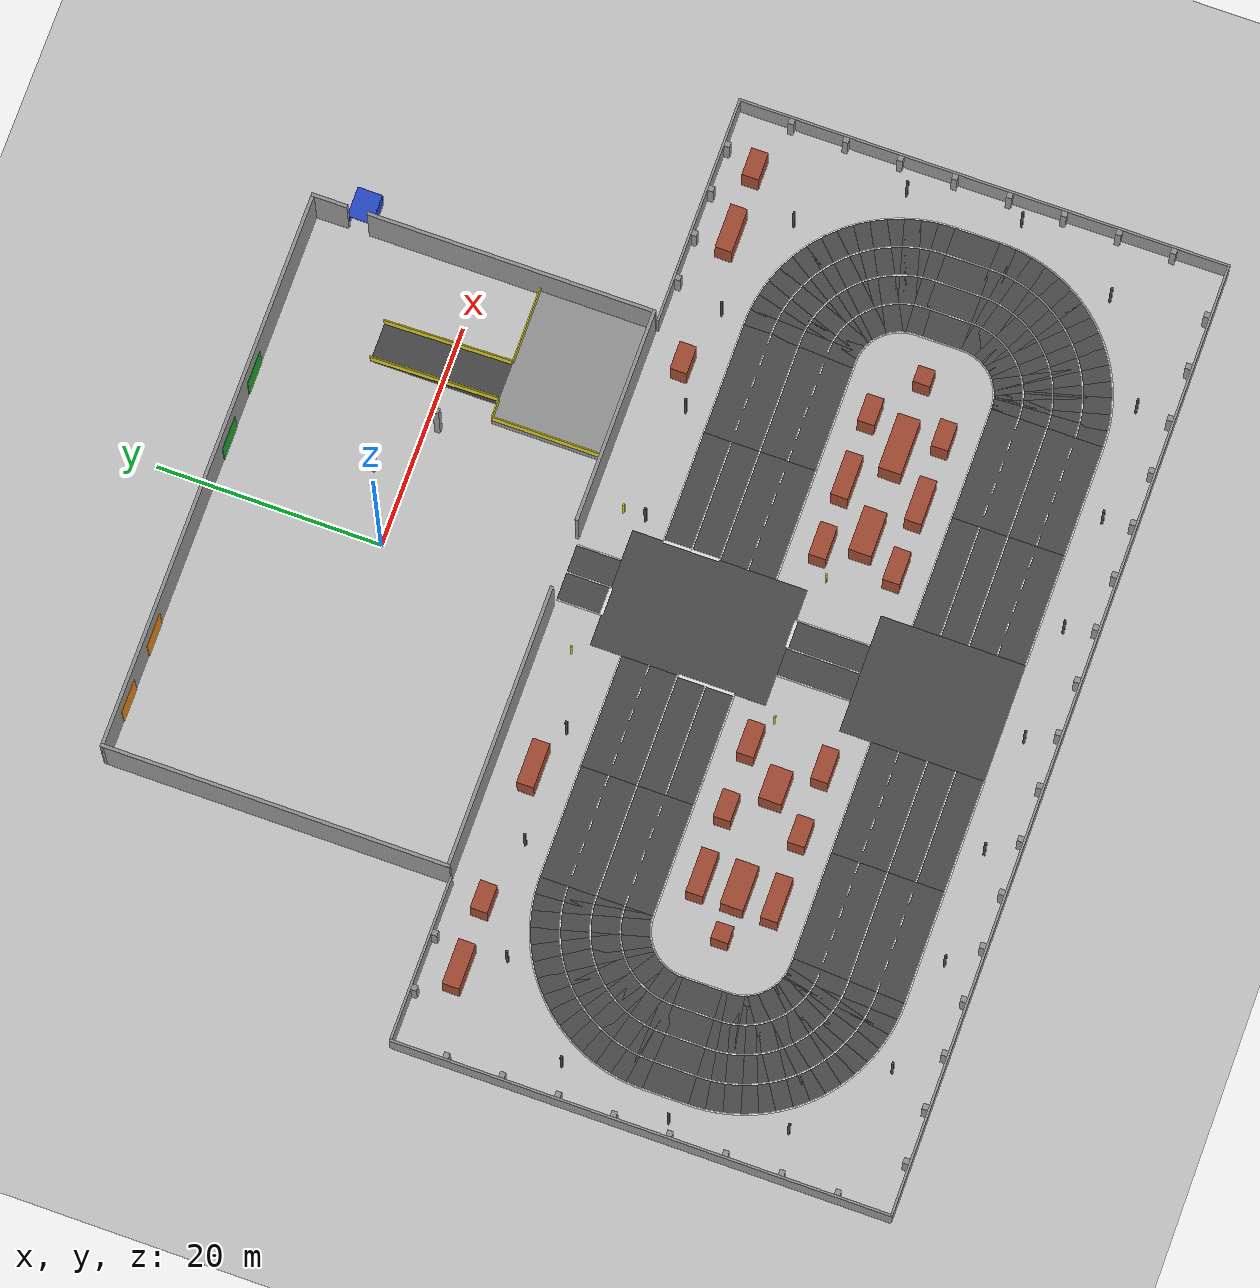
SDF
<sdf version="1.6">
 <world name="default">
  <include><uri>model://ground_plane</uri></include>
  <include><uri>model://sun</uri></include>
  <scene><ambient>0.6 0.6 0.6 1</ambient><shadows>false</shadows></scene>
  <physics type="ode">
   <real_time_update_rate>1000.0</real_time_update_rate>
   <max_step_size>0.001</max_step_size>
   <real_time_factor>1</real_time_factor>
  </physics>
  <model name="mezz_platform">
   <static>true</static>
   <pose>19.0000 -10.0000 0.5000 0.000000 0.000000 0.000000</pose>
   <link name="link">
    <collision name="c"><geometry><box><size>12.0000 10.0000 1.0000</size></box></geometry></collision>
    <visual name="v">
     <geometry><box><size>12.0000 10.0000 1.0000</size></box></geometry>
     <material>
      <script><uri>file://media/materials/scripts/gazebo.material</uri><name>Gazebo/Grey</name></script>
     </material>
    </visual>
   </link>
  </model>
  <model name="mezz_ramp">
   <static>true</static>
   <pose>16.5000 0.6584 -0.1475 -0.087266 0.000000 0.000000</pose>
   <link name="link">
    <collision name="c"><geometry><box><size>3.5000 11.4737 1.3000</size></box></geometry></collision>
    <visual name="v">
     <geometry><box><size>3.5000 11.4737 1.3000</size></box></geometry>
     <material>
      <script><uri>file://media/materials/scripts/gazebo.material</uri><name>Gazebo/DarkGrey</name></script>
     </material>
    </visual>
   </link>
  </model>
  <model name="mezz_ramp_rail_w">
   <static>true</static>
   <pose>14.8000 0.7630 1.0479 -0.087266 0.000000 0.000000</pose>
   <link name="link">
    <collision name="c"><geometry><box><size>0.1000 11.4737 1.1000</size></box></geometry></collision>
    <visual name="v">
     <geometry><box><size>0.1000 11.4737 1.1000</size></box></geometry>
     <material>
      <script><uri>file://media/materials/scripts/gazebo.material</uri><name>Gazebo/Yellow</name></script>
     </material>
    </visual>
   </link>
  </model>
  <model name="mezz_ramp_rail_e">
   <static>true</static>
   <pose>18.2000 0.7630 1.0479 -0.087266 0.000000 0.000000</pose>
   <link name="link">
    <collision name="c"><geometry><box><size>0.1000 11.4737 1.1000</size></box></geometry></collision>
    <visual name="v">
     <geometry><box><size>0.1000 11.4737 1.1000</size></box></geometry>
     <material>
      <script><uri>file://media/materials/scripts/gazebo.material</uri><name>Gazebo/Yellow</name></script>
     </material>
    </visual>
   </link>
  </model>
  <model name="mezz_guard_west">
   <static>true</static>
   <pose>13.0500 -10.0000 1.5500 0.000000 0.000000 0.000000</pose>
   <link name="link">
    <collision name="c"><geometry><box><size>0.1000 10.0000 1.1000</size></box></geometry></collision>
    <visual name="v">
     <geometry><box><size>0.1000 10.0000 1.1000</size></box></geometry>
     <material>
      <script><uri>file://media/materials/scripts/gazebo.material</uri><name>Gazebo/Yellow</name></script>
     </material>
    </visual>
   </link>
  </model>
  <model name="mezz_guard_north_0">
   <static>true</static>
   <pose>13.8750 -5.0500 1.5500 0.000000 0.000000 0.000000</pose>
   <link name="link">
    <collision name="c"><geometry><box><size>1.7500 0.1000 1.1000</size></box></geometry></collision>
    <visual name="v">
     <geometry><box><size>1.7500 0.1000 1.1000</size></box></geometry>
     <material>
      <script><uri>file://media/materials/scripts/gazebo.material</uri><name>Gazebo/Yellow</name></script>
     </material>
    </visual>
   </link>
  </model>
  <model name="mezz_guard_north_1">
   <static>true</static>
   <pose>21.6250 -5.0500 1.5500 0.000000 0.000000 0.000000</pose>
   <link name="link">
    <collision name="c"><geometry><box><size>6.7500 0.1000 1.1000</size></box></geometry></collision>
    <visual name="v">
     <geometry><box><size>6.7500 0.1000 1.1000</size></box></geometry>
     <material>
      <script><uri>file://media/materials/scripts/gazebo.material</uri><name>Gazebo/Yellow</name></script>
     </material>
    </visual>
   </link>
  </model>
  <model name="wall_n">
   <static>true</static>
   <pose>0.0000 15.1500 3.0000 0.000000 0.000000 0.000000</pose>
   <link name="link">
    <collision name="c"><geometry><box><size>50.6000 0.3000 6.0000</size></box></geometry></collision>
    <visual name="v">
     <geometry><box><size>50.6000 0.3000 6.0000</size></box></geometry>
     <material>
      <script><uri>file://media/materials/scripts/gazebo.material</uri><name>Gazebo/Grey</name></script>
     </material>
    </visual>
   </link>
  </model>
  <model name="wall_w">
   <static>true</static>
   <pose>-25.1500 0.0000 3.0000 0.000000 0.000000 0.000000</pose>
   <link name="link">
    <collision name="c"><geometry><box><size>0.3000 30.6000 6.0000</size></box></geometry></collision>
    <visual name="v">
     <geometry><box><size>0.3000 30.6000 6.0000</size></box></geometry>
     <material>
      <script><uri>file://media/materials/scripts/gazebo.material</uri><name>Gazebo/Grey</name></script>
     </material>
    </visual>
   </link>
  </model>
  <model name="wall_s_0">
   <static>true</static>
   <pose>-12.6500 -15.1500 3.0000 0.000000 0.000000 0.000000</pose>
   <link name="link">
    <collision name="c"><geometry><box><size>25.3000 0.3000 6.0000</size></box></geometry></collision>
    <visual name="v">
     <geometry><box><size>25.3000 0.3000 6.0000</size></box></geometry>
     <material>
      <script><uri>file://media/materials/scripts/gazebo.material</uri><name>Gazebo/Grey</name></script>
     </material>
    </visual>
   </link>
  </model>
  <model name="wall_s_1">
   <static>true</static>
   <pose>15.6500 -15.1500 3.0000 0.000000 0.000000 0.000000</pose>
   <link name="link">
    <collision name="c"><geometry><box><size>19.3000 0.3000 6.0000</size></box></geometry></collision>
    <visual name="v">
     <geometry><box><size>19.3000 0.3000 6.0000</size></box></geometry>
     <material>
      <script><uri>file://media/materials/scripts/gazebo.material</uri><name>Gazebo/Grey</name></script>
     </material>
    </visual>
   </link>
  </model>
  <model name="wall_e_0">
   <static>true</static>
   <pose>25.1500 -2.5000 3.0000 0.000000 0.000000 0.000000</pose>
   <link name="link">
    <collision name="c"><geometry><box><size>0.3000 25.6000 6.0000</size></box></geometry></collision>
    <visual name="v">
     <geometry><box><size>0.3000 25.6000 6.0000</size></box></geometry>
     <material>
      <script><uri>file://media/materials/scripts/gazebo.material</uri><name>Gazebo/Grey</name></script>
     </material>
    </visual>
   </link>
  </model>
  <model name="wall_e_1">
   <static>true</static>
   <pose>25.1500 13.7000 3.0000 0.000000 0.000000 0.000000</pose>
   <link name="link">
    <collision name="c"><geometry><box><size>0.3000 3.2000 6.0000</size></box></geometry></collision>
    <visual name="v">
     <geometry><box><size>0.3000 3.2000 6.0000</size></box></geometry>
     <material>
      <script><uri>file://media/materials/scripts/gazebo.material</uri><name>Gazebo/Grey</name></script>
     </material>
    </visual>
   </link>
  </model>
  <model name="door_R1">
   <static>true</static>
   <pose>-20.0000 14.9700 1.7500 0.000000 0.000000 0.000000</pose>
   <link name="link">
    <visual name="v">
     <geometry><box><size>3.0000 0.0500 3.5000</size></box></geometry>
     <material>
      <script><uri>file://media/materials/scripts/gazebo.material</uri><name>Gazebo/Orange</name></script>
     </material>
    </visual>
   </link>
  </model>
  <model name="door_R2">
   <static>true</static>
   <pose>-14.0000 14.9700 1.7500 0.000000 0.000000 0.000000</pose>
   <link name="link">
    <visual name="v">
     <geometry><box><size>3.0000 0.0500 3.5000</size></box></geometry>
     <material>
      <script><uri>file://media/materials/scripts/gazebo.material</uri><name>Gazebo/Orange</name></script>
     </material>
    </visual>
   </link>
  </model>
  <model name="door_S1">
   <static>true</static>
   <pose>4.0000 14.9700 1.7500 0.000000 0.000000 0.000000</pose>
   <link name="link">
    <visual name="v">
     <geometry><box><size>3.0000 0.0500 3.5000</size></box></geometry>
     <material>
      <script><uri>file://media/materials/scripts/gazebo.material</uri><name>Gazebo/Green</name></script>
     </material>
    </visual>
   </link>
  </model>
  <model name="door_S2">
   <static>true</static>
   <pose>10.0000 14.9700 1.7500 0.000000 0.000000 0.000000</pose>
   <link name="link">
    <visual name="v">
     <geometry><box><size>3.0000 0.0500 3.5000</size></box></geometry>
     <material>
      <script><uri>file://media/materials/scripts/gazebo.material</uri><name>Gazebo/Green</name></script>
     </material>
    </visual>
   </link>
  </model>
  <model name="elevator_back">
   <static>true</static>
   <pose>27.9500 11.2000 1.2500 0.000000 0.000000 0.000000</pose>
   <link name="link">
    <collision name="c"><geometry><box><size>0.1000 2.2000 2.5000</size></box></geometry></collision>
    <visual name="v">
     <geometry><box><size>0.1000 2.2000 2.5000</size></box></geometry>
     <material>
      <script><uri>file://media/materials/scripts/gazebo.material</uri><name>Gazebo/Blue</name></script>
     </material>
    </visual>
   </link>
  </model>
  <model name="elevator_side_n">
   <static>true</static>
   <pose>26.6500 12.2500 1.2500 0.000000 0.000000 0.000000</pose>
   <link name="link">
    <collision name="c"><geometry><box><size>2.7000 0.1000 2.5000</size></box></geometry></collision>
    <visual name="v">
     <geometry><box><size>2.7000 0.1000 2.5000</size></box></geometry>
     <material>
      <script><uri>file://media/materials/scripts/gazebo.material</uri><name>Gazebo/Blue</name></script>
     </material>
    </visual>
   </link>
  </model>
  <model name="elevator_side_s">
   <static>true</static>
   <pose>26.6500 10.1500 1.2500 0.000000 0.000000 0.000000</pose>
   <link name="link">
    <collision name="c"><geometry><box><size>2.7000 0.1000 2.5000</size></box></geometry></collision>
    <visual name="v">
     <geometry><box><size>2.7000 0.1000 2.5000</size></box></geometry>
     <material>
      <script><uri>file://media/materials/scripts/gazebo.material</uri><name>Gazebo/Blue</name></script>
     </material>
    </visual>
   </link>
  </model>
  <model name="elevator_roof">
   <static>true</static>
   <pose>26.6500 11.2000 2.5500 0.000000 0.000000 0.000000</pose>
   <link name="link">
    <collision name="c"><geometry><box><size>2.7000 2.2000 0.1000</size></box></geometry></collision>
    <visual name="v">
     <geometry><box><size>2.7000 2.2000 0.1000</size></box></geometry>
     <material>
      <script><uri>file://media/materials/scripts/gazebo.material</uri><name>Gazebo/Blue</name></script>
     </material>
    </visual>
   </link>
  </model>
  <model name="road_surface">
   <static>true</static>
   <link name="link">
    <visual name="v0">
     <pose>-17.2500 -27.0000 0.0010 0 0 0.000000</pose>
     <geometry><box><size>10.0000 10.0000 0.0020</size></box></geometry>
     <material>
      <script><uri>file://media/materials/scripts/gazebo.material</uri><name>Gazebo/DarkGrey</name></script>
     </material>
    </visual>
    <visual name="v1">
     <pose>-7.2500 -27.0000 0.0010 0 0 0.000000</pose>
     <geometry><box><size>10.0000 10.0000 0.0020</size></box></geometry>
     <material>
      <script><uri>file://media/materials/scripts/gazebo.material</uri><name>Gazebo/DarkGrey</name></script>
     </material>
    </visual>
    <visual name="v2">
     <pose>13.2500 -27.0000 0.0010 0 0 0.000000</pose>
     <geometry><box><size>10.0000 10.0000 0.0020</size></box></geometry>
     <material>
      <script><uri>file://media/materials/scripts/gazebo.material</uri><name>Gazebo/DarkGrey</name></script>
     </material>
    </visual>
    <visual name="v3">
     <pose>23.2500 -27.0000 0.0010 0 0 0.000000</pose>
     <geometry><box><size>10.0000 10.0000 0.0020</size></box></geometry>
     <material>
      <script><uri>file://media/materials/scripts/gazebo.material</uri><name>Gazebo/DarkGrey</name></script>
     </material>
    </visual>
    <visual name="v4">
     <pose>28.7210 -27.0123 0.0010 0 0 -0.052360</pose>
     <geometry><box><size>1.4674 10.0000 0.0020</size></box></geometry>
     <material>
      <script><uri>file://media/materials/scripts/gazebo.material</uri><name>Gazebo/DarkGrey</name></script>
     </material>
    </visual>
    <visual name="v5">
     <pose>29.6579 -27.1108 0.0010 0 0 -0.157080</pose>
     <geometry><box><size>1.4674 10.0000 0.0020</size></box></geometry>
     <material>
      <script><uri>file://media/materials/scripts/gazebo.material</uri><name>Gazebo/DarkGrey</name></script>
     </material>
    </visual>
    <visual name="v6">
     <pose>30.5794 -27.3067 0.0010 0 0 -0.261799</pose>
     <geometry><box><size>1.4674 10.0000 0.0020</size></box></geometry>
     <material>
      <script><uri>file://media/materials/scripts/gazebo.material</uri><name>Gazebo/DarkGrey</name></script>
     </material>
    </visual>
    <visual name="v7">
     <pose>31.4753 -27.5978 0.0010 0 0 -0.366519</pose>
     <geometry><box><size>1.4674 10.0000 0.0020</size></box></geometry>
     <material>
      <script><uri>file://media/materials/scripts/gazebo.material</uri><name>Gazebo/DarkGrey</name></script>
     </material>
    </visual>
    <visual name="v8">
     <pose>32.3359 -27.9809 0.0010 0 0 -0.471239</pose>
     <geometry><box><size>1.4674 10.0000 0.0020</size></box></geometry>
     <material>
      <script><uri>file://media/materials/scripts/gazebo.material</uri><name>Gazebo/DarkGrey</name></script>
     </material>
    </visual>
    <visual name="v9">
     <pose>33.1518 -28.4520 0.0010 0 0 -0.575959</pose>
     <geometry><box><size>1.4674 10.0000 0.0020</size></box></geometry>
     <material>
      <script><uri>file://media/materials/scripts/gazebo.material</uri><name>Gazebo/DarkGrey</name></script>
     </material>
    </visual>
    <visual name="v10">
     <pose>33.9139 -29.0057 0.0010 0 0 -0.680678</pose>
     <geometry><box><size>1.4674 10.0000 0.0020</size></box></geometry>
     <material>
      <script><uri>file://media/materials/scripts/gazebo.material</uri><name>Gazebo/DarkGrey</name></script>
     </material>
    </visual>
    <visual name="v11">
     <pose>34.6140 -29.6360 0.0010 0 0 -0.785398</pose>
     <geometry><box><size>1.4674 10.0000 0.0020</size></box></geometry>
     <material>
      <script><uri>file://media/materials/scripts/gazebo.material</uri><name>Gazebo/DarkGrey</name></script>
     </material>
    </visual>
    <visual name="v12">
     <pose>35.2443 -30.3361 0.0010 0 0 -0.890118</pose>
     <geometry><box><size>1.4674 10.0000 0.0020</size></box></geometry>
     <material>
      <script><uri>file://media/materials/scripts/gazebo.material</uri><name>Gazebo/DarkGrey</name></script>
     </material>
    </visual>
    <visual name="v13">
     <pose>35.7980 -31.0982 0.0010 0 0 -0.994838</pose>
     <geometry><box><size>1.4674 10.0000 0.0020</size></box></geometry>
     <material>
      <script><uri>file://media/materials/scripts/gazebo.material</uri><name>Gazebo/DarkGrey</name></script>
     </material>
    </visual>
    <visual name="v14">
     <pose>36.2691 -31.9141 0.0010 0 0 -1.099557</pose>
     <geometry><box><size>1.4674 10.0000 0.0020</size></box></geometry>
     <material>
      <script><uri>file://media/materials/scripts/gazebo.material</uri><name>Gazebo/DarkGrey</name></script>
     </material>
    </visual>
    <visual name="v15">
     <pose>36.6522 -32.7747 0.0010 0 0 -1.204277</pose>
     <geometry><box><size>1.4674 10.0000 0.0020</size></box></geometry>
     <material>
      <script><uri>file://media/materials/scripts/gazebo.material</uri><name>Gazebo/DarkGrey</name></script>
     </material>
    </visual>
    <visual name="v16">
     <pose>36.9433 -33.6706 0.0010 0 0 -1.308997</pose>
     <geometry><box><size>1.4674 10.0000 0.0020</size></box></geometry>
     <material>
      <script><uri>file://media/materials/scripts/gazebo.material</uri><name>Gazebo/DarkGrey</name></script>
     </material>
    </visual>
    <visual name="v17">
     <pose>37.1392 -34.5921 0.0010 0 0 -1.413717</pose>
     <geometry><box><size>1.4674 10.0000 0.0020</size></box></geometry>
     <material>
      <script><uri>file://media/materials/scripts/gazebo.material</uri><name>Gazebo/DarkGrey</name></script>
     </material>
    </visual>
    <visual name="v18">
     <pose>37.2377 -35.5290 0.0010 0 0 -1.518436</pose>
     <geometry><box><size>1.4674 10.0000 0.0020</size></box></geometry>
     <material>
      <script><uri>file://media/materials/scripts/gazebo.material</uri><name>Gazebo/DarkGrey</name></script>
     </material>
    </visual>
    <visual name="v19">
     <pose>37.2500 -38.0000 0.0010 0 0 -1.570796</pose>
     <geometry><box><size>4.0000 10.0000 0.0020</size></box></geometry>
     <material>
      <script><uri>file://media/materials/scripts/gazebo.material</uri><name>Gazebo/DarkGrey</name></script>
     </material>
    </visual>
    <visual name="v20">
     <pose>37.2377 -40.4710 0.0010 0 0 -1.623156</pose>
     <geometry><box><size>1.4674 10.0000 0.0020</size></box></geometry>
     <material>
      <script><uri>file://media/materials/scripts/gazebo.material</uri><name>Gazebo/DarkGrey</name></script>
     </material>
    </visual>
    <visual name="v21">
     <pose>37.1392 -41.4079 0.0010 0 0 -1.727876</pose>
     <geometry><box><size>1.4674 10.0000 0.0020</size></box></geometry>
     <material>
      <script><uri>file://media/materials/scripts/gazebo.material</uri><name>Gazebo/DarkGrey</name></script>
     </material>
    </visual>
    <visual name="v22">
     <pose>36.9433 -42.3294 0.0010 0 0 -1.832596</pose>
     <geometry><box><size>1.4674 10.0000 0.0020</size></box></geometry>
     <material>
      <script><uri>file://media/materials/scripts/gazebo.material</uri><name>Gazebo/DarkGrey</name></script>
     </material>
    </visual>
    <visual name="v23">
     <pose>36.6522 -43.2253 0.0010 0 0 -1.937315</pose>
     <geometry><box><size>1.4674 10.0000 0.0020</size></box></geometry>
     <material>
      <script><uri>file://media/materials/scripts/gazebo.material</uri><name>Gazebo/DarkGrey</name></script>
     </material>
    </visual>
    <visual name="v24">
     <pose>36.2691 -44.0859 0.0010 0 0 -2.042035</pose>
     <geometry><box><size>1.4674 10.0000 0.0020</size></box></geometry>
     <material>
      <script><uri>file://media/materials/scripts/gazebo.material</uri><name>Gazebo/DarkGrey</name></script>
     </material>
    </visual>
    <visual name="v25">
     <pose>35.7980 -44.9018 0.0010 0 0 -2.146755</pose>
     <geometry><box><size>1.4674 10.0000 0.0020</size></box></geometry>
     <material>
      <script><uri>file://media/materials/scripts/gazebo.material</uri><name>Gazebo/DarkGrey</name></script>
     </material>
    </visual>
    <visual name="v26">
     <pose>35.2443 -45.6639 0.0010 0 0 -2.251475</pose>
     <geometry><box><size>1.4674 10.0000 0.0020</size></box></geometry>
     <material>
      <script><uri>file://media/materials/scripts/gazebo.material</uri><name>Gazebo/DarkGrey</name></script>
     </material>
    </visual>
    <visual name="v27">
     <pose>34.6140 -46.3640 0.0010 0 0 -2.356194</pose>
     <geometry><box><size>1.4674 10.0000 0.0020</size></box></geometry>
     <material>
      <script><uri>file://media/materials/scripts/gazebo.material</uri><name>Gazebo/DarkGrey</name></script>
     </material>
    </visual>
    <visual name="v28">
     <pose>33.9139 -46.9943 0.0010 0 0 -2.460914</pose>
     <geometry><box><size>1.4674 10.0000 0.0020</size></box></geometry>
     <material>
      <script><uri>file://media/materials/scripts/gazebo.material</uri><name>Gazebo/DarkGrey</name></script>
     </material>
    </visual>
    <visual name="v29">
     <pose>33.1518 -47.5480 0.0010 0 0 -2.565634</pose>
     <geometry><box><size>1.4674 10.0000 0.0020</size></box></geometry>
     <material>
      <script><uri>file://media/materials/scripts/gazebo.material</uri><name>Gazebo/DarkGrey</name></script>
     </material>
    </visual>
    <visual name="v30">
     <pose>32.3359 -48.0191 0.0010 0 0 -2.670354</pose>
     <geometry><box><size>1.4674 10.0000 0.0020</size></box></geometry>
     <material>
      <script><uri>file://media/materials/scripts/gazebo.material</uri><name>Gazebo/DarkGrey</name></script>
     </material>
    </visual>
    <visual name="v31">
     <pose>31.4753 -48.4022 0.0010 0 0 -2.775074</pose>
     <geometry><box><size>1.4674 10.0000 0.0020</size></box></geometry>
     <material>
      <script><uri>file://media/materials/scripts/gazebo.material</uri><name>Gazebo/DarkGrey</name></script>
     </material>
    </visual>
    <visual name="v32">
     <pose>30.5794 -48.6933 0.0010 0 0 -2.879793</pose>
     <geometry><box><size>1.4674 10.0000 0.0020</size></box></geometry>
     <material>
      <script><uri>file://media/materials/scripts/gazebo.material</uri><name>Gazebo/DarkGrey</name></script>
     </material>
    </visual>
    <visual name="v33">
     <pose>29.6579 -48.8892 0.0010 0 0 -2.984513</pose>
     <geometry><box><size>1.4674 10.0000 0.0020</size></box></geometry>
     <material>
      <script><uri>file://media/materials/scripts/gazebo.material</uri><name>Gazebo/DarkGrey</name></script>
     </material>
    </visual>
    <visual name="v34">
     <pose>28.7210 -48.9877 0.0010 0 0 -3.089233</pose>
     <geometry><box><size>1.4674 10.0000 0.0020</size></box></geometry>
     <material>
      <script><uri>file://media/materials/scripts/gazebo.material</uri><name>Gazebo/DarkGrey</name></script>
     </material>
    </visual>
    <visual name="v35">
     <pose>23.2500 -49.0000 0.0010 0 0 3.141593</pose>
     <geometry><box><size>10.0000 10.0000 0.0020</size></box></geometry>
     <material>
      <script><uri>file://media/materials/scripts/gazebo.material</uri><name>Gazebo/DarkGrey</name></script>
     </material>
    </visual>
    <visual name="v36">
     <pose>13.2500 -49.0000 0.0010 0 0 3.141593</pose>
     <geometry><box><size>10.0000 10.0000 0.0020</size></box></geometry>
     <material>
      <script><uri>file://media/materials/scripts/gazebo.material</uri><name>Gazebo/DarkGrey</name></script>
     </material>
    </visual>
    <visual name="v37">
     <pose>-7.2500 -49.0000 0.0010 0 0 3.141593</pose>
     <geometry><box><size>10.0000 10.0000 0.0020</size></box></geometry>
     <material>
      <script><uri>file://media/materials/scripts/gazebo.material</uri><name>Gazebo/DarkGrey</name></script>
     </material>
    </visual>
    <visual name="v38">
     <pose>-17.2500 -49.0000 0.0010 0 0 3.141593</pose>
     <geometry><box><size>10.0000 10.0000 0.0020</size></box></geometry>
     <material>
      <script><uri>file://media/materials/scripts/gazebo.material</uri><name>Gazebo/DarkGrey</name></script>
     </material>
    </visual>
    <visual name="v39">
     <pose>-22.7210 -48.9877 0.0010 0 0 -3.193953</pose>
     <geometry><box><size>1.4674 10.0000 0.0020</size></box></geometry>
     <material>
      <script><uri>file://media/materials/scripts/gazebo.material</uri><name>Gazebo/DarkGrey</name></script>
     </material>
    </visual>
    <visual name="v40">
     <pose>-23.6579 -48.8892 0.0010 0 0 -3.298672</pose>
     <geometry><box><size>1.4674 10.0000 0.0020</size></box></geometry>
     <material>
      <script><uri>file://media/materials/scripts/gazebo.material</uri><name>Gazebo/DarkGrey</name></script>
     </material>
    </visual>
    <visual name="v41">
     <pose>-24.5794 -48.6933 0.0010 0 0 -3.403392</pose>
     <geometry><box><size>1.4674 10.0000 0.0020</size></box></geometry>
     <material>
      <script><uri>file://media/materials/scripts/gazebo.material</uri><name>Gazebo/DarkGrey</name></script>
     </material>
    </visual>
    <visual name="v42">
     <pose>-25.4753 -48.4022 0.0010 0 0 -3.508112</pose>
     <geometry><box><size>1.4674 10.0000 0.0020</size></box></geometry>
     <material>
      <script><uri>file://media/materials/scripts/gazebo.material</uri><name>Gazebo/DarkGrey</name></script>
     </material>
    </visual>
    <visual name="v43">
     <pose>-26.3359 -48.0191 0.0010 0 0 -3.612832</pose>
     <geometry><box><size>1.4674 10.0000 0.0020</size></box></geometry>
     <material>
      <script><uri>file://media/materials/scripts/gazebo.material</uri><name>Gazebo/DarkGrey</name></script>
     </material>
    </visual>
    <visual name="v44">
     <pose>-27.1518 -47.5480 0.0010 0 0 -3.717551</pose>
     <geometry><box><size>1.4674 10.0000 0.0020</size></box></geometry>
     <material>
      <script><uri>file://media/materials/scripts/gazebo.material</uri><name>Gazebo/DarkGrey</name></script>
     </material>
    </visual>
    <visual name="v45">
     <pose>-27.9139 -46.9943 0.0010 0 0 -3.822271</pose>
     <geometry><box><size>1.4674 10.0000 0.0020</size></box></geometry>
     <material>
      <script><uri>file://media/materials/scripts/gazebo.material</uri><name>Gazebo/DarkGrey</name></script>
     </material>
    </visual>
    <visual name="v46">
     <pose>-28.6140 -46.3640 0.0010 0 0 -3.926991</pose>
     <geometry><box><size>1.4674 10.0000 0.0020</size></box></geometry>
     <material>
      <script><uri>file://media/materials/scripts/gazebo.material</uri><name>Gazebo/DarkGrey</name></script>
     </material>
    </visual>
    <visual name="v47">
     <pose>-29.2443 -45.6639 0.0010 0 0 -4.031711</pose>
     <geometry><box><size>1.4674 10.0000 0.0020</size></box></geometry>
     <material>
      <script><uri>file://media/materials/scripts/gazebo.material</uri><name>Gazebo/DarkGrey</name></script>
     </material>
    </visual>
    <visual name="v48">
     <pose>-29.7980 -44.9018 0.0010 0 0 -4.136430</pose>
     <geometry><box><size>1.4674 10.0000 0.0020</size></box></geometry>
     <material>
      <script><uri>file://media/materials/scripts/gazebo.material</uri><name>Gazebo/DarkGrey</name></script>
     </material>
    </visual>
    <visual name="v49">
     <pose>-30.2691 -44.0859 0.0010 0 0 -4.241150</pose>
     <geometry><box><size>1.4674 10.0000 0.0020</size></box></geometry>
     <material>
      <script><uri>file://media/materials/scripts/gazebo.material</uri><name>Gazebo/DarkGrey</name></script>
     </material>
    </visual>
    <visual name="v50">
     <pose>-30.6522 -43.2253 0.0010 0 0 -4.345870</pose>
     <geometry><box><size>1.4674 10.0000 0.0020</size></box></geometry>
     <material>
      <script><uri>file://media/materials/scripts/gazebo.material</uri><name>Gazebo/DarkGrey</name></script>
     </material>
    </visual>
    <visual name="v51">
     <pose>-30.9433 -42.3294 0.0010 0 0 -4.450590</pose>
     <geometry><box><size>1.4674 10.0000 0.0020</size></box></geometry>
     <material>
      <script><uri>file://media/materials/scripts/gazebo.material</uri><name>Gazebo/DarkGrey</name></script>
     </material>
    </visual>
    <visual name="v52">
     <pose>-31.1392 -41.4079 0.0010 0 0 -4.555309</pose>
     <geometry><box><size>1.4674 10.0000 0.0020</size></box></geometry>
     <material>
      <script><uri>file://media/materials/scripts/gazebo.material</uri><name>Gazebo/DarkGrey</name></script>
     </material>
    </visual>
    <visual name="v53">
     <pose>-31.2377 -40.4710 0.0010 0 0 -4.660029</pose>
     <geometry><box><size>1.4674 10.0000 0.0020</size></box></geometry>
     <material>
      <script><uri>file://media/materials/scripts/gazebo.material</uri><name>Gazebo/DarkGrey</name></script>
     </material>
    </visual>
    <visual name="v54">
     <pose>-31.2500 -38.0000 0.0010 0 0 1.570796</pose>
     <geometry><box><size>4.0000 10.0000 0.0020</size></box></geometry>
     <material>
      <script><uri>file://media/materials/scripts/gazebo.material</uri><name>Gazebo/DarkGrey</name></script>
     </material>
    </visual>
    <visual name="v55">
     <pose>-31.2377 -35.5290 0.0010 0 0 1.518436</pose>
     <geometry><box><size>1.4674 10.0000 0.0020</size></box></geometry>
     <material>
      <script><uri>file://media/materials/scripts/gazebo.material</uri><name>Gazebo/DarkGrey</name></script>
     </material>
    </visual>
    <visual name="v56">
     <pose>-31.1392 -34.5921 0.0010 0 0 1.413717</pose>
     <geometry><box><size>1.4674 10.0000 0.0020</size></box></geometry>
     <material>
      <script><uri>file://media/materials/scripts/gazebo.material</uri><name>Gazebo/DarkGrey</name></script>
     </material>
    </visual>
    <visual name="v57">
     <pose>-30.9433 -33.6706 0.0010 0 0 1.308997</pose>
     <geometry><box><size>1.4674 10.0000 0.0020</size></box></geometry>
     <material>
      <script><uri>file://media/materials/scripts/gazebo.material</uri><name>Gazebo/DarkGrey</name></script>
     </material>
    </visual>
    <visual name="v58">
     <pose>-30.6522 -32.7747 0.0010 0 0 1.204277</pose>
     <geometry><box><size>1.4674 10.0000 0.0020</size></box></geometry>
     <material>
      <script><uri>file://media/materials/scripts/gazebo.material</uri><name>Gazebo/DarkGrey</name></script>
     </material>
    </visual>
    <visual name="v59">
     <pose>-30.2691 -31.9141 0.0010 0 0 1.099557</pose>
     <geometry><box><size>1.4674 10.0000 0.0020</size></box></geometry>
     <material>
      <script><uri>file://media/materials/scripts/gazebo.material</uri><name>Gazebo/DarkGrey</name></script>
     </material>
    </visual>
    <visual name="v60">
     <pose>-29.7980 -31.0982 0.0010 0 0 0.994838</pose>
     <geometry><box><size>1.4674 10.0000 0.0020</size></box></geometry>
     <material>
      <script><uri>file://media/materials/scripts/gazebo.material</uri><name>Gazebo/DarkGrey</name></script>
     </material>
    </visual>
    <visual name="v61">
     <pose>-29.2443 -30.3361 0.0010 0 0 0.890118</pose>
     <geometry><box><size>1.4674 10.0000 0.0020</size></box></geometry>
     <material>
      <script><uri>file://media/materials/scripts/gazebo.material</uri><name>Gazebo/DarkGrey</name></script>
     </material>
    </visual>
    <visual name="v62">
     <pose>-28.6140 -29.6360 0.0010 0 0 0.785398</pose>
     <geometry><box><size>1.4674 10.0000 0.0020</size></box></geometry>
     <material>
      <script><uri>file://media/materials/scripts/gazebo.material</uri><name>Gazebo/DarkGrey</name></script>
     </material>
    </visual>
    <visual name="v63">
     <pose>-27.9139 -29.0057 0.0010 0 0 0.680678</pose>
     <geometry><box><size>1.4674 10.0000 0.0020</size></box></geometry>
     <material>
      <script><uri>file://media/materials/scripts/gazebo.material</uri><name>Gazebo/DarkGrey</name></script>
     </material>
    </visual>
    <visual name="v64">
     <pose>-27.1518 -28.4520 0.0010 0 0 0.575959</pose>
     <geometry><box><size>1.4674 10.0000 0.0020</size></box></geometry>
     <material>
      <script><uri>file://media/materials/scripts/gazebo.material</uri><name>Gazebo/DarkGrey</name></script>
     </material>
    </visual>
    <visual name="v65">
     <pose>-26.3359 -27.9809 0.0010 0 0 0.471239</pose>
     <geometry><box><size>1.4674 10.0000 0.0020</size></box></geometry>
     <material>
      <script><uri>file://media/materials/scripts/gazebo.material</uri><name>Gazebo/DarkGrey</name></script>
     </material>
    </visual>
    <visual name="v66">
     <pose>-25.4753 -27.5978 0.0010 0 0 0.366519</pose>
     <geometry><box><size>1.4674 10.0000 0.0020</size></box></geometry>
     <material>
      <script><uri>file://media/materials/scripts/gazebo.material</uri><name>Gazebo/DarkGrey</name></script>
     </material>
    </visual>
    <visual name="v67">
     <pose>-24.5794 -27.3067 0.0010 0 0 0.261799</pose>
     <geometry><box><size>1.4674 10.0000 0.0020</size></box></geometry>
     <material>
      <script><uri>file://media/materials/scripts/gazebo.material</uri><name>Gazebo/DarkGrey</name></script>
     </material>
    </visual>
    <visual name="v68">
     <pose>-23.6579 -27.1108 0.0010 0 0 0.157080</pose>
     <geometry><box><size>1.4674 10.0000 0.0020</size></box></geometry>
     <material>
      <script><uri>file://media/materials/scripts/gazebo.material</uri><name>Gazebo/DarkGrey</name></script>
     </material>
    </visual>
    <visual name="v69">
     <pose>-22.7210 -27.0123 0.0010 0 0 0.052360</pose>
     <geometry><box><size>1.4674 10.0000 0.0020</size></box></geometry>
     <material>
      <script><uri>file://media/materials/scripts/gazebo.material</uri><name>Gazebo/DarkGrey</name></script>
     </material>
    </visual>
    <visual name="v70">
     <pose>3.0000 -17.2750 0.0010 0 0 -1.570796</pose>
     <geometry><box><size>3.9500 5.0000 0.0020</size></box></geometry>
     <material>
      <script><uri>file://media/materials/scripts/gazebo.material</uri><name>Gazebo/DarkGrey</name></script>
     </material>
    </visual>
    <visual name="v71">
     <pose>3.0000 -38.0000 0.0010 0 0 -1.570796</pose>
     <geometry><box><size>6.5000 5.0000 0.0020</size></box></geometry>
     <material>
      <script><uri>file://media/materials/scripts/gazebo.material</uri><name>Gazebo/DarkGrey</name></script>
     </material>
    </visual>
    <visual name="v72">
     <pose>3.0000 -27.0000 0.0010 0 0 0.000000</pose>
     <geometry><box><size>10.5000 15.5000 0.0020</size></box></geometry>
     <material>
      <script><uri>file://media/materials/scripts/gazebo.material</uri><name>Gazebo/DarkGrey</name></script>
     </material>
    </visual>
    <visual name="v73">
     <pose>3.0000 -47.6250 0.0010 0 0 0.000000</pose>
     <geometry><box><size>10.5000 12.7500 0.0020</size></box></geometry>
     <material>
      <script><uri>file://media/materials/scripts/gazebo.material</uri><name>Gazebo/DarkGrey</name></script>
     </material>
    </visual>
   </link>
  </model>
  <model name="road_markings">
   <static>true</static>
   <link name="link">
    <visual name="v0">
     <pose>-17.2500 -32.0000 0.0030 0 0 0.000000</pose>
     <geometry><box><size>10.0000 0.1200 0.0020</size></box></geometry>
     <material>
      <script><uri>file://media/materials/scripts/gazebo.material</uri><name>Gazebo/White</name></script>
     </material>
    </visual>
    <visual name="v1">
     <pose>-21.7500 -29.5000 0.0030 0 0 0.000000</pose>
     <geometry><box><size>1.0000 0.1200 0.0020</size></box></geometry>
     <material>
      <script><uri>file://media/materials/scripts/gazebo.material</uri><name>Gazebo/White</name></script>
     </material>
    </visual>
    <visual name="v2">
     <pose>-19.7500 -29.5000 0.0030 0 0 0.000000</pose>
     <geometry><box><size>1.0000 0.1200 0.0020</size></box></geometry>
     <material>
      <script><uri>file://media/materials/scripts/gazebo.material</uri><name>Gazebo/White</name></script>
     </material>
    </visual>
    <visual name="v3">
     <pose>-17.7500 -29.5000 0.0030 0 0 0.000000</pose>
     <geometry><box><size>1.0000 0.1200 0.0020</size></box></geometry>
     <material>
      <script><uri>file://media/materials/scripts/gazebo.material</uri><name>Gazebo/White</name></script>
     </material>
    </visual>
    <visual name="v4">
     <pose>-15.7500 -29.5000 0.0030 0 0 0.000000</pose>
     <geometry><box><size>1.0000 0.1200 0.0020</size></box></geometry>
     <material>
      <script><uri>file://media/materials/scripts/gazebo.material</uri><name>Gazebo/White</name></script>
     </material>
    </visual>
    <visual name="v5">
     <pose>-13.7500 -29.5000 0.0030 0 0 0.000000</pose>
     <geometry><box><size>1.0000 0.1200 0.0020</size></box></geometry>
     <material>
      <script><uri>file://media/materials/scripts/gazebo.material</uri><name>Gazebo/White</name></script>
     </material>
    </visual>
    <visual name="v6">
     <pose>-17.2500 -27.0000 0.0030 0 0 0.000000</pose>
     <geometry><box><size>10.0000 0.1200 0.0020</size></box></geometry>
     <material>
      <script><uri>file://media/materials/scripts/gazebo.material</uri><name>Gazebo/White</name></script>
     </material>
    </visual>
    <visual name="v7">
     <pose>-12.7500 -24.5000 0.0030 0 0 3.141593</pose>
     <geometry><box><size>1.0000 0.1200 0.0020</size></box></geometry>
     <material>
      <script><uri>file://media/materials/scripts/gazebo.material</uri><name>Gazebo/White</name></script>
     </material>
    </visual>
    <visual name="v8">
     <pose>-14.7500 -24.5000 0.0030 0 0 3.141593</pose>
     <geometry><box><size>1.0000 0.1200 0.0020</size></box></geometry>
     <material>
      <script><uri>file://media/materials/scripts/gazebo.material</uri><name>Gazebo/White</name></script>
     </material>
    </visual>
    <visual name="v9">
     <pose>-16.7500 -24.5000 0.0030 0 0 3.141593</pose>
     <geometry><box><size>1.0000 0.1200 0.0020</size></box></geometry>
     <material>
      <script><uri>file://media/materials/scripts/gazebo.material</uri><name>Gazebo/White</name></script>
     </material>
    </visual>
    <visual name="v10">
     <pose>-18.7500 -24.5000 0.0030 0 0 3.141593</pose>
     <geometry><box><size>1.0000 0.1200 0.0020</size></box></geometry>
     <material>
      <script><uri>file://media/materials/scripts/gazebo.material</uri><name>Gazebo/White</name></script>
     </material>
    </visual>
    <visual name="v11">
     <pose>-20.7500 -24.5000 0.0030 0 0 3.141593</pose>
     <geometry><box><size>1.0000 0.1200 0.0020</size></box></geometry>
     <material>
      <script><uri>file://media/materials/scripts/gazebo.material</uri><name>Gazebo/White</name></script>
     </material>
    </visual>
    <visual name="v12">
     <pose>-17.2500 -22.0000 0.0030 0 0 3.141593</pose>
     <geometry><box><size>10.0000 0.1200 0.0020</size></box></geometry>
     <material>
      <script><uri>file://media/materials/scripts/gazebo.material</uri><name>Gazebo/White</name></script>
     </material>
    </visual>
    <visual name="v13">
     <pose>-7.2500 -32.0000 0.0030 0 0 0.000000</pose>
     <geometry><box><size>10.0000 0.1200 0.0020</size></box></geometry>
     <material>
      <script><uri>file://media/materials/scripts/gazebo.material</uri><name>Gazebo/White</name></script>
     </material>
    </visual>
    <visual name="v14">
     <pose>-7.2500 -29.5000 0.0030 0 0 0.000000</pose>
     <geometry><box><size>10.0000 0.1200 0.0020</size></box></geometry>
     <material>
      <script><uri>file://media/materials/scripts/gazebo.material</uri><name>Gazebo/White</name></script>
     </material>
    </visual>
    <visual name="v15">
     <pose>-7.2500 -27.0000 0.0030 0 0 0.000000</pose>
     <geometry><box><size>10.0000 0.1200 0.0020</size></box></geometry>
     <material>
      <script><uri>file://media/materials/scripts/gazebo.material</uri><name>Gazebo/White</name></script>
     </material>
    </visual>
    <visual name="v16">
     <pose>-2.7500 -24.5000 0.0030 0 0 3.141593</pose>
     <geometry><box><size>1.0000 0.1200 0.0020</size></box></geometry>
     <material>
      <script><uri>file://media/materials/scripts/gazebo.material</uri><name>Gazebo/White</name></script>
     </material>
    </visual>
    <visual name="v17">
     <pose>-4.7500 -24.5000 0.0030 0 0 3.141593</pose>
     <geometry><box><size>1.0000 0.1200 0.0020</size></box></geometry>
     <material>
      <script><uri>file://media/materials/scripts/gazebo.material</uri><name>Gazebo/White</name></script>
     </material>
    </visual>
    <visual name="v18">
     <pose>-6.7500 -24.5000 0.0030 0 0 3.141593</pose>
     <geometry><box><size>1.0000 0.1200 0.0020</size></box></geometry>
     <material>
      <script><uri>file://media/materials/scripts/gazebo.material</uri><name>Gazebo/White</name></script>
     </material>
    </visual>
    <visual name="v19">
     <pose>-8.7500 -24.5000 0.0030 0 0 3.141593</pose>
     <geometry><box><size>1.0000 0.1200 0.0020</size></box></geometry>
     <material>
      <script><uri>file://media/materials/scripts/gazebo.material</uri><name>Gazebo/White</name></script>
     </material>
    </visual>
    <visual name="v20">
     <pose>-10.7500 -24.5000 0.0030 0 0 3.141593</pose>
     <geometry><box><size>1.0000 0.1200 0.0020</size></box></geometry>
     <material>
      <script><uri>file://media/materials/scripts/gazebo.material</uri><name>Gazebo/White</name></script>
     </material>
    </visual>
    <visual name="v21">
     <pose>-7.2500 -22.0000 0.0030 0 0 3.141593</pose>
     <geometry><box><size>10.0000 0.1200 0.0020</size></box></geometry>
     <material>
      <script><uri>file://media/materials/scripts/gazebo.material</uri><name>Gazebo/White</name></script>
     </material>
    </visual>
    <visual name="v22">
     <pose>13.2500 -32.0000 0.0030 0 0 0.000000</pose>
     <geometry><box><size>10.0000 0.1200 0.0020</size></box></geometry>
     <material>
      <script><uri>file://media/materials/scripts/gazebo.material</uri><name>Gazebo/White</name></script>
     </material>
    </visual>
    <visual name="v23">
     <pose>8.7500 -29.5000 0.0030 0 0 0.000000</pose>
     <geometry><box><size>1.0000 0.1200 0.0020</size></box></geometry>
     <material>
      <script><uri>file://media/materials/scripts/gazebo.material</uri><name>Gazebo/White</name></script>
     </material>
    </visual>
    <visual name="v24">
     <pose>10.7500 -29.5000 0.0030 0 0 0.000000</pose>
     <geometry><box><size>1.0000 0.1200 0.0020</size></box></geometry>
     <material>
      <script><uri>file://media/materials/scripts/gazebo.material</uri><name>Gazebo/White</name></script>
     </material>
    </visual>
    <visual name="v25">
     <pose>12.7500 -29.5000 0.0030 0 0 0.000000</pose>
     <geometry><box><size>1.0000 0.1200 0.0020</size></box></geometry>
     <material>
      <script><uri>file://media/materials/scripts/gazebo.material</uri><name>Gazebo/White</name></script>
     </material>
    </visual>
    <visual name="v26">
     <pose>14.7500 -29.5000 0.0030 0 0 0.000000</pose>
     <geometry><box><size>1.0000 0.1200 0.0020</size></box></geometry>
     <material>
      <script><uri>file://media/materials/scripts/gazebo.material</uri><name>Gazebo/White</name></script>
     </material>
    </visual>
    <visual name="v27">
     <pose>16.7500 -29.5000 0.0030 0 0 0.000000</pose>
     <geometry><box><size>1.0000 0.1200 0.0020</size></box></geometry>
     <material>
      <script><uri>file://media/materials/scripts/gazebo.material</uri><name>Gazebo/White</name></script>
     </material>
    </visual>
    <visual name="v28">
     <pose>13.2500 -27.0000 0.0030 0 0 0.000000</pose>
     <geometry><box><size>10.0000 0.1200 0.0020</size></box></geometry>
     <material>
      <script><uri>file://media/materials/scripts/gazebo.material</uri><name>Gazebo/White</name></script>
     </material>
    </visual>
    <visual name="v29">
     <pose>13.2500 -24.5000 0.0030 0 0 3.141593</pose>
     <geometry><box><size>10.0000 0.1200 0.0020</size></box></geometry>
     <material>
      <script><uri>file://media/materials/scripts/gazebo.material</uri><name>Gazebo/White</name></script>
     </material>
    </visual>
    <visual name="v30">
     <pose>13.2500 -22.0000 0.0030 0 0 3.141593</pose>
     <geometry><box><size>10.0000 0.1200 0.0020</size></box></geometry>
     <material>
      <script><uri>file://media/materials/scripts/gazebo.material</uri><name>Gazebo/White</name></script>
     </material>
    </visual>
    <visual name="v31">
     <pose>23.2500 -32.0000 0.0030 0 0 0.000000</pose>
     <geometry><box><size>10.0000 0.1200 0.0020</size></box></geometry>
     <material>
      <script><uri>file://media/materials/scripts/gazebo.material</uri><name>Gazebo/White</name></script>
     </material>
    </visual>
    <visual name="v32">
     <pose>18.7500 -29.5000 0.0030 0 0 0.000000</pose>
     <geometry><box><size>1.0000 0.1200 0.0020</size></box></geometry>
     <material>
      <script><uri>file://media/materials/scripts/gazebo.material</uri><name>Gazebo/White</name></script>
     </material>
    </visual>
    <visual name="v33">
     <pose>20.7500 -29.5000 0.0030 0 0 0.000000</pose>
     <geometry><box><size>1.0000 0.1200 0.0020</size></box></geometry>
     <material>
      <script><uri>file://media/materials/scripts/gazebo.material</uri><name>Gazebo/White</name></script>
     </material>
    </visual>
    <visual name="v34">
     <pose>22.7500 -29.5000 0.0030 0 0 0.000000</pose>
     <geometry><box><size>1.0000 0.1200 0.0020</size></box></geometry>
     <material>
      <script><uri>file://media/materials/scripts/gazebo.material</uri><name>Gazebo/White</name></script>
     </material>
    </visual>
    <visual name="v35">
     <pose>24.7500 -29.5000 0.0030 0 0 0.000000</pose>
     <geometry><box><size>1.0000 0.1200 0.0020</size></box></geometry>
     <material>
      <script><uri>file://media/materials/scripts/gazebo.material</uri><name>Gazebo/White</name></script>
     </material>
    </visual>
    <visual name="v36">
     <pose>26.7500 -29.5000 0.0030 0 0 0.000000</pose>
     <geometry><box><size>1.0000 0.1200 0.0020</size></box></geometry>
     <material>
      <script><uri>file://media/materials/scripts/gazebo.material</uri><name>Gazebo/White</name></script>
     </material>
    </visual>
    <visual name="v37">
     <pose>23.2500 -27.0000 0.0030 0 0 0.000000</pose>
     <geometry><box><size>10.0000 0.1200 0.0020</size></box></geometry>
     <material>
      <script><uri>file://media/materials/scripts/gazebo.material</uri><name>Gazebo/White</name></script>
     </material>
    </visual>
    <visual name="v38">
     <pose>27.7500 -24.5000 0.0030 0 0 3.141593</pose>
     <geometry><box><size>1.0000 0.1200 0.0020</size></box></geometry>
     <material>
      <script><uri>file://media/materials/scripts/gazebo.material</uri><name>Gazebo/White</name></script>
     </material>
    </visual>
    <visual name="v39">
     <pose>25.7500 -24.5000 0.0030 0 0 3.141593</pose>
     <geometry><box><size>1.0000 0.1200 0.0020</size></box></geometry>
     <material>
      <script><uri>file://media/materials/scripts/gazebo.material</uri><name>Gazebo/White</name></script>
     </material>
    </visual>
    <visual name="v40">
     <pose>23.7500 -24.5000 0.0030 0 0 3.141593</pose>
     <geometry><box><size>1.0000 0.1200 0.0020</size></box></geometry>
     <material>
      <script><uri>file://media/materials/scripts/gazebo.material</uri><name>Gazebo/White</name></script>
     </material>
    </visual>
    <visual name="v41">
     <pose>21.7500 -24.5000 0.0030 0 0 3.141593</pose>
     <geometry><box><size>1.0000 0.1200 0.0020</size></box></geometry>
     <material>
      <script><uri>file://media/materials/scripts/gazebo.material</uri><name>Gazebo/White</name></script>
     </material>
    </visual>
    <visual name="v42">
     <pose>19.7500 -24.5000 0.0030 0 0 3.141593</pose>
     <geometry><box><size>1.0000 0.1200 0.0020</size></box></geometry>
     <material>
      <script><uri>file://media/materials/scripts/gazebo.material</uri><name>Gazebo/White</name></script>
     </material>
    </visual>
    <visual name="v43">
     <pose>23.2500 -22.0000 0.0030 0 0 3.141593</pose>
     <geometry><box><size>10.0000 0.1200 0.0020</size></box></geometry>
     <material>
      <script><uri>file://media/materials/scripts/gazebo.material</uri><name>Gazebo/White</name></script>
     </material>
    </visual>
    <visual name="v44">
     <pose>28.3583 -32.0029 0.0030 0 0 -0.027083</pose>
     <geometry><box><size>0.2166 0.1200 0.0020</size></box></geometry>
     <material>
      <script><uri>file://media/materials/scripts/gazebo.material</uri><name>Gazebo/White</name></script>
     </material>
    </visual>
    <visual name="v45">
     <pose>28.5745 -32.0147 0.0030 0 0 -0.081248</pose>
     <geometry><box><size>0.2166 0.1200 0.0020</size></box></geometry>
     <material>
      <script><uri>file://media/materials/scripts/gazebo.material</uri><name>Gazebo/White</name></script>
     </material>
    </visual>
    <visual name="v46">
     <pose>28.7898 -32.0381 0.0030 0 0 -0.135413</pose>
     <geometry><box><size>0.2166 0.1200 0.0020</size></box></geometry>
     <material>
      <script><uri>file://media/materials/scripts/gazebo.material</uri><name>Gazebo/White</name></script>
     </material>
    </visual>
    <visual name="v47">
     <pose>29.0035 -32.0731 0.0030 0 0 -0.189579</pose>
     <geometry><box><size>0.2166 0.1200 0.0020</size></box></geometry>
     <material>
      <script><uri>file://media/materials/scripts/gazebo.material</uri><name>Gazebo/White</name></script>
     </material>
    </visual>
    <visual name="v48">
     <pose>29.2150 -32.1197 0.0030 0 0 -0.243744</pose>
     <geometry><box><size>0.2166 0.1200 0.0020</size></box></geometry>
     <material>
      <script><uri>file://media/materials/scripts/gazebo.material</uri><name>Gazebo/White</name></script>
     </material>
    </visual>
    <visual name="v49">
     <pose>29.4237 -32.1776 0.0030 0 0 -0.297910</pose>
     <geometry><box><size>0.2166 0.1200 0.0020</size></box></geometry>
     <material>
      <script><uri>file://media/materials/scripts/gazebo.material</uri><name>Gazebo/White</name></script>
     </material>
    </visual>
    <visual name="v50">
     <pose>29.6289 -32.2467 0.0030 0 0 -0.352075</pose>
     <geometry><box><size>0.2166 0.1200 0.0020</size></box></geometry>
     <material>
      <script><uri>file://media/materials/scripts/gazebo.material</uri><name>Gazebo/White</name></script>
     </material>
    </visual>
    <visual name="v51">
     <pose>29.8301 -32.3269 0.0030 0 0 -0.406240</pose>
     <geometry><box><size>0.2166 0.1200 0.0020</size></box></geometry>
     <material>
      <script><uri>file://media/materials/scripts/gazebo.material</uri><name>Gazebo/White</name></script>
     </material>
    </visual>
    <visual name="v52">
     <pose>30.0266 -32.4178 0.0030 0 0 -0.460406</pose>
     <geometry><box><size>0.2166 0.1200 0.0020</size></box></geometry>
     <material>
      <script><uri>file://media/materials/scripts/gazebo.material</uri><name>Gazebo/White</name></script>
     </material>
    </visual>
    <visual name="v53">
     <pose>30.2179 -32.5193 0.0030 0 0 -0.514571</pose>
     <geometry><box><size>0.2166 0.1200 0.0020</size></box></geometry>
     <material>
      <script><uri>file://media/materials/scripts/gazebo.material</uri><name>Gazebo/White</name></script>
     </material>
    </visual>
    <visual name="v54">
     <pose>30.4035 -32.6309 0.0030 0 0 -0.568737</pose>
     <geometry><box><size>0.2166 0.1200 0.0020</size></box></geometry>
     <material>
      <script><uri>file://media/materials/scripts/gazebo.material</uri><name>Gazebo/White</name></script>
     </material>
    </visual>
    <visual name="v55">
     <pose>30.5827 -32.7524 0.0030 0 0 -0.622902</pose>
     <geometry><box><size>0.2166 0.1200 0.0020</size></box></geometry>
     <material>
      <script><uri>file://media/materials/scripts/gazebo.material</uri><name>Gazebo/White</name></script>
     </material>
    </visual>
    <visual name="v56">
     <pose>30.7551 -32.8835 0.0030 0 0 -0.677067</pose>
     <geometry><box><size>0.2166 0.1200 0.0020</size></box></geometry>
     <material>
      <script><uri>file://media/materials/scripts/gazebo.material</uri><name>Gazebo/White</name></script>
     </material>
    </visual>
    <visual name="v57">
     <pose>30.9202 -33.0237 0.0030 0 0 -0.731233</pose>
     <geometry><box><size>0.2166 0.1200 0.0020</size></box></geometry>
     <material>
      <script><uri>file://media/materials/scripts/gazebo.material</uri><name>Gazebo/White</name></script>
     </material>
    </visual>
    <visual name="v58">
     <pose>31.0774 -33.1726 0.0030 0 0 -0.785398</pose>
     <geometry><box><size>0.2166 0.1200 0.0020</size></box></geometry>
     <material>
      <script><uri>file://media/materials/scripts/gazebo.material</uri><name>Gazebo/White</name></script>
     </material>
    </visual>
    <visual name="v59">
     <pose>31.2263 -33.3298 0.0030 0 0 -0.839564</pose>
     <geometry><box><size>0.2166 0.1200 0.0020</size></box></geometry>
     <material>
      <script><uri>file://media/materials/scripts/gazebo.material</uri><name>Gazebo/White</name></script>
     </material>
    </visual>
    <visual name="v60">
     <pose>31.3665 -33.4949 0.0030 0 0 -0.893729</pose>
     <geometry><box><size>0.2166 0.1200 0.0020</size></box></geometry>
     <material>
      <script><uri>file://media/materials/scripts/gazebo.material</uri><name>Gazebo/White</name></script>
     </material>
    </visual>
    <visual name="v61">
     <pose>31.4976 -33.6673 0.0030 0 0 -0.947894</pose>
     <geometry><box><size>0.2166 0.1200 0.0020</size></box></geometry>
     <material>
      <script><uri>file://media/materials/scripts/gazebo.material</uri><name>Gazebo/White</name></script>
     </material>
    </visual>
    <visual name="v62">
     <pose>31.6191 -33.8465 0.0030 0 0 -1.002060</pose>
     <geometry><box><size>0.2166 0.1200 0.0020</size></box></geometry>
     <material>
      <script><uri>file://media/materials/scripts/gazebo.material</uri><name>Gazebo/White</name></script>
     </material>
    </visual>
    <visual name="v63">
     <pose>31.7307 -34.0321 0.0030 0 0 -1.056225</pose>
     <geometry><box><size>0.2166 0.1200 0.0020</size></box></geometry>
     <material>
      <script><uri>file://media/materials/scripts/gazebo.material</uri><name>Gazebo/White</name></script>
     </material>
    </visual>
    <visual name="v64">
     <pose>31.8322 -34.2234 0.0030 0 0 -1.110391</pose>
     <geometry><box><size>0.2166 0.1200 0.0020</size></box></geometry>
     <material>
      <script><uri>file://media/materials/scripts/gazebo.material</uri><name>Gazebo/White</name></script>
     </material>
    </visual>
    <visual name="v65">
     <pose>31.9231 -34.4199 0.0030 0 0 -1.164556</pose>
     <geometry><box><size>0.2166 0.1200 0.0020</size></box></geometry>
     <material>
      <script><uri>file://media/materials/scripts/gazebo.material</uri><name>Gazebo/White</name></script>
     </material>
    </visual>
    <visual name="v66">
     <pose>32.0033 -34.6211 0.0030 0 0 -1.218721</pose>
     <geometry><box><size>0.2166 0.1200 0.0020</size></box></geometry>
     <material>
      <script><uri>file://media/materials/scripts/gazebo.material</uri><name>Gazebo/White</name></script>
     </material>
    </visual>
    <visual name="v67">
     <pose>32.0724 -34.8263 0.0030 0 0 -1.272887</pose>
     <geometry><box><size>0.2166 0.1200 0.0020</size></box></geometry>
     <material>
      <script><uri>file://media/materials/scripts/gazebo.material</uri><name>Gazebo/White</name></script>
     </material>
    </visual>
    <visual name="v68">
     <pose>32.1303 -35.0350 0.0030 0 0 -1.327052</pose>
     <geometry><box><size>0.2166 0.1200 0.0020</size></box></geometry>
     <material>
      <script><uri>file://media/materials/scripts/gazebo.material</uri><name>Gazebo/White</name></script>
     </material>
    </visual>
    <visual name="v69">
     <pose>32.1769 -35.2465 0.0030 0 0 -1.381217</pose>
     <geometry><box><size>0.2166 0.1200 0.0020</size></box></geometry>
     <material>
      <script><uri>file://media/materials/scripts/gazebo.material</uri><name>Gazebo/White</name></script>
     </material>
    </visual>
    <visual name="v70">
     <pose>32.2119 -35.4602 0.0030 0 0 -1.435383</pose>
     <geometry><box><size>0.2166 0.1200 0.0020</size></box></geometry>
     <material>
      <script><uri>file://media/materials/scripts/gazebo.material</uri><name>Gazebo/White</name></script>
     </material>
    </visual>
    <visual name="v71">
     <pose>32.2353 -35.6755 0.0030 0 0 -1.489548</pose>
     <geometry><box><size>0.2166 0.1200 0.0020</size></box></geometry>
     <material>
      <script><uri>file://media/materials/scripts/gazebo.material</uri><name>Gazebo/White</name></script>
     </material>
    </visual>
    <visual name="v72">
     <pose>32.2471 -35.8917 0.0030 0 0 -1.543714</pose>
     <geometry><box><size>0.2166 0.1200 0.0020</size></box></geometry>
     <material>
      <script><uri>file://media/materials/scripts/gazebo.material</uri><name>Gazebo/White</name></script>
     </material>
    </visual>
    <visual name="v73">
     <pose>28.4260 -29.5048 0.0030 0 0 -0.027083</pose>
     <geometry><box><size>0.3520 0.1200 0.0020</size></box></geometry>
     <material>
      <script><uri>file://media/materials/scripts/gazebo.material</uri><name>Gazebo/White</name></script>
     </material>
    </visual>
    <visual name="v74">
     <pose>28.7773 -29.5238 0.0030 0 0 -0.081248</pose>
     <geometry><box><size>0.3520 0.1200 0.0020</size></box></geometry>
     <material>
      <script><uri>file://media/materials/scripts/gazebo.material</uri><name>Gazebo/White</name></script>
     </material>
    </visual>
    <visual name="v75">
     <pose>29.1272 -29.5619 0.0030 0 0 -0.135413</pose>
     <geometry><box><size>0.3520 0.1200 0.0020</size></box></geometry>
     <material>
      <script><uri>file://media/materials/scripts/gazebo.material</uri><name>Gazebo/White</name></script>
     </material>
    </visual>
    <visual name="v76">
     <pose>29.4744 -29.6188 0.0030 0 0 -0.189579</pose>
     <geometry><box><size>0.3520 0.1200 0.0020</size></box></geometry>
     <material>
      <script><uri>file://media/materials/scripts/gazebo.material</uri><name>Gazebo/White</name></script>
     </material>
    </visual>
    <visual name="v77">
     <pose>29.8181 -29.6944 0.0030 0 0 -0.243744</pose>
     <geometry><box><size>0.3520 0.1200 0.0020</size></box></geometry>
     <material>
      <script><uri>file://media/materials/scripts/gazebo.material</uri><name>Gazebo/White</name></script>
     </material>
    </visual>
    <visual name="v78">
     <pose>30.1572 -29.7886 0.0030 0 0 -0.297910</pose>
     <geometry><box><size>0.3520 0.1200 0.0020</size></box></geometry>
     <material>
      <script><uri>file://media/materials/scripts/gazebo.material</uri><name>Gazebo/White</name></script>
     </material>
    </visual>
    <visual name="v79">
     <pose>30.4907 -29.9010 0.0030 0 0 -0.352075</pose>
     <geometry><box><size>0.3520 0.1200 0.0020</size></box></geometry>
     <material>
      <script><uri>file://media/materials/scripts/gazebo.material</uri><name>Gazebo/White</name></script>
     </material>
    </visual>
    <visual name="v80">
     <pose>30.8176 -30.0312 0.0030 0 0 -0.406240</pose>
     <geometry><box><size>0.3520 0.1200 0.0020</size></box></geometry>
     <material>
      <script><uri>file://media/materials/scripts/gazebo.material</uri><name>Gazebo/White</name></script>
     </material>
    </visual>
    <visual name="v81">
     <pose>31.1370 -30.1790 0.0030 0 0 -0.460406</pose>
     <geometry><box><size>0.3520 0.1200 0.0020</size></box></geometry>
     <material>
      <script><uri>file://media/materials/scripts/gazebo.material</uri><name>Gazebo/White</name></script>
     </material>
    </visual>
    <visual name="v82">
     <pose>31.4479 -30.3438 0.0030 0 0 -0.514571</pose>
     <geometry><box><size>0.3520 0.1200 0.0020</size></box></geometry>
     <material>
      <script><uri>file://media/materials/scripts/gazebo.material</uri><name>Gazebo/White</name></script>
     </material>
    </visual>
    <visual name="v83">
     <pose>31.7494 -30.5252 0.0030 0 0 -0.568737</pose>
     <geometry><box><size>0.3520 0.1200 0.0020</size></box></geometry>
     <material>
      <script><uri>file://media/materials/scripts/gazebo.material</uri><name>Gazebo/White</name></script>
     </material>
    </visual>
    <visual name="v84">
     <pose>32.0407 -30.7227 0.0030 0 0 -0.622902</pose>
     <geometry><box><size>0.3520 0.1200 0.0020</size></box></geometry>
     <material>
      <script><uri>file://media/materials/scripts/gazebo.material</uri><name>Gazebo/White</name></script>
     </material>
    </visual>
    <visual name="v85">
     <pose>32.3208 -30.9357 0.0030 0 0 -0.677067</pose>
     <geometry><box><size>0.3520 0.1200 0.0020</size></box></geometry>
     <material>
      <script><uri>file://media/materials/scripts/gazebo.material</uri><name>Gazebo/White</name></script>
     </material>
    </visual>
    <visual name="v86">
     <pose>32.5890 -31.1635 0.0030 0 0 -0.731233</pose>
     <geometry><box><size>0.3520 0.1200 0.0020</size></box></geometry>
     <material>
      <script><uri>file://media/materials/scripts/gazebo.material</uri><name>Gazebo/White</name></script>
     </material>
    </visual>
    <visual name="v87">
     <pose>32.8445 -31.4055 0.0030 0 0 -0.785398</pose>
     <geometry><box><size>0.3520 0.1200 0.0020</size></box></geometry>
     <material>
      <script><uri>file://media/materials/scripts/gazebo.material</uri><name>Gazebo/White</name></script>
     </material>
    </visual>
    <visual name="v88">
     <pose>33.0865 -31.6610 0.0030 0 0 -0.839564</pose>
     <geometry><box><size>0.3520 0.1200 0.0020</size></box></geometry>
     <material>
      <script><uri>file://media/materials/scripts/gazebo.material</uri><name>Gazebo/White</name></script>
     </material>
    </visual>
    <visual name="v89">
     <pose>33.3143 -31.9292 0.0030 0 0 -0.893729</pose>
     <geometry><box><size>0.3520 0.1200 0.0020</size></box></geometry>
     <material>
      <script><uri>file://media/materials/scripts/gazebo.material</uri><name>Gazebo/White</name></script>
     </material>
    </visual>
    <visual name="v90">
     <pose>33.5273 -32.2093 0.0030 0 0 -0.947894</pose>
     <geometry><box><size>0.3520 0.1200 0.0020</size></box></geometry>
     <material>
      <script><uri>file://media/materials/scripts/gazebo.material</uri><name>Gazebo/White</name></script>
     </material>
    </visual>
    <visual name="v91">
     <pose>33.7248 -32.5006 0.0030 0 0 -1.002060</pose>
     <geometry><box><size>0.3520 0.1200 0.0020</size></box></geometry>
     <material>
      <script><uri>file://media/materials/scripts/gazebo.material</uri><name>Gazebo/White</name></script>
     </material>
    </visual>
    <visual name="v92">
     <pose>33.9062 -32.8021 0.0030 0 0 -1.056225</pose>
     <geometry><box><size>0.3520 0.1200 0.0020</size></box></geometry>
     <material>
      <script><uri>file://media/materials/scripts/gazebo.material</uri><name>Gazebo/White</name></script>
     </material>
    </visual>
    <visual name="v93">
     <pose>34.0710 -33.1130 0.0030 0 0 -1.110391</pose>
     <geometry><box><size>0.3520 0.1200 0.0020</size></box></geometry>
     <material>
      <script><uri>file://media/materials/scripts/gazebo.material</uri><name>Gazebo/White</name></script>
     </material>
    </visual>
    <visual name="v94">
     <pose>34.2188 -33.4324 0.0030 0 0 -1.164556</pose>
     <geometry><box><size>0.3520 0.1200 0.0020</size></box></geometry>
     <material>
      <script><uri>file://media/materials/scripts/gazebo.material</uri><name>Gazebo/White</name></script>
     </material>
    </visual>
    <visual name="v95">
     <pose>34.3490 -33.7593 0.0030 0 0 -1.218721</pose>
     <geometry><box><size>0.3520 0.1200 0.0020</size></box></geometry>
     <material>
      <script><uri>file://media/materials/scripts/gazebo.material</uri><name>Gazebo/White</name></script>
     </material>
    </visual>
    <visual name="v96">
     <pose>34.4614 -34.0928 0.0030 0 0 -1.272887</pose>
     <geometry><box><size>0.3520 0.1200 0.0020</size></box></geometry>
     <material>
      <script><uri>file://media/materials/scripts/gazebo.material</uri><name>Gazebo/White</name></script>
     </material>
    </visual>
    <visual name="v97">
     <pose>34.5556 -34.4319 0.0030 0 0 -1.327052</pose>
     <geometry><box><size>0.3520 0.1200 0.0020</size></box></geometry>
     <material>
      <script><uri>file://media/materials/scripts/gazebo.material</uri><name>Gazebo/White</name></script>
     </material>
    </visual>
    <visual name="v98">
     <pose>34.6312 -34.7756 0.0030 0 0 -1.381217</pose>
     <geometry><box><size>0.3520 0.1200 0.0020</size></box></geometry>
     <material>
      <script><uri>file://media/materials/scripts/gazebo.material</uri><name>Gazebo/White</name></script>
     </material>
    </visual>
    <visual name="v99">
     <pose>34.6881 -35.1228 0.0030 0 0 -1.435383</pose>
     <geometry><box><size>0.3520 0.1200 0.0020</size></box></geometry>
     <material>
      <script><uri>file://media/materials/scripts/gazebo.material</uri><name>Gazebo/White</name></script>
     </material>
    </visual>
    <visual name="v100">
     <pose>34.7262 -35.4727 0.0030 0 0 -1.489548</pose>
     <geometry><box><size>0.3520 0.1200 0.0020</size></box></geometry>
     <material>
      <script><uri>file://media/materials/scripts/gazebo.material</uri><name>Gazebo/White</name></script>
     </material>
    </visual>
    <visual name="v101">
     <pose>34.7452 -35.8240 0.0030 0 0 -1.543714</pose>
     <geometry><box><size>0.3520 0.1200 0.0020</size></box></geometry>
     <material>
      <script><uri>file://media/materials/scripts/gazebo.material</uri><name>Gazebo/White</name></script>
     </material>
    </visual>
    <visual name="v102">
     <pose>28.4936 -27.0066 0.0030 0 0 -0.027083</pose>
     <geometry><box><size>0.4874 0.1200 0.0020</size></box></geometry>
     <material>
      <script><uri>file://media/materials/scripts/gazebo.material</uri><name>Gazebo/White</name></script>
     </material>
    </visual>
    <visual name="v103">
     <pose>28.9802 -27.0330 0.0030 0 0 -0.081248</pose>
     <geometry><box><size>0.4874 0.1200 0.0020</size></box></geometry>
     <material>
      <script><uri>file://media/materials/scripts/gazebo.material</uri><name>Gazebo/White</name></script>
     </material>
    </visual>
    <visual name="v104">
     <pose>29.4646 -27.0857 0.0030 0 0 -0.135413</pose>
     <geometry><box><size>0.4874 0.1200 0.0020</size></box></geometry>
     <material>
      <script><uri>file://media/materials/scripts/gazebo.material</uri><name>Gazebo/White</name></script>
     </material>
    </visual>
    <visual name="v105">
     <pose>29.9454 -27.1645 0.0030 0 0 -0.189579</pose>
     <geometry><box><size>0.4874 0.1200 0.0020</size></box></geometry>
     <material>
      <script><uri>file://media/materials/scripts/gazebo.material</uri><name>Gazebo/White</name></script>
     </material>
    </visual>
    <visual name="v106">
     <pose>30.4212 -27.2692 0.0030 0 0 -0.243744</pose>
     <geometry><box><size>0.4874 0.1200 0.0020</size></box></geometry>
     <material>
      <script><uri>file://media/materials/scripts/gazebo.material</uri><name>Gazebo/White</name></script>
     </material>
    </visual>
    <visual name="v107">
     <pose>30.8907 -27.3996 0.0030 0 0 -0.297910</pose>
     <geometry><box><size>0.4874 0.1200 0.0020</size></box></geometry>
     <material>
      <script><uri>file://media/materials/scripts/gazebo.material</uri><name>Gazebo/White</name></script>
     </material>
    </visual>
    <visual name="v108">
     <pose>31.3525 -27.5552 0.0030 0 0 -0.352075</pose>
     <geometry><box><size>0.4874 0.1200 0.0020</size></box></geometry>
     <material>
      <script><uri>file://media/materials/scripts/gazebo.material</uri><name>Gazebo/White</name></script>
     </material>
    </visual>
    <visual name="v109">
     <pose>31.8051 -27.7355 0.0030 0 0 -0.406240</pose>
     <geometry><box><size>0.4874 0.1200 0.0020</size></box></geometry>
     <material>
      <script><uri>file://media/materials/scripts/gazebo.material</uri><name>Gazebo/White</name></script>
     </material>
    </visual>
    <visual name="v110">
     <pose>32.2473 -27.9401 0.0030 0 0 -0.460406</pose>
     <geometry><box><size>0.4874 0.1200 0.0020</size></box></geometry>
     <material>
      <script><uri>file://media/materials/scripts/gazebo.material</uri><name>Gazebo/White</name></script>
     </material>
    </visual>
    <visual name="v111">
     <pose>32.6778 -28.1683 0.0030 0 0 -0.514571</pose>
     <geometry><box><size>0.4874 0.1200 0.0020</size></box></geometry>
     <material>
      <script><uri>file://media/materials/scripts/gazebo.material</uri><name>Gazebo/White</name></script>
     </material>
    </visual>
    <visual name="v112">
     <pose>33.0953 -28.4195 0.0030 0 0 -0.568737</pose>
     <geometry><box><size>0.4874 0.1200 0.0020</size></box></geometry>
     <material>
      <script><uri>file://media/materials/scripts/gazebo.material</uri><name>Gazebo/White</name></script>
     </material>
    </visual>
    <visual name="v113">
     <pose>33.4986 -28.6930 0.0030 0 0 -0.622902</pose>
     <geometry><box><size>0.4874 0.1200 0.0020</size></box></geometry>
     <material>
      <script><uri>file://media/materials/scripts/gazebo.material</uri><name>Gazebo/White</name></script>
     </material>
    </visual>
    <visual name="v114">
     <pose>33.8865 -28.9879 0.0030 0 0 -0.677067</pose>
     <geometry><box><size>0.4874 0.1200 0.0020</size></box></geometry>
     <material>
      <script><uri>file://media/materials/scripts/gazebo.material</uri><name>Gazebo/White</name></script>
     </material>
    </visual>
    <visual name="v115">
     <pose>34.2579 -29.3033 0.0030 0 0 -0.731233</pose>
     <geometry><box><size>0.4874 0.1200 0.0020</size></box></geometry>
     <material>
      <script><uri>file://media/materials/scripts/gazebo.material</uri><name>Gazebo/White</name></script>
     </material>
    </visual>
    <visual name="v116">
     <pose>34.6116 -29.6384 0.0030 0 0 -0.785398</pose>
     <geometry><box><size>0.4874 0.1200 0.0020</size></box></geometry>
     <material>
      <script><uri>file://media/materials/scripts/gazebo.material</uri><name>Gazebo/White</name></script>
     </material>
    </visual>
    <visual name="v117">
     <pose>34.9467 -29.9921 0.0030 0 0 -0.839564</pose>
     <geometry><box><size>0.4874 0.1200 0.0020</size></box></geometry>
     <material>
      <script><uri>file://media/materials/scripts/gazebo.material</uri><name>Gazebo/White</name></script>
     </material>
    </visual>
    <visual name="v118">
     <pose>35.2621 -30.3635 0.0030 0 0 -0.893729</pose>
     <geometry><box><size>0.4874 0.1200 0.0020</size></box></geometry>
     <material>
      <script><uri>file://media/materials/scripts/gazebo.material</uri><name>Gazebo/White</name></script>
     </material>
    </visual>
    <visual name="v119">
     <pose>35.5570 -30.7514 0.0030 0 0 -0.947894</pose>
     <geometry><box><size>0.4874 0.1200 0.0020</size></box></geometry>
     <material>
      <script><uri>file://media/materials/scripts/gazebo.material</uri><name>Gazebo/White</name></script>
     </material>
    </visual>
    <visual name="v120">
     <pose>35.8305 -31.1547 0.0030 0 0 -1.002060</pose>
     <geometry><box><size>0.4874 0.1200 0.0020</size></box></geometry>
     <material>
      <script><uri>file://media/materials/scripts/gazebo.material</uri><name>Gazebo/White</name></script>
     </material>
    </visual>
    <visual name="v121">
     <pose>36.0817 -31.5722 0.0030 0 0 -1.056225</pose>
     <geometry><box><size>0.4874 0.1200 0.0020</size></box></geometry>
     <material>
      <script><uri>file://media/materials/scripts/gazebo.material</uri><name>Gazebo/White</name></script>
     </material>
    </visual>
    <visual name="v122">
     <pose>36.3099 -32.0027 0.0030 0 0 -1.110391</pose>
     <geometry><box><size>0.4874 0.1200 0.0020</size></box></geometry>
     <material>
      <script><uri>file://media/materials/scripts/gazebo.material</uri><name>Gazebo/White</name></script>
     </material>
    </visual>
    <visual name="v123">
     <pose>36.5145 -32.4449 0.0030 0 0 -1.164556</pose>
     <geometry><box><size>0.4874 0.1200 0.0020</size></box></geometry>
     <material>
      <script><uri>file://media/materials/scripts/gazebo.material</uri><name>Gazebo/White</name></script>
     </material>
    </visual>
    <visual name="v124">
     <pose>36.6948 -32.8975 0.0030 0 0 -1.218721</pose>
     <geometry><box><size>0.4874 0.1200 0.0020</size></box></geometry>
     <material>
      <script><uri>file://media/materials/scripts/gazebo.material</uri><name>Gazebo/White</name></script>
     </material>
    </visual>
    <visual name="v125">
     <pose>36.8504 -33.3593 0.0030 0 0 -1.272887</pose>
     <geometry><box><size>0.4874 0.1200 0.0020</size></box></geometry>
     <material>
      <script><uri>file://media/materials/scripts/gazebo.material</uri><name>Gazebo/White</name></script>
     </material>
    </visual>
    <visual name="v126">
     <pose>36.9808 -33.8288 0.0030 0 0 -1.327052</pose>
     <geometry><box><size>0.4874 0.1200 0.0020</size></box></geometry>
     <material>
      <script><uri>file://media/materials/scripts/gazebo.material</uri><name>Gazebo/White</name></script>
     </material>
    </visual>
    <visual name="v127">
     <pose>37.0855 -34.3046 0.0030 0 0 -1.381217</pose>
     <geometry><box><size>0.4874 0.1200 0.0020</size></box></geometry>
     <material>
      <script><uri>file://media/materials/scripts/gazebo.material</uri><name>Gazebo/White</name></script>
     </material>
    </visual>
    <visual name="v128">
     <pose>37.1643 -34.7854 0.0030 0 0 -1.435383</pose>
     <geometry><box><size>0.4874 0.1200 0.0020</size></box></geometry>
     <material>
      <script><uri>file://media/materials/scripts/gazebo.material</uri><name>Gazebo/White</name></script>
     </material>
    </visual>
    <visual name="v129">
     <pose>37.2170 -35.2698 0.0030 0 0 -1.489548</pose>
     <geometry><box><size>0.4874 0.1200 0.0020</size></box></geometry>
     <material>
      <script><uri>file://media/materials/scripts/gazebo.material</uri><name>Gazebo/White</name></script>
     </material>
    </visual>
    <visual name="v130">
     <pose>37.2434 -35.7564 0.0030 0 0 -1.543714</pose>
     <geometry><box><size>0.4874 0.1200 0.0020</size></box></geometry>
     <material>
      <script><uri>file://media/materials/scripts/gazebo.material</uri><name>Gazebo/White</name></script>
     </material>
    </visual>
    <visual name="v131">
     <pose>39.7416 -35.6887 0.0030 0 0 1.597879</pose>
     <geometry><box><size>0.6228 0.1200 0.0020</size></box></geometry>
     <material>
      <script><uri>file://media/materials/scripts/gazebo.material</uri><name>Gazebo/White</name></script>
     </material>
    </visual>
    <visual name="v132">
     <pose>39.7079 -35.0670 0.0030 0 0 1.652044</pose>
     <geometry><box><size>0.6228 0.1200 0.0020</size></box></geometry>
     <material>
      <script><uri>file://media/materials/scripts/gazebo.material</uri><name>Gazebo/White</name></script>
     </material>
    </visual>
    <visual name="v133">
     <pose>39.6405 -34.4481 0.0030 0 0 1.706210</pose>
     <geometry><box><size>0.6228 0.1200 0.0020</size></box></geometry>
     <material>
      <script><uri>file://media/materials/scripts/gazebo.material</uri><name>Gazebo/White</name></script>
     </material>
    </visual>
    <visual name="v134">
     <pose>39.5398 -33.8337 0.0030 0 0 1.760375</pose>
     <geometry><box><size>0.6228 0.1200 0.0020</size></box></geometry>
     <material>
      <script><uri>file://media/materials/scripts/gazebo.material</uri><name>Gazebo/White</name></script>
     </material>
    </visual>
    <visual name="v135">
     <pose>39.4060 -33.2256 0.0030 0 0 1.814541</pose>
     <geometry><box><size>0.6228 0.1200 0.0020</size></box></geometry>
     <material>
      <script><uri>file://media/materials/scripts/gazebo.material</uri><name>Gazebo/White</name></script>
     </material>
    </visual>
    <visual name="v136">
     <pose>39.2394 -32.6257 0.0030 0 0 1.868706</pose>
     <geometry><box><size>0.6228 0.1200 0.0020</size></box></geometry>
     <material>
      <script><uri>file://media/materials/scripts/gazebo.material</uri><name>Gazebo/White</name></script>
     </material>
    </visual>
    <visual name="v137">
     <pose>39.0406 -32.0357 0.0030 0 0 1.922871</pose>
     <geometry><box><size>0.6228 0.1200 0.0020</size></box></geometry>
     <material>
      <script><uri>file://media/materials/scripts/gazebo.material</uri><name>Gazebo/White</name></script>
     </material>
    </visual>
    <visual name="v138">
     <pose>38.8102 -31.4573 0.0030 0 0 1.977037</pose>
     <geometry><box><size>0.6228 0.1200 0.0020</size></box></geometry>
     <material>
      <script><uri>file://media/materials/scripts/gazebo.material</uri><name>Gazebo/White</name></script>
     </material>
    </visual>
    <visual name="v139">
     <pose>38.5488 -30.8923 0.0030 0 0 2.031202</pose>
     <geometry><box><size>0.6228 0.1200 0.0020</size></box></geometry>
     <material>
      <script><uri>file://media/materials/scripts/gazebo.material</uri><name>Gazebo/White</name></script>
     </material>
    </visual>
    <visual name="v140">
     <pose>38.2571 -30.3422 0.0030 0 0 2.085368</pose>
     <geometry><box><size>0.6228 0.1200 0.0020</size></box></geometry>
     <material>
      <script><uri>file://media/materials/scripts/gazebo.material</uri><name>Gazebo/White</name></script>
     </material>
    </visual>
    <visual name="v141">
     <pose>37.9361 -29.8087 0.0030 0 0 2.139533</pose>
     <geometry><box><size>0.6228 0.1200 0.0020</size></box></geometry>
     <material>
      <script><uri>file://media/materials/scripts/gazebo.material</uri><name>Gazebo/White</name></script>
     </material>
    </visual>
    <visual name="v142">
     <pose>37.5867 -29.2934 0.0030 0 0 2.193698</pose>
     <geometry><box><size>0.6228 0.1200 0.0020</size></box></geometry>
     <material>
      <script><uri>file://media/materials/scripts/gazebo.material</uri><name>Gazebo/White</name></script>
     </material>
    </visual>
    <visual name="v143">
     <pose>37.2100 -28.7978 0.0030 0 0 2.247864</pose>
     <geometry><box><size>0.6228 0.1200 0.0020</size></box></geometry>
     <material>
      <script><uri>file://media/materials/scripts/gazebo.material</uri><name>Gazebo/White</name></script>
     </material>
    </visual>
    <visual name="v144">
     <pose>36.8069 -28.3233 0.0030 0 0 2.302029</pose>
     <geometry><box><size>0.6228 0.1200 0.0020</size></box></geometry>
     <material>
      <script><uri>file://media/materials/scripts/gazebo.material</uri><name>Gazebo/White</name></script>
     </material>
    </visual>
    <visual name="v145">
     <pose>36.3787 -27.8713 0.0030 0 0 2.356194</pose>
     <geometry><box><size>0.6228 0.1200 0.0020</size></box></geometry>
     <material>
      <script><uri>file://media/materials/scripts/gazebo.material</uri><name>Gazebo/White</name></script>
     </material>
    </visual>
    <visual name="v146">
     <pose>35.9267 -27.4431 0.0030 0 0 2.410360</pose>
     <geometry><box><size>0.6228 0.1200 0.0020</size></box></geometry>
     <material>
      <script><uri>file://media/materials/scripts/gazebo.material</uri><name>Gazebo/White</name></script>
     </material>
    </visual>
    <visual name="v147">
     <pose>35.4522 -27.0400 0.0030 0 0 2.464525</pose>
     <geometry><box><size>0.6228 0.1200 0.0020</size></box></geometry>
     <material>
      <script><uri>file://media/materials/scripts/gazebo.material</uri><name>Gazebo/White</name></script>
     </material>
    </visual>
    <visual name="v148">
     <pose>34.9566 -26.6633 0.0030 0 0 2.518691</pose>
     <geometry><box><size>0.6228 0.1200 0.0020</size></box></geometry>
     <material>
      <script><uri>file://media/materials/scripts/gazebo.material</uri><name>Gazebo/White</name></script>
     </material>
    </visual>
    <visual name="v149">
     <pose>34.4413 -26.3139 0.0030 0 0 2.572856</pose>
     <geometry><box><size>0.6228 0.1200 0.0020</size></box></geometry>
     <material>
      <script><uri>file://media/materials/scripts/gazebo.material</uri><name>Gazebo/White</name></script>
     </material>
    </visual>
    <visual name="v150">
     <pose>33.9078 -25.9929 0.0030 0 0 2.627021</pose>
     <geometry><box><size>0.6228 0.1200 0.0020</size></box></geometry>
     <material>
      <script><uri>file://media/materials/scripts/gazebo.material</uri><name>Gazebo/White</name></script>
     </material>
    </visual>
    <visual name="v151">
     <pose>33.3577 -25.7012 0.0030 0 0 2.681187</pose>
     <geometry><box><size>0.6228 0.1200 0.0020</size></box></geometry>
     <material>
      <script><uri>file://media/materials/scripts/gazebo.material</uri><name>Gazebo/White</name></script>
     </material>
    </visual>
    <visual name="v152">
     <pose>32.7927 -25.4398 0.0030 0 0 2.735352</pose>
     <geometry><box><size>0.6228 0.1200 0.0020</size></box></geometry>
     <material>
      <script><uri>file://media/materials/scripts/gazebo.material</uri><name>Gazebo/White</name></script>
     </material>
    </visual>
    <visual name="v153">
     <pose>32.2143 -25.2094 0.0030 0 0 2.789518</pose>
     <geometry><box><size>0.6228 0.1200 0.0020</size></box></geometry>
     <material>
      <script><uri>file://media/materials/scripts/gazebo.material</uri><name>Gazebo/White</name></script>
     </material>
    </visual>
    <visual name="v154">
     <pose>31.6243 -25.0106 0.0030 0 0 2.843683</pose>
     <geometry><box><size>0.6228 0.1200 0.0020</size></box></geometry>
     <material>
      <script><uri>file://media/materials/scripts/gazebo.material</uri><name>Gazebo/White</name></script>
     </material>
    </visual>
    <visual name="v155">
     <pose>31.0244 -24.8440 0.0030 0 0 2.897848</pose>
     <geometry><box><size>0.6228 0.1200 0.0020</size></box></geometry>
     <material>
      <script><uri>file://media/materials/scripts/gazebo.material</uri><name>Gazebo/White</name></script>
     </material>
    </visual>
    <visual name="v156">
     <pose>30.4163 -24.7102 0.0030 0 0 2.952014</pose>
     <geometry><box><size>0.6228 0.1200 0.0020</size></box></geometry>
     <material>
      <script><uri>file://media/materials/scripts/gazebo.material</uri><name>Gazebo/White</name></script>
     </material>
    </visual>
    <visual name="v157">
     <pose>29.8019 -24.6095 0.0030 0 0 3.006179</pose>
     <geometry><box><size>0.6228 0.1200 0.0020</size></box></geometry>
     <material>
      <script><uri>file://media/materials/scripts/gazebo.material</uri><name>Gazebo/White</name></script>
     </material>
    </visual>
    <visual name="v158">
     <pose>29.1830 -24.5421 0.0030 0 0 3.060345</pose>
     <geometry><box><size>0.6228 0.1200 0.0020</size></box></geometry>
     <material>
      <script><uri>file://media/materials/scripts/gazebo.material</uri><name>Gazebo/White</name></script>
     </material>
    </visual>
    <visual name="v159">
     <pose>28.5613 -24.5084 0.0030 0 0 3.114510</pose>
     <geometry><box><size>0.6228 0.1200 0.0020</size></box></geometry>
     <material>
      <script><uri>file://media/materials/scripts/gazebo.material</uri><name>Gazebo/White</name></script>
     </material>
    </visual>
    <visual name="v160">
     <pose>42.2397 -35.6210 0.0030 0 0 1.597879</pose>
     <geometry><box><size>0.7582 0.1200 0.0020</size></box></geometry>
     <material>
      <script><uri>file://media/materials/scripts/gazebo.material</uri><name>Gazebo/White</name></script>
     </material>
    </visual>
    <visual name="v161">
     <pose>42.1987 -34.8642 0.0030 0 0 1.652044</pose>
     <geometry><box><size>0.7582 0.1200 0.0020</size></box></geometry>
     <material>
      <script><uri>file://media/materials/scripts/gazebo.material</uri><name>Gazebo/White</name></script>
     </material>
    </visual>
    <visual name="v162">
     <pose>42.1168 -34.1107 0.0030 0 0 1.706210</pose>
     <geometry><box><size>0.7582 0.1200 0.0020</size></box></geometry>
     <material>
      <script><uri>file://media/materials/scripts/gazebo.material</uri><name>Gazebo/White</name></script>
     </material>
    </visual>
    <visual name="v163">
     <pose>41.9941 -33.3627 0.0030 0 0 1.760375</pose>
     <geometry><box><size>0.7582 0.1200 0.0020</size></box></geometry>
     <material>
      <script><uri>file://media/materials/scripts/gazebo.material</uri><name>Gazebo/White</name></script>
     </material>
    </visual>
    <visual name="v164">
     <pose>41.8312 -32.6225 0.0030 0 0 1.814541</pose>
     <geometry><box><size>0.7582 0.1200 0.0020</size></box></geometry>
     <material>
      <script><uri>file://media/materials/scripts/gazebo.material</uri><name>Gazebo/White</name></script>
     </material>
    </visual>
    <visual name="v165">
     <pose>41.6284 -31.8922 0.0030 0 0 1.868706</pose>
     <geometry><box><size>0.7582 0.1200 0.0020</size></box></geometry>
     <material>
      <script><uri>file://media/materials/scripts/gazebo.material</uri><name>Gazebo/White</name></script>
     </material>
    </visual>
    <visual name="v166">
     <pose>41.3864 -31.1739 0.0030 0 0 1.922871</pose>
     <geometry><box><size>0.7582 0.1200 0.0020</size></box></geometry>
     <material>
      <script><uri>file://media/materials/scripts/gazebo.material</uri><name>Gazebo/White</name></script>
     </material>
    </visual>
    <visual name="v167">
     <pose>41.1059 -30.4698 0.0030 0 0 1.977037</pose>
     <geometry><box><size>0.7582 0.1200 0.0020</size></box></geometry>
     <material>
      <script><uri>file://media/materials/scripts/gazebo.material</uri><name>Gazebo/White</name></script>
     </material>
    </visual>
    <visual name="v168">
     <pose>40.7876 -29.7819 0.0030 0 0 2.031202</pose>
     <geometry><box><size>0.7582 0.1200 0.0020</size></box></geometry>
     <material>
      <script><uri>file://media/materials/scripts/gazebo.material</uri><name>Gazebo/White</name></script>
     </material>
    </visual>
    <visual name="v169">
     <pose>40.4326 -29.1123 0.0030 0 0 2.085368</pose>
     <geometry><box><size>0.7582 0.1200 0.0020</size></box></geometry>
     <material>
      <script><uri>file://media/materials/scripts/gazebo.material</uri><name>Gazebo/White</name></script>
     </material>
    </visual>
    <visual name="v170">
     <pose>40.0418 -28.4628 0.0030 0 0 2.139533</pose>
     <geometry><box><size>0.7582 0.1200 0.0020</size></box></geometry>
     <material>
      <script><uri>file://media/materials/scripts/gazebo.material</uri><name>Gazebo/White</name></script>
     </material>
    </visual>
    <visual name="v171">
     <pose>39.6165 -27.8355 0.0030 0 0 2.193698</pose>
     <geometry><box><size>0.7582 0.1200 0.0020</size></box></geometry>
     <material>
      <script><uri>file://media/materials/scripts/gazebo.material</uri><name>Gazebo/White</name></script>
     </material>
    </visual>
    <visual name="v172">
     <pose>39.1578 -27.2321 0.0030 0 0 2.247864</pose>
     <geometry><box><size>0.7582 0.1200 0.0020</size></box></geometry>
     <material>
      <script><uri>file://media/materials/scripts/gazebo.material</uri><name>Gazebo/White</name></script>
     </material>
    </visual>
    <visual name="v173">
     <pose>38.6671 -26.6544 0.0030 0 0 2.302029</pose>
     <geometry><box><size>0.7582 0.1200 0.0020</size></box></geometry>
     <material>
      <script><uri>file://media/materials/scripts/gazebo.material</uri><name>Gazebo/White</name></script>
     </material>
    </visual>
    <visual name="v174">
     <pose>38.1459 -26.1041 0.0030 0 0 2.356194</pose>
     <geometry><box><size>0.7582 0.1200 0.0020</size></box></geometry>
     <material>
      <script><uri>file://media/materials/scripts/gazebo.material</uri><name>Gazebo/White</name></script>
     </material>
    </visual>
    <visual name="v175">
     <pose>37.5956 -25.5829 0.0030 0 0 2.410360</pose>
     <geometry><box><size>0.7582 0.1200 0.0020</size></box></geometry>
     <material>
      <script><uri>file://media/materials/scripts/gazebo.material</uri><name>Gazebo/White</name></script>
     </material>
    </visual>
    <visual name="v176">
     <pose>37.0179 -25.0922 0.0030 0 0 2.464525</pose>
     <geometry><box><size>0.7582 0.1200 0.0020</size></box></geometry>
     <material>
      <script><uri>file://media/materials/scripts/gazebo.material</uri><name>Gazebo/White</name></script>
     </material>
    </visual>
    <visual name="v177">
     <pose>36.4145 -24.6335 0.0030 0 0 2.518691</pose>
     <geometry><box><size>0.7582 0.1200 0.0020</size></box></geometry>
     <material>
      <script><uri>file://media/materials/scripts/gazebo.material</uri><name>Gazebo/White</name></script>
     </material>
    </visual>
    <visual name="v178">
     <pose>35.7872 -24.2082 0.0030 0 0 2.572856</pose>
     <geometry><box><size>0.7582 0.1200 0.0020</size></box></geometry>
     <material>
      <script><uri>file://media/materials/scripts/gazebo.material</uri><name>Gazebo/White</name></script>
     </material>
    </visual>
    <visual name="v179">
     <pose>35.1377 -23.8174 0.0030 0 0 2.627021</pose>
     <geometry><box><size>0.7582 0.1200 0.0020</size></box></geometry>
     <material>
      <script><uri>file://media/materials/scripts/gazebo.material</uri><name>Gazebo/White</name></script>
     </material>
    </visual>
    <visual name="v180">
     <pose>34.4681 -23.4624 0.0030 0 0 2.681187</pose>
     <geometry><box><size>0.7582 0.1200 0.0020</size></box></geometry>
     <material>
      <script><uri>file://media/materials/scripts/gazebo.material</uri><name>Gazebo/White</name></script>
     </material>
    </visual>
    <visual name="v181">
     <pose>33.7802 -23.1441 0.0030 0 0 2.735352</pose>
     <geometry><box><size>0.7582 0.1200 0.0020</size></box></geometry>
     <material>
      <script><uri>file://media/materials/scripts/gazebo.material</uri><name>Gazebo/White</name></script>
     </material>
    </visual>
    <visual name="v182">
     <pose>33.0761 -22.8636 0.0030 0 0 2.789518</pose>
     <geometry><box><size>0.7582 0.1200 0.0020</size></box></geometry>
     <material>
      <script><uri>file://media/materials/scripts/gazebo.material</uri><name>Gazebo/White</name></script>
     </material>
    </visual>
    <visual name="v183">
     <pose>32.3578 -22.6216 0.0030 0 0 2.843683</pose>
     <geometry><box><size>0.7582 0.1200 0.0020</size></box></geometry>
     <material>
      <script><uri>file://media/materials/scripts/gazebo.material</uri><name>Gazebo/White</name></script>
     </material>
    </visual>
    <visual name="v184">
     <pose>31.6275 -22.4188 0.0030 0 0 2.897848</pose>
     <geometry><box><size>0.7582 0.1200 0.0020</size></box></geometry>
     <material>
      <script><uri>file://media/materials/scripts/gazebo.material</uri><name>Gazebo/White</name></script>
     </material>
    </visual>
    <visual name="v185">
     <pose>30.8873 -22.2559 0.0030 0 0 2.952014</pose>
     <geometry><box><size>0.7582 0.1200 0.0020</size></box></geometry>
     <material>
      <script><uri>file://media/materials/scripts/gazebo.material</uri><name>Gazebo/White</name></script>
     </material>
    </visual>
    <visual name="v186">
     <pose>30.1393 -22.1332 0.0030 0 0 3.006179</pose>
     <geometry><box><size>0.7582 0.1200 0.0020</size></box></geometry>
     <material>
      <script><uri>file://media/materials/scripts/gazebo.material</uri><name>Gazebo/White</name></script>
     </material>
    </visual>
    <visual name="v187">
     <pose>29.3858 -22.0513 0.0030 0 0 3.060345</pose>
     <geometry><box><size>0.7582 0.1200 0.0020</size></box></geometry>
     <material>
      <script><uri>file://media/materials/scripts/gazebo.material</uri><name>Gazebo/White</name></script>
     </material>
    </visual>
    <visual name="v188">
     <pose>28.6290 -22.0103 0.0030 0 0 3.114510</pose>
     <geometry><box><size>0.7582 0.1200 0.0020</size></box></geometry>
     <material>
      <script><uri>file://media/materials/scripts/gazebo.material</uri><name>Gazebo/White</name></script>
     </material>
    </visual>
    <visual name="v189">
     <pose>32.2500 -38.0000 0.0030 0 0 -1.570796</pose>
     <geometry><box><size>4.0000 0.1200 0.0020</size></box></geometry>
     <material>
      <script><uri>file://media/materials/scripts/gazebo.material</uri><name>Gazebo/White</name></script>
     </material>
    </visual>
    <visual name="v190">
     <pose>34.7500 -38.0000 0.0030 0 0 -1.570796</pose>
     <geometry><box><size>4.0000 0.1200 0.0020</size></box></geometry>
     <material>
      <script><uri>file://media/materials/scripts/gazebo.material</uri><name>Gazebo/White</name></script>
     </material>
    </visual>
    <visual name="v191">
     <pose>37.2500 -38.0000 0.0030 0 0 -1.570796</pose>
     <geometry><box><size>4.0000 0.1200 0.0020</size></box></geometry>
     <material>
      <script><uri>file://media/materials/scripts/gazebo.material</uri><name>Gazebo/White</name></script>
     </material>
    </visual>
    <visual name="v192">
     <pose>39.7500 -38.0000 0.0030 0 0 1.570796</pose>
     <geometry><box><size>4.0000 0.1200 0.0020</size></box></geometry>
     <material>
      <script><uri>file://media/materials/scripts/gazebo.material</uri><name>Gazebo/White</name></script>
     </material>
    </visual>
    <visual name="v193">
     <pose>42.2500 -38.0000 0.0030 0 0 1.570796</pose>
     <geometry><box><size>4.0000 0.1200 0.0020</size></box></geometry>
     <material>
      <script><uri>file://media/materials/scripts/gazebo.material</uri><name>Gazebo/White</name></script>
     </material>
    </visual>
    <visual name="v194">
     <pose>32.2471 -40.1083 0.0030 0 0 -1.597879</pose>
     <geometry><box><size>0.2166 0.1200 0.0020</size></box></geometry>
     <material>
      <script><uri>file://media/materials/scripts/gazebo.material</uri><name>Gazebo/White</name></script>
     </material>
    </visual>
    <visual name="v195">
     <pose>32.2353 -40.3245 0.0030 0 0 -1.652044</pose>
     <geometry><box><size>0.2166 0.1200 0.0020</size></box></geometry>
     <material>
      <script><uri>file://media/materials/scripts/gazebo.material</uri><name>Gazebo/White</name></script>
     </material>
    </visual>
    <visual name="v196">
     <pose>32.2119 -40.5398 0.0030 0 0 -1.706210</pose>
     <geometry><box><size>0.2166 0.1200 0.0020</size></box></geometry>
     <material>
      <script><uri>file://media/materials/scripts/gazebo.material</uri><name>Gazebo/White</name></script>
     </material>
    </visual>
    <visual name="v197">
     <pose>32.1769 -40.7535 0.0030 0 0 -1.760375</pose>
     <geometry><box><size>0.2166 0.1200 0.0020</size></box></geometry>
     <material>
      <script><uri>file://media/materials/scripts/gazebo.material</uri><name>Gazebo/White</name></script>
     </material>
    </visual>
    <visual name="v198">
     <pose>32.1303 -40.9650 0.0030 0 0 -1.814541</pose>
     <geometry><box><size>0.2166 0.1200 0.0020</size></box></geometry>
     <material>
      <script><uri>file://media/materials/scripts/gazebo.material</uri><name>Gazebo/White</name></script>
     </material>
    </visual>
    <visual name="v199">
     <pose>32.0724 -41.1737 0.0030 0 0 -1.868706</pose>
     <geometry><box><size>0.2166 0.1200 0.0020</size></box></geometry>
     <material>
      <script><uri>file://media/materials/scripts/gazebo.material</uri><name>Gazebo/White</name></script>
     </material>
    </visual>
    <visual name="v200">
     <pose>32.0033 -41.3789 0.0030 0 0 -1.922871</pose>
     <geometry><box><size>0.2166 0.1200 0.0020</size></box></geometry>
     <material>
      <script><uri>file://media/materials/scripts/gazebo.material</uri><name>Gazebo/White</name></script>
     </material>
    </visual>
    <visual name="v201">
     <pose>31.9231 -41.5801 0.0030 0 0 -1.977037</pose>
     <geometry><box><size>0.2166 0.1200 0.0020</size></box></geometry>
     <material>
      <script><uri>file://media/materials/scripts/gazebo.material</uri><name>Gazebo/White</name></script>
     </material>
    </visual>
    <visual name="v202">
     <pose>31.8322 -41.7766 0.0030 0 0 -2.031202</pose>
     <geometry><box><size>0.2166 0.1200 0.0020</size></box></geometry>
     <material>
      <script><uri>file://media/materials/scripts/gazebo.material</uri><name>Gazebo/White</name></script>
     </material>
    </visual>
    <visual name="v203">
     <pose>31.7307 -41.9679 0.0030 0 0 -2.085368</pose>
     <geometry><box><size>0.2166 0.1200 0.0020</size></box></geometry>
     <material>
      <script><uri>file://media/materials/scripts/gazebo.material</uri><name>Gazebo/White</name></script>
     </material>
    </visual>
    <visual name="v204">
     <pose>31.6191 -42.1535 0.0030 0 0 -2.139533</pose>
     <geometry><box><size>0.2166 0.1200 0.0020</size></box></geometry>
     <material>
      <script><uri>file://media/materials/scripts/gazebo.material</uri><name>Gazebo/White</name></script>
     </material>
    </visual>
    <visual name="v205">
     <pose>31.4976 -42.3327 0.0030 0 0 -2.193698</pose>
     <geometry><box><size>0.2166 0.1200 0.0020</size></box></geometry>
     <material>
      <script><uri>file://media/materials/scripts/gazebo.material</uri><name>Gazebo/White</name></script>
     </material>
    </visual>
    <visual name="v206">
     <pose>31.3665 -42.5051 0.0030 0 0 -2.247864</pose>
     <geometry><box><size>0.2166 0.1200 0.0020</size></box></geometry>
     <material>
      <script><uri>file://media/materials/scripts/gazebo.material</uri><name>Gazebo/White</name></script>
     </material>
    </visual>
    <visual name="v207">
     <pose>31.2263 -42.6702 0.0030 0 0 -2.302029</pose>
     <geometry><box><size>0.2166 0.1200 0.0020</size></box></geometry>
     <material>
      <script><uri>file://media/materials/scripts/gazebo.material</uri><name>Gazebo/White</name></script>
     </material>
    </visual>
    <visual name="v208">
     <pose>31.0774 -42.8274 0.0030 0 0 -2.356194</pose>
     <geometry><box><size>0.2166 0.1200 0.0020</size></box></geometry>
     <material>
      <script><uri>file://media/materials/scripts/gazebo.material</uri><name>Gazebo/White</name></script>
     </material>
    </visual>
    <visual name="v209">
     <pose>30.9202 -42.9763 0.0030 0 0 -2.410360</pose>
     <geometry><box><size>0.2166 0.1200 0.0020</size></box></geometry>
     <material>
      <script><uri>file://media/materials/scripts/gazebo.material</uri><name>Gazebo/White</name></script>
     </material>
    </visual>
    <visual name="v210">
     <pose>30.7551 -43.1165 0.0030 0 0 -2.464525</pose>
     <geometry><box><size>0.2166 0.1200 0.0020</size></box></geometry>
     <material>
      <script><uri>file://media/materials/scripts/gazebo.material</uri><name>Gazebo/White</name></script>
     </material>
    </visual>
    <visual name="v211">
     <pose>30.5827 -43.2476 0.0030 0 0 -2.518691</pose>
     <geometry><box><size>0.2166 0.1200 0.0020</size></box></geometry>
     <material>
      <script><uri>file://media/materials/scripts/gazebo.material</uri><name>Gazebo/White</name></script>
     </material>
    </visual>
    <visual name="v212">
     <pose>30.4035 -43.3691 0.0030 0 0 -2.572856</pose>
     <geometry><box><size>0.2166 0.1200 0.0020</size></box></geometry>
     <material>
      <script><uri>file://media/materials/scripts/gazebo.material</uri><name>Gazebo/White</name></script>
     </material>
    </visual>
    <visual name="v213">
     <pose>30.2179 -43.4807 0.0030 0 0 -2.627021</pose>
     <geometry><box><size>0.2166 0.1200 0.0020</size></box></geometry>
     <material>
      <script><uri>file://media/materials/scripts/gazebo.material</uri><name>Gazebo/White</name></script>
     </material>
    </visual>
    <visual name="v214">
     <pose>30.0266 -43.5822 0.0030 0 0 -2.681187</pose>
     <geometry><box><size>0.2166 0.1200 0.0020</size></box></geometry>
     <material>
      <script><uri>file://media/materials/scripts/gazebo.material</uri><name>Gazebo/White</name></script>
     </material>
    </visual>
    <visual name="v215">
     <pose>29.8301 -43.6731 0.0030 0 0 -2.735352</pose>
     <geometry><box><size>0.2166 0.1200 0.0020</size></box></geometry>
     <material>
      <script><uri>file://media/materials/scripts/gazebo.material</uri><name>Gazebo/White</name></script>
     </material>
    </visual>
    <visual name="v216">
     <pose>29.6289 -43.7533 0.0030 0 0 -2.789518</pose>
     <geometry><box><size>0.2166 0.1200 0.0020</size></box></geometry>
     <material>
      <script><uri>file://media/materials/scripts/gazebo.material</uri><name>Gazebo/White</name></script>
     </material>
    </visual>
    <visual name="v217">
     <pose>29.4237 -43.8224 0.0030 0 0 -2.843683</pose>
     <geometry><box><size>0.2166 0.1200 0.0020</size></box></geometry>
     <material>
      <script><uri>file://media/materials/scripts/gazebo.material</uri><name>Gazebo/White</name></script>
     </material>
    </visual>
    <visual name="v218">
     <pose>29.2150 -43.8803 0.0030 0 0 -2.897848</pose>
     <geometry><box><size>0.2166 0.1200 0.0020</size></box></geometry>
     <material>
      <script><uri>file://media/materials/scripts/gazebo.material</uri><name>Gazebo/White</name></script>
     </material>
    </visual>
    <visual name="v219">
     <pose>29.0035 -43.9269 0.0030 0 0 -2.952014</pose>
     <geometry><box><size>0.2166 0.1200 0.0020</size></box></geometry>
     <material>
      <script><uri>file://media/materials/scripts/gazebo.material</uri><name>Gazebo/White</name></script>
     </material>
    </visual>
    <visual name="v220">
     <pose>28.7898 -43.9619 0.0030 0 0 -3.006179</pose>
     <geometry><box><size>0.2166 0.1200 0.0020</size></box></geometry>
     <material>
      <script><uri>file://media/materials/scripts/gazebo.material</uri><name>Gazebo/White</name></script>
     </material>
    </visual>
    <visual name="v221">
     <pose>28.5745 -43.9853 0.0030 0 0 -3.060345</pose>
     <geometry><box><size>0.2166 0.1200 0.0020</size></box></geometry>
     <material>
      <script><uri>file://media/materials/scripts/gazebo.material</uri><name>Gazebo/White</name></script>
     </material>
    </visual>
    <visual name="v222">
     <pose>28.3583 -43.9971 0.0030 0 0 -3.114510</pose>
     <geometry><box><size>0.2166 0.1200 0.0020</size></box></geometry>
     <material>
      <script><uri>file://media/materials/scripts/gazebo.material</uri><name>Gazebo/White</name></script>
     </material>
    </visual>
    <visual name="v223">
     <pose>34.7452 -40.1760 0.0030 0 0 -1.597879</pose>
     <geometry><box><size>0.3520 0.1200 0.0020</size></box></geometry>
     <material>
      <script><uri>file://media/materials/scripts/gazebo.material</uri><name>Gazebo/White</name></script>
     </material>
    </visual>
    <visual name="v224">
     <pose>34.7262 -40.5273 0.0030 0 0 -1.652044</pose>
     <geometry><box><size>0.3520 0.1200 0.0020</size></box></geometry>
     <material>
      <script><uri>file://media/materials/scripts/gazebo.material</uri><name>Gazebo/White</name></script>
     </material>
    </visual>
    <visual name="v225">
     <pose>34.6881 -40.8772 0.0030 0 0 -1.706210</pose>
     <geometry><box><size>0.3520 0.1200 0.0020</size></box></geometry>
     <material>
      <script><uri>file://media/materials/scripts/gazebo.material</uri><name>Gazebo/White</name></script>
     </material>
    </visual>
    <visual name="v226">
     <pose>34.6312 -41.2244 0.0030 0 0 -1.760375</pose>
     <geometry><box><size>0.3520 0.1200 0.0020</size></box></geometry>
     <material>
      <script><uri>file://media/materials/scripts/gazebo.material</uri><name>Gazebo/White</name></script>
     </material>
    </visual>
    <visual name="v227">
     <pose>34.5556 -41.5681 0.0030 0 0 -1.814541</pose>
     <geometry><box><size>0.3520 0.1200 0.0020</size></box></geometry>
     <material>
      <script><uri>file://media/materials/scripts/gazebo.material</uri><name>Gazebo/White</name></script>
     </material>
    </visual>
    <visual name="v228">
     <pose>34.4614 -41.9072 0.0030 0 0 -1.868706</pose>
     <geometry><box><size>0.3520 0.1200 0.0020</size></box></geometry>
     <material>
      <script><uri>file://media/materials/scripts/gazebo.material</uri><name>Gazebo/White</name></script>
     </material>
    </visual>
    <visual name="v229">
     <pose>34.3490 -42.2407 0.0030 0 0 -1.922871</pose>
     <geometry><box><size>0.3520 0.1200 0.0020</size></box></geometry>
     <material>
      <script><uri>file://media/materials/scripts/gazebo.material</uri><name>Gazebo/White</name></script>
     </material>
    </visual>
    <visual name="v230">
     <pose>34.2188 -42.5676 0.0030 0 0 -1.977037</pose>
     <geometry><box><size>0.3520 0.1200 0.0020</size></box></geometry>
     <material>
      <script><uri>file://media/materials/scripts/gazebo.material</uri><name>Gazebo/White</name></script>
     </material>
    </visual>
    <visual name="v231">
     <pose>34.0710 -42.8870 0.0030 0 0 -2.031202</pose>
     <geometry><box><size>0.3520 0.1200 0.0020</size></box></geometry>
     <material>
      <script><uri>file://media/materials/scripts/gazebo.material</uri><name>Gazebo/White</name></script>
     </material>
    </visual>
    <visual name="v232">
     <pose>33.9062 -43.1979 0.0030 0 0 -2.085368</pose>
     <geometry><box><size>0.3520 0.1200 0.0020</size></box></geometry>
     <material>
      <script><uri>file://media/materials/scripts/gazebo.material</uri><name>Gazebo/White</name></script>
     </material>
    </visual>
    <visual name="v233">
     <pose>33.7248 -43.4994 0.0030 0 0 -2.139533</pose>
     <geometry><box><size>0.3520 0.1200 0.0020</size></box></geometry>
     <material>
      <script><uri>file://media/materials/scripts/gazebo.material</uri><name>Gazebo/White</name></script>
     </material>
    </visual>
    <visual name="v234">
     <pose>33.5273 -43.7907 0.0030 0 0 -2.193698</pose>
     <geometry><box><size>0.3520 0.1200 0.0020</size></box></geometry>
     <material>
      <script><uri>file://media/materials/scripts/gazebo.material</uri><name>Gazebo/White</name></script>
     </material>
    </visual>
    <visual name="v235">
     <pose>33.3143 -44.0708 0.0030 0 0 -2.247864</pose>
     <geometry><box><size>0.3520 0.1200 0.0020</size></box></geometry>
     <material>
      <script><uri>file://media/materials/scripts/gazebo.material</uri><name>Gazebo/White</name></script>
     </material>
    </visual>
    <visual name="v236">
     <pose>33.0865 -44.3390 0.0030 0 0 -2.302029</pose>
     <geometry><box><size>0.3520 0.1200 0.0020</size></box></geometry>
     <material>
      <script><uri>file://media/materials/scripts/gazebo.material</uri><name>Gazebo/White</name></script>
     </material>
    </visual>
    <visual name="v237">
     <pose>32.8445 -44.5945 0.0030 0 0 -2.356194</pose>
     <geometry><box><size>0.3520 0.1200 0.0020</size></box></geometry>
     <material>
      <script><uri>file://media/materials/scripts/gazebo.material</uri><name>Gazebo/White</name></script>
     </material>
    </visual>
    <visual name="v238">
     <pose>32.5890 -44.8365 0.0030 0 0 -2.410360</pose>
     <geometry><box><size>0.3520 0.1200 0.0020</size></box></geometry>
     <material>
      <script><uri>file://media/materials/scripts/gazebo.material</uri><name>Gazebo/White</name></script>
     </material>
    </visual>
    <visual name="v239">
     <pose>32.3208 -45.0643 0.0030 0 0 -2.464525</pose>
     <geometry><box><size>0.3520 0.1200 0.0020</size></box></geometry>
     <material>
      <script><uri>file://media/materials/scripts/gazebo.material</uri><name>Gazebo/White</name></script>
     </material>
    </visual>
    <visual name="v240">
     <pose>32.0407 -45.2773 0.0030 0 0 -2.518691</pose>
     <geometry><box><size>0.3520 0.1200 0.0020</size></box></geometry>
     <material>
      <script><uri>file://media/materials/scripts/gazebo.material</uri><name>Gazebo/White</name></script>
     </material>
    </visual>
    <visual name="v241">
     <pose>31.7494 -45.4748 0.0030 0 0 -2.572856</pose>
     <geometry><box><size>0.3520 0.1200 0.0020</size></box></geometry>
     <material>
      <script><uri>file://media/materials/scripts/gazebo.material</uri><name>Gazebo/White</name></script>
     </material>
    </visual>
    <visual name="v242">
     <pose>31.4479 -45.6562 0.0030 0 0 -2.627021</pose>
     <geometry><box><size>0.3520 0.1200 0.0020</size></box></geometry>
     <material>
      <script><uri>file://media/materials/scripts/gazebo.material</uri><name>Gazebo/White</name></script>
     </material>
    </visual>
    <visual name="v243">
     <pose>31.1370 -45.8210 0.0030 0 0 -2.681187</pose>
     <geometry><box><size>0.3520 0.1200 0.0020</size></box></geometry>
     <material>
      <script><uri>file://media/materials/scripts/gazebo.material</uri><name>Gazebo/White</name></script>
     </material>
    </visual>
    <visual name="v244">
     <pose>30.8176 -45.9688 0.0030 0 0 -2.735352</pose>
     <geometry><box><size>0.3520 0.1200 0.0020</size></box></geometry>
     <material>
      <script><uri>file://media/materials/scripts/gazebo.material</uri><name>Gazebo/White</name></script>
     </material>
    </visual>
    <visual name="v245">
     <pose>30.4907 -46.0990 0.0030 0 0 -2.789518</pose>
     <geometry><box><size>0.3520 0.1200 0.0020</size></box></geometry>
     <material>
      <script><uri>file://media/materials/scripts/gazebo.material</uri><name>Gazebo/White</name></script>
     </material>
    </visual>
    <visual name="v246">
     <pose>30.1572 -46.2114 0.0030 0 0 -2.843683</pose>
     <geometry><box><size>0.3520 0.1200 0.0020</size></box></geometry>
     <material>
      <script><uri>file://media/materials/scripts/gazebo.material</uri><name>Gazebo/White</name></script>
     </material>
    </visual>
    <visual name="v247">
     <pose>29.8181 -46.3056 0.0030 0 0 -2.897848</pose>
     <geometry><box><size>0.3520 0.1200 0.0020</size></box></geometry>
     <material>
      <script><uri>file://media/materials/scripts/gazebo.material</uri><name>Gazebo/White</name></script>
     </material>
    </visual>
    <visual name="v248">
     <pose>29.4744 -46.3812 0.0030 0 0 -2.952014</pose>
     <geometry><box><size>0.3520 0.1200 0.0020</size></box></geometry>
     <material>
      <script><uri>file://media/materials/scripts/gazebo.material</uri><name>Gazebo/White</name></script>
     </material>
    </visual>
    <visual name="v249">
     <pose>29.1272 -46.4381 0.0030 0 0 -3.006179</pose>
     <geometry><box><size>0.3520 0.1200 0.0020</size></box></geometry>
     <material>
      <script><uri>file://media/materials/scripts/gazebo.material</uri><name>Gazebo/White</name></script>
     </material>
    </visual>
    <visual name="v250">
     <pose>28.7773 -46.4762 0.0030 0 0 -3.060345</pose>
     <geometry><box><size>0.3520 0.1200 0.0020</size></box></geometry>
     <material>
      <script><uri>file://media/materials/scripts/gazebo.material</uri><name>Gazebo/White</name></script>
     </material>
    </visual>
    <visual name="v251">
     <pose>28.4260 -46.4952 0.0030 0 0 -3.114510</pose>
     <geometry><box><size>0.3520 0.1200 0.0020</size></box></geometry>
     <material>
      <script><uri>file://media/materials/scripts/gazebo.material</uri><name>Gazebo/White</name></script>
     </material>
    </visual>
    <visual name="v252">
     <pose>37.2434 -40.2436 0.0030 0 0 -1.597879</pose>
     <geometry><box><size>0.4874 0.1200 0.0020</size></box></geometry>
     <material>
      <script><uri>file://media/materials/scripts/gazebo.material</uri><name>Gazebo/White</name></script>
     </material>
    </visual>
    <visual name="v253">
     <pose>37.2170 -40.7302 0.0030 0 0 -1.652044</pose>
     <geometry><box><size>0.4874 0.1200 0.0020</size></box></geometry>
     <material>
      <script><uri>file://media/materials/scripts/gazebo.material</uri><name>Gazebo/White</name></script>
     </material>
    </visual>
    <visual name="v254">
     <pose>37.1643 -41.2146 0.0030 0 0 -1.706210</pose>
     <geometry><box><size>0.4874 0.1200 0.0020</size></box></geometry>
     <material>
      <script><uri>file://media/materials/scripts/gazebo.material</uri><name>Gazebo/White</name></script>
     </material>
    </visual>
    <visual name="v255">
     <pose>37.0855 -41.6954 0.0030 0 0 -1.760375</pose>
     <geometry><box><size>0.4874 0.1200 0.0020</size></box></geometry>
     <material>
      <script><uri>file://media/materials/scripts/gazebo.material</uri><name>Gazebo/White</name></script>
     </material>
    </visual>
    <visual name="v256">
     <pose>36.9808 -42.1712 0.0030 0 0 -1.814541</pose>
     <geometry><box><size>0.4874 0.1200 0.0020</size></box></geometry>
     <material>
      <script><uri>file://media/materials/scripts/gazebo.material</uri><name>Gazebo/White</name></script>
     </material>
    </visual>
    <visual name="v257">
     <pose>36.8504 -42.6407 0.0030 0 0 -1.868706</pose>
     <geometry><box><size>0.4874 0.1200 0.0020</size></box></geometry>
     <material>
      <script><uri>file://media/materials/scripts/gazebo.material</uri><name>Gazebo/White</name></script>
     </material>
    </visual>
    <visual name="v258">
     <pose>36.6948 -43.1025 0.0030 0 0 -1.922871</pose>
     <geometry><box><size>0.4874 0.1200 0.0020</size></box></geometry>
     <material>
      <script><uri>file://media/materials/scripts/gazebo.material</uri><name>Gazebo/White</name></script>
     </material>
    </visual>
    <visual name="v259">
     <pose>36.5145 -43.5551 0.0030 0 0 -1.977037</pose>
     <geometry><box><size>0.4874 0.1200 0.0020</size></box></geometry>
     <material>
      <script><uri>file://media/materials/scripts/gazebo.material</uri><name>Gazebo/White</name></script>
     </material>
    </visual>
    <visual name="v260">
     <pose>36.3099 -43.9973 0.0030 0 0 -2.031202</pose>
     <geometry><box><size>0.4874 0.1200 0.0020</size></box></geometry>
     <material>
      <script><uri>file://media/materials/scripts/gazebo.material</uri><name>Gazebo/White</name></script>
     </material>
    </visual>
    <visual name="v261">
     <pose>36.0817 -44.4278 0.0030 0 0 -2.085368</pose>
     <geometry><box><size>0.4874 0.1200 0.0020</size></box></geometry>
     <material>
      <script><uri>file://media/materials/scripts/gazebo.material</uri><name>Gazebo/White</name></script>
     </material>
    </visual>
    <visual name="v262">
     <pose>35.8305 -44.8453 0.0030 0 0 -2.139533</pose>
     <geometry><box><size>0.4874 0.1200 0.0020</size></box></geometry>
     <material>
      <script><uri>file://media/materials/scripts/gazebo.material</uri><name>Gazebo/White</name></script>
     </material>
    </visual>
    <visual name="v263">
     <pose>35.5570 -45.2486 0.0030 0 0 -2.193698</pose>
     <geometry><box><size>0.4874 0.1200 0.0020</size></box></geometry>
     <material>
      <script><uri>file://media/materials/scripts/gazebo.material</uri><name>Gazebo/White</name></script>
     </material>
    </visual>
    <visual name="v264">
     <pose>35.2621 -45.6365 0.0030 0 0 -2.247864</pose>
     <geometry><box><size>0.4874 0.1200 0.0020</size></box></geometry>
     <material>
      <script><uri>file://media/materials/scripts/gazebo.material</uri><name>Gazebo/White</name></script>
     </material>
    </visual>
    <visual name="v265">
     <pose>34.9467 -46.0079 0.0030 0 0 -2.302029</pose>
     <geometry><box><size>0.4874 0.1200 0.0020</size></box></geometry>
     <material>
      <script><uri>file://media/materials/scripts/gazebo.material</uri><name>Gazebo/White</name></script>
     </material>
    </visual>
    <visual name="v266">
     <pose>34.6116 -46.3616 0.0030 0 0 -2.356194</pose>
     <geometry><box><size>0.4874 0.1200 0.0020</size></box></geometry>
     <material>
      <script><uri>file://media/materials/scripts/gazebo.material</uri><name>Gazebo/White</name></script>
     </material>
    </visual>
    <visual name="v267">
     <pose>34.2579 -46.6967 0.0030 0 0 -2.410360</pose>
     <geometry><box><size>0.4874 0.1200 0.0020</size></box></geometry>
     <material>
      <script><uri>file://media/materials/scripts/gazebo.material</uri><name>Gazebo/White</name></script>
     </material>
    </visual>
    <visual name="v268">
     <pose>33.8865 -47.0121 0.0030 0 0 -2.464525</pose>
     <geometry><box><size>0.4874 0.1200 0.0020</size></box></geometry>
     <material>
      <script><uri>file://media/materials/scripts/gazebo.material</uri><name>Gazebo/White</name></script>
     </material>
    </visual>
    <visual name="v269">
     <pose>33.4986 -47.3070 0.0030 0 0 -2.518691</pose>
     <geometry><box><size>0.4874 0.1200 0.0020</size></box></geometry>
     <material>
      <script><uri>file://media/materials/scripts/gazebo.material</uri><name>Gazebo/White</name></script>
     </material>
    </visual>
    <visual name="v270">
     <pose>33.0953 -47.5805 0.0030 0 0 -2.572856</pose>
     <geometry><box><size>0.4874 0.1200 0.0020</size></box></geometry>
     <material>
      <script><uri>file://media/materials/scripts/gazebo.material</uri><name>Gazebo/White</name></script>
     </material>
    </visual>
    <visual name="v271">
     <pose>32.6778 -47.8317 0.0030 0 0 -2.627021</pose>
     <geometry><box><size>0.4874 0.1200 0.0020</size></box></geometry>
     <material>
      <script><uri>file://media/materials/scripts/gazebo.material</uri><name>Gazebo/White</name></script>
     </material>
    </visual>
    <visual name="v272">
     <pose>32.2473 -48.0599 0.0030 0 0 -2.681187</pose>
     <geometry><box><size>0.4874 0.1200 0.0020</size></box></geometry>
     <material>
      <script><uri>file://media/materials/scripts/gazebo.material</uri><name>Gazebo/White</name></script>
     </material>
    </visual>
    <visual name="v273">
     <pose>31.8051 -48.2645 0.0030 0 0 -2.735352</pose>
     <geometry><box><size>0.4874 0.1200 0.0020</size></box></geometry>
     <material>
      <script><uri>file://media/materials/scripts/gazebo.material</uri><name>Gazebo/White</name></script>
     </material>
    </visual>
    <visual name="v274">
     <pose>31.3525 -48.4448 0.0030 0 0 -2.789518</pose>
     <geometry><box><size>0.4874 0.1200 0.0020</size></box></geometry>
     <material>
      <script><uri>file://media/materials/scripts/gazebo.material</uri><name>Gazebo/White</name></script>
     </material>
    </visual>
    <visual name="v275">
     <pose>30.8907 -48.6004 0.0030 0 0 -2.843683</pose>
     <geometry><box><size>0.4874 0.1200 0.0020</size></box></geometry>
     <material>
      <script><uri>file://media/materials/scripts/gazebo.material</uri><name>Gazebo/White</name></script>
     </material>
    </visual>
    <visual name="v276">
     <pose>30.4212 -48.7308 0.0030 0 0 -2.897848</pose>
     <geometry><box><size>0.4874 0.1200 0.0020</size></box></geometry>
     <material>
      <script><uri>file://media/materials/scripts/gazebo.material</uri><name>Gazebo/White</name></script>
     </material>
    </visual>
    <visual name="v277">
     <pose>29.9454 -48.8355 0.0030 0 0 -2.952014</pose>
     <geometry><box><size>0.4874 0.1200 0.0020</size></box></geometry>
     <material>
      <script><uri>file://media/materials/scripts/gazebo.material</uri><name>Gazebo/White</name></script>
     </material>
    </visual>
    <visual name="v278">
     <pose>29.4646 -48.9143 0.0030 0 0 -3.006179</pose>
     <geometry><box><size>0.4874 0.1200 0.0020</size></box></geometry>
     <material>
      <script><uri>file://media/materials/scripts/gazebo.material</uri><name>Gazebo/White</name></script>
     </material>
    </visual>
    <visual name="v279">
     <pose>28.9802 -48.9670 0.0030 0 0 -3.060345</pose>
     <geometry><box><size>0.4874 0.1200 0.0020</size></box></geometry>
     <material>
      <script><uri>file://media/materials/scripts/gazebo.material</uri><name>Gazebo/White</name></script>
     </material>
    </visual>
    <visual name="v280">
     <pose>28.4936 -48.9934 0.0030 0 0 -3.114510</pose>
     <geometry><box><size>0.4874 0.1200 0.0020</size></box></geometry>
     <material>
      <script><uri>file://media/materials/scripts/gazebo.material</uri><name>Gazebo/White</name></script>
     </material>
    </visual>
    <visual name="v281">
     <pose>28.5613 -51.4916 0.0030 0 0 0.027083</pose>
     <geometry><box><size>0.6228 0.1200 0.0020</size></box></geometry>
     <material>
      <script><uri>file://media/materials/scripts/gazebo.material</uri><name>Gazebo/White</name></script>
     </material>
    </visual>
    <visual name="v282">
     <pose>29.1830 -51.4579 0.0030 0 0 0.081248</pose>
     <geometry><box><size>0.6228 0.1200 0.0020</size></box></geometry>
     <material>
      <script><uri>file://media/materials/scripts/gazebo.material</uri><name>Gazebo/White</name></script>
     </material>
    </visual>
    <visual name="v283">
     <pose>29.8019 -51.3905 0.0030 0 0 0.135413</pose>
     <geometry><box><size>0.6228 0.1200 0.0020</size></box></geometry>
     <material>
      <script><uri>file://media/materials/scripts/gazebo.material</uri><name>Gazebo/White</name></script>
     </material>
    </visual>
    <visual name="v284">
     <pose>30.4163 -51.2898 0.0030 0 0 0.189579</pose>
     <geometry><box><size>0.6228 0.1200 0.0020</size></box></geometry>
     <material>
      <script><uri>file://media/materials/scripts/gazebo.material</uri><name>Gazebo/White</name></script>
     </material>
    </visual>
    <visual name="v285">
     <pose>31.0244 -51.1560 0.0030 0 0 0.243744</pose>
     <geometry><box><size>0.6228 0.1200 0.0020</size></box></geometry>
     <material>
      <script><uri>file://media/materials/scripts/gazebo.material</uri><name>Gazebo/White</name></script>
     </material>
    </visual>
    <visual name="v286">
     <pose>31.6243 -50.9894 0.0030 0 0 0.297910</pose>
     <geometry><box><size>0.6228 0.1200 0.0020</size></box></geometry>
     <material>
      <script><uri>file://media/materials/scripts/gazebo.material</uri><name>Gazebo/White</name></script>
     </material>
    </visual>
    <visual name="v287">
     <pose>32.2143 -50.7906 0.0030 0 0 0.352075</pose>
     <geometry><box><size>0.6228 0.1200 0.0020</size></box></geometry>
     <material>
      <script><uri>file://media/materials/scripts/gazebo.material</uri><name>Gazebo/White</name></script>
     </material>
    </visual>
    <visual name="v288">
     <pose>32.7927 -50.5602 0.0030 0 0 0.406240</pose>
     <geometry><box><size>0.6228 0.1200 0.0020</size></box></geometry>
     <material>
      <script><uri>file://media/materials/scripts/gazebo.material</uri><name>Gazebo/White</name></script>
     </material>
    </visual>
    <visual name="v289">
     <pose>33.3577 -50.2988 0.0030 0 0 0.460406</pose>
     <geometry><box><size>0.6228 0.1200 0.0020</size></box></geometry>
     <material>
      <script><uri>file://media/materials/scripts/gazebo.material</uri><name>Gazebo/White</name></script>
     </material>
    </visual>
    <visual name="v290">
     <pose>33.9078 -50.0071 0.0030 0 0 0.514571</pose>
     <geometry><box><size>0.6228 0.1200 0.0020</size></box></geometry>
     <material>
      <script><uri>file://media/materials/scripts/gazebo.material</uri><name>Gazebo/White</name></script>
     </material>
    </visual>
    <visual name="v291">
     <pose>34.4413 -49.6861 0.0030 0 0 0.568737</pose>
     <geometry><box><size>0.6228 0.1200 0.0020</size></box></geometry>
     <material>
      <script><uri>file://media/materials/scripts/gazebo.material</uri><name>Gazebo/White</name></script>
     </material>
    </visual>
    <visual name="v292">
     <pose>34.9566 -49.3367 0.0030 0 0 0.622902</pose>
     <geometry><box><size>0.6228 0.1200 0.0020</size></box></geometry>
     <material>
      <script><uri>file://media/materials/scripts/gazebo.material</uri><name>Gazebo/White</name></script>
     </material>
    </visual>
    <visual name="v293">
     <pose>35.4522 -48.9600 0.0030 0 0 0.677067</pose>
     <geometry><box><size>0.6228 0.1200 0.0020</size></box></geometry>
     <material>
      <script><uri>file://media/materials/scripts/gazebo.material</uri><name>Gazebo/White</name></script>
     </material>
    </visual>
    <visual name="v294">
     <pose>35.9267 -48.5569 0.0030 0 0 0.731233</pose>
     <geometry><box><size>0.6228 0.1200 0.0020</size></box></geometry>
     <material>
      <script><uri>file://media/materials/scripts/gazebo.material</uri><name>Gazebo/White</name></script>
     </material>
    </visual>
    <visual name="v295">
     <pose>36.3787 -48.1287 0.0030 0 0 0.785398</pose>
     <geometry><box><size>0.6228 0.1200 0.0020</size></box></geometry>
     <material>
      <script><uri>file://media/materials/scripts/gazebo.material</uri><name>Gazebo/White</name></script>
     </material>
    </visual>
    <visual name="v296">
     <pose>36.8069 -47.6767 0.0030 0 0 0.839564</pose>
     <geometry><box><size>0.6228 0.1200 0.0020</size></box></geometry>
     <material>
      <script><uri>file://media/materials/scripts/gazebo.material</uri><name>Gazebo/White</name></script>
     </material>
    </visual>
    <visual name="v297">
     <pose>37.2100 -47.2022 0.0030 0 0 0.893729</pose>
     <geometry><box><size>0.6228 0.1200 0.0020</size></box></geometry>
     <material>
      <script><uri>file://media/materials/scripts/gazebo.material</uri><name>Gazebo/White</name></script>
     </material>
    </visual>
    <visual name="v298">
     <pose>37.5867 -46.7066 0.0030 0 0 0.947894</pose>
     <geometry><box><size>0.6228 0.1200 0.0020</size></box></geometry>
     <material>
      <script><uri>file://media/materials/scripts/gazebo.material</uri><name>Gazebo/White</name></script>
     </material>
    </visual>
    <visual name="v299">
     <pose>37.9361 -46.1913 0.0030 0 0 1.002060</pose>
     <geometry><box><size>0.6228 0.1200 0.0020</size></box></geometry>
     <material>
      <script><uri>file://media/materials/scripts/gazebo.material</uri><name>Gazebo/White</name></script>
     </material>
    </visual>
    <visual name="v300">
     <pose>38.2571 -45.6578 0.0030 0 0 1.056225</pose>
     <geometry><box><size>0.6228 0.1200 0.0020</size></box></geometry>
     <material>
      <script><uri>file://media/materials/scripts/gazebo.material</uri><name>Gazebo/White</name></script>
     </material>
    </visual>
    <visual name="v301">
     <pose>38.5488 -45.1077 0.0030 0 0 1.110391</pose>
     <geometry><box><size>0.6228 0.1200 0.0020</size></box></geometry>
     <material>
      <script><uri>file://media/materials/scripts/gazebo.material</uri><name>Gazebo/White</name></script>
     </material>
    </visual>
    <visual name="v302">
     <pose>38.8102 -44.5427 0.0030 0 0 1.164556</pose>
     <geometry><box><size>0.6228 0.1200 0.0020</size></box></geometry>
     <material>
      <script><uri>file://media/materials/scripts/gazebo.material</uri><name>Gazebo/White</name></script>
     </material>
    </visual>
    <visual name="v303">
     <pose>39.0406 -43.9643 0.0030 0 0 1.218721</pose>
     <geometry><box><size>0.6228 0.1200 0.0020</size></box></geometry>
     <material>
      <script><uri>file://media/materials/scripts/gazebo.material</uri><name>Gazebo/White</name></script>
     </material>
    </visual>
    <visual name="v304">
     <pose>39.2394 -43.3743 0.0030 0 0 1.272887</pose>
     <geometry><box><size>0.6228 0.1200 0.0020</size></box></geometry>
     <material>
      <script><uri>file://media/materials/scripts/gazebo.material</uri><name>Gazebo/White</name></script>
     </material>
    </visual>
    <visual name="v305">
     <pose>39.4060 -42.7744 0.0030 0 0 1.327052</pose>
     <geometry><box><size>0.6228 0.1200 0.0020</size></box></geometry>
     <material>
      <script><uri>file://media/materials/scripts/gazebo.material</uri><name>Gazebo/White</name></script>
     </material>
    </visual>
    <visual name="v306">
     <pose>39.5398 -42.1663 0.0030 0 0 1.381217</pose>
     <geometry><box><size>0.6228 0.1200 0.0020</size></box></geometry>
     <material>
      <script><uri>file://media/materials/scripts/gazebo.material</uri><name>Gazebo/White</name></script>
     </material>
    </visual>
    <visual name="v307">
     <pose>39.6405 -41.5519 0.0030 0 0 1.435383</pose>
     <geometry><box><size>0.6228 0.1200 0.0020</size></box></geometry>
     <material>
      <script><uri>file://media/materials/scripts/gazebo.material</uri><name>Gazebo/White</name></script>
     </material>
    </visual>
    <visual name="v308">
     <pose>39.7079 -40.9330 0.0030 0 0 1.489548</pose>
     <geometry><box><size>0.6228 0.1200 0.0020</size></box></geometry>
     <material>
      <script><uri>file://media/materials/scripts/gazebo.material</uri><name>Gazebo/White</name></script>
     </material>
    </visual>
    <visual name="v309">
     <pose>39.7416 -40.3113 0.0030 0 0 1.543714</pose>
     <geometry><box><size>0.6228 0.1200 0.0020</size></box></geometry>
     <material>
      <script><uri>file://media/materials/scripts/gazebo.material</uri><name>Gazebo/White</name></script>
     </material>
    </visual>
    <visual name="v310">
     <pose>28.6290 -53.9897 0.0030 0 0 0.027083</pose>
     <geometry><box><size>0.7582 0.1200 0.0020</size></box></geometry>
     <material>
      <script><uri>file://media/materials/scripts/gazebo.material</uri><name>Gazebo/White</name></script>
     </material>
    </visual>
    <visual name="v311">
     <pose>29.3858 -53.9487 0.0030 0 0 0.081248</pose>
     <geometry><box><size>0.7582 0.1200 0.0020</size></box></geometry>
     <material>
      <script><uri>file://media/materials/scripts/gazebo.material</uri><name>Gazebo/White</name></script>
     </material>
    </visual>
    <visual name="v312">
     <pose>30.1393 -53.8668 0.0030 0 0 0.135413</pose>
     <geometry><box><size>0.7582 0.1200 0.0020</size></box></geometry>
     <material>
      <script><uri>file://media/materials/scripts/gazebo.material</uri><name>Gazebo/White</name></script>
     </material>
    </visual>
    <visual name="v313">
     <pose>30.8873 -53.7441 0.0030 0 0 0.189579</pose>
     <geometry><box><size>0.7582 0.1200 0.0020</size></box></geometry>
     <material>
      <script><uri>file://media/materials/scripts/gazebo.material</uri><name>Gazebo/White</name></script>
     </material>
    </visual>
    <visual name="v314">
     <pose>31.6275 -53.5812 0.0030 0 0 0.243744</pose>
     <geometry><box><size>0.7582 0.1200 0.0020</size></box></geometry>
     <material>
      <script><uri>file://media/materials/scripts/gazebo.material</uri><name>Gazebo/White</name></script>
     </material>
    </visual>
    <visual name="v315">
     <pose>32.3578 -53.3784 0.0030 0 0 0.297910</pose>
     <geometry><box><size>0.7582 0.1200 0.0020</size></box></geometry>
     <material>
      <script><uri>file://media/materials/scripts/gazebo.material</uri><name>Gazebo/White</name></script>
     </material>
    </visual>
    <visual name="v316">
     <pose>33.0761 -53.1364 0.0030 0 0 0.352075</pose>
     <geometry><box><size>0.7582 0.1200 0.0020</size></box></geometry>
     <material>
      <script><uri>file://media/materials/scripts/gazebo.material</uri><name>Gazebo/White</name></script>
     </material>
    </visual>
    <visual name="v317">
     <pose>33.7802 -52.8559 0.0030 0 0 0.406240</pose>
     <geometry><box><size>0.7582 0.1200 0.0020</size></box></geometry>
     <material>
      <script><uri>file://media/materials/scripts/gazebo.material</uri><name>Gazebo/White</name></script>
     </material>
    </visual>
    <visual name="v318">
     <pose>34.4681 -52.5376 0.0030 0 0 0.460406</pose>
     <geometry><box><size>0.7582 0.1200 0.0020</size></box></geometry>
     <material>
      <script><uri>file://media/materials/scripts/gazebo.material</uri><name>Gazebo/White</name></script>
     </material>
    </visual>
    <visual name="v319">
     <pose>35.1377 -52.1826 0.0030 0 0 0.514571</pose>
     <geometry><box><size>0.7582 0.1200 0.0020</size></box></geometry>
     <material>
      <script><uri>file://media/materials/scripts/gazebo.material</uri><name>Gazebo/White</name></script>
     </material>
    </visual>
    <visual name="v320">
     <pose>35.7872 -51.7918 0.0030 0 0 0.568737</pose>
     <geometry><box><size>0.7582 0.1200 0.0020</size></box></geometry>
     <material>
      <script><uri>file://media/materials/scripts/gazebo.material</uri><name>Gazebo/White</name></script>
     </material>
    </visual>
    <visual name="v321">
     <pose>36.4145 -51.3665 0.0030 0 0 0.622902</pose>
     <geometry><box><size>0.7582 0.1200 0.0020</size></box></geometry>
     <material>
      <script><uri>file://media/materials/scripts/gazebo.material</uri><name>Gazebo/White</name></script>
     </material>
    </visual>
    <visual name="v322">
     <pose>37.0179 -50.9078 0.0030 0 0 0.677067</pose>
     <geometry><box><size>0.7582 0.1200 0.0020</size></box></geometry>
     <material>
      <script><uri>file://media/materials/scripts/gazebo.material</uri><name>Gazebo/White</name></script>
     </material>
    </visual>
    <visual name="v323">
     <pose>37.5956 -50.4171 0.0030 0 0 0.731233</pose>
     <geometry><box><size>0.7582 0.1200 0.0020</size></box></geometry>
     <material>
      <script><uri>file://media/materials/scripts/gazebo.material</uri><name>Gazebo/White</name></script>
     </material>
    </visual>
    <visual name="v324">
     <pose>38.1459 -49.8959 0.0030 0 0 0.785398</pose>
     <geometry><box><size>0.7582 0.1200 0.0020</size></box></geometry>
     <material>
      <script><uri>file://media/materials/scripts/gazebo.material</uri><name>Gazebo/White</name></script>
     </material>
    </visual>
    <visual name="v325">
     <pose>38.6671 -49.3456 0.0030 0 0 0.839564</pose>
     <geometry><box><size>0.7582 0.1200 0.0020</size></box></geometry>
     <material>
      <script><uri>file://media/materials/scripts/gazebo.material</uri><name>Gazebo/White</name></script>
     </material>
    </visual>
    <visual name="v326">
     <pose>39.1578 -48.7679 0.0030 0 0 0.893729</pose>
     <geometry><box><size>0.7582 0.1200 0.0020</size></box></geometry>
     <material>
      <script><uri>file://media/materials/scripts/gazebo.material</uri><name>Gazebo/White</name></script>
     </material>
    </visual>
    <visual name="v327">
     <pose>39.6165 -48.1645 0.0030 0 0 0.947894</pose>
     <geometry><box><size>0.7582 0.1200 0.0020</size></box></geometry>
     <material>
      <script><uri>file://media/materials/scripts/gazebo.material</uri><name>Gazebo/White</name></script>
     </material>
    </visual>
    <visual name="v328">
     <pose>40.0418 -47.5372 0.0030 0 0 1.002060</pose>
     <geometry><box><size>0.7582 0.1200 0.0020</size></box></geometry>
     <material>
      <script><uri>file://media/materials/scripts/gazebo.material</uri><name>Gazebo/White</name></script>
     </material>
    </visual>
    <visual name="v329">
     <pose>40.4326 -46.8877 0.0030 0 0 1.056225</pose>
     <geometry><box><size>0.7582 0.1200 0.0020</size></box></geometry>
     <material>
      <script><uri>file://media/materials/scripts/gazebo.material</uri><name>Gazebo/White</name></script>
     </material>
    </visual>
    <visual name="v330">
     <pose>40.7876 -46.2181 0.0030 0 0 1.110391</pose>
     <geometry><box><size>0.7582 0.1200 0.0020</size></box></geometry>
     <material>
      <script><uri>file://media/materials/scripts/gazebo.material</uri><name>Gazebo/White</name></script>
     </material>
    </visual>
    <visual name="v331">
     <pose>41.1059 -45.5302 0.0030 0 0 1.164556</pose>
     <geometry><box><size>0.7582 0.1200 0.0020</size></box></geometry>
     <material>
      <script><uri>file://media/materials/scripts/gazebo.material</uri><name>Gazebo/White</name></script>
     </material>
    </visual>
    <visual name="v332">
     <pose>41.3864 -44.8261 0.0030 0 0 1.218721</pose>
     <geometry><box><size>0.7582 0.1200 0.0020</size></box></geometry>
     <material>
      <script><uri>file://media/materials/scripts/gazebo.material</uri><name>Gazebo/White</name></script>
     </material>
    </visual>
    <visual name="v333">
     <pose>41.6284 -44.1078 0.0030 0 0 1.272887</pose>
     <geometry><box><size>0.7582 0.1200 0.0020</size></box></geometry>
     <material>
      <script><uri>file://media/materials/scripts/gazebo.material</uri><name>Gazebo/White</name></script>
     </material>
    </visual>
    <visual name="v334">
     <pose>41.8312 -43.3775 0.0030 0 0 1.327052</pose>
     <geometry><box><size>0.7582 0.1200 0.0020</size></box></geometry>
     <material>
      <script><uri>file://media/materials/scripts/gazebo.material</uri><name>Gazebo/White</name></script>
     </material>
    </visual>
    <visual name="v335">
     <pose>41.9941 -42.6373 0.0030 0 0 1.381217</pose>
     <geometry><box><size>0.7582 0.1200 0.0020</size></box></geometry>
     <material>
      <script><uri>file://media/materials/scripts/gazebo.material</uri><name>Gazebo/White</name></script>
     </material>
    </visual>
    <visual name="v336">
     <pose>42.1168 -41.8893 0.0030 0 0 1.435383</pose>
     <geometry><box><size>0.7582 0.1200 0.0020</size></box></geometry>
     <material>
      <script><uri>file://media/materials/scripts/gazebo.material</uri><name>Gazebo/White</name></script>
     </material>
    </visual>
    <visual name="v337">
     <pose>42.1987 -41.1358 0.0030 0 0 1.489548</pose>
     <geometry><box><size>0.7582 0.1200 0.0020</size></box></geometry>
     <material>
      <script><uri>file://media/materials/scripts/gazebo.material</uri><name>Gazebo/White</name></script>
     </material>
    </visual>
    <visual name="v338">
     <pose>42.2397 -40.3790 0.0030 0 0 1.543714</pose>
     <geometry><box><size>0.7582 0.1200 0.0020</size></box></geometry>
     <material>
      <script><uri>file://media/materials/scripts/gazebo.material</uri><name>Gazebo/White</name></script>
     </material>
    </visual>
    <visual name="v339">
     <pose>23.2500 -44.0000 0.0030 0 0 3.141593</pose>
     <geometry><box><size>10.0000 0.1200 0.0020</size></box></geometry>
     <material>
      <script><uri>file://media/materials/scripts/gazebo.material</uri><name>Gazebo/White</name></script>
     </material>
    </visual>
    <visual name="v340">
     <pose>27.7500 -46.5000 0.0030 0 0 3.141593</pose>
     <geometry><box><size>1.0000 0.1200 0.0020</size></box></geometry>
     <material>
      <script><uri>file://media/materials/scripts/gazebo.material</uri><name>Gazebo/White</name></script>
     </material>
    </visual>
    <visual name="v341">
     <pose>25.7500 -46.5000 0.0030 0 0 3.141593</pose>
     <geometry><box><size>1.0000 0.1200 0.0020</size></box></geometry>
     <material>
      <script><uri>file://media/materials/scripts/gazebo.material</uri><name>Gazebo/White</name></script>
     </material>
    </visual>
    <visual name="v342">
     <pose>23.7500 -46.5000 0.0030 0 0 3.141593</pose>
     <geometry><box><size>1.0000 0.1200 0.0020</size></box></geometry>
     <material>
      <script><uri>file://media/materials/scripts/gazebo.material</uri><name>Gazebo/White</name></script>
     </material>
    </visual>
    <visual name="v343">
     <pose>21.7500 -46.5000 0.0030 0 0 3.141593</pose>
     <geometry><box><size>1.0000 0.1200 0.0020</size></box></geometry>
     <material>
      <script><uri>file://media/materials/scripts/gazebo.material</uri><name>Gazebo/White</name></script>
     </material>
    </visual>
    <visual name="v344">
     <pose>19.7500 -46.5000 0.0030 0 0 3.141593</pose>
     <geometry><box><size>1.0000 0.1200 0.0020</size></box></geometry>
     <material>
      <script><uri>file://media/materials/scripts/gazebo.material</uri><name>Gazebo/White</name></script>
     </material>
    </visual>
    <visual name="v345">
     <pose>23.2500 -49.0000 0.0030 0 0 3.141593</pose>
     <geometry><box><size>10.0000 0.1200 0.0020</size></box></geometry>
     <material>
      <script><uri>file://media/materials/scripts/gazebo.material</uri><name>Gazebo/White</name></script>
     </material>
    </visual>
    <visual name="v346">
     <pose>18.7500 -51.5000 0.0030 0 0 0.000000</pose>
     <geometry><box><size>1.0000 0.1200 0.0020</size></box></geometry>
     <material>
      <script><uri>file://media/materials/scripts/gazebo.material</uri><name>Gazebo/White</name></script>
     </material>
    </visual>
    <visual name="v347">
     <pose>20.7500 -51.5000 0.0030 0 0 0.000000</pose>
     <geometry><box><size>1.0000 0.1200 0.0020</size></box></geometry>
     <material>
      <script><uri>file://media/materials/scripts/gazebo.material</uri><name>Gazebo/White</name></script>
     </material>
    </visual>
    <visual name="v348">
     <pose>22.7500 -51.5000 0.0030 0 0 0.000000</pose>
     <geometry><box><size>1.0000 0.1200 0.0020</size></box></geometry>
     <material>
      <script><uri>file://media/materials/scripts/gazebo.material</uri><name>Gazebo/White</name></script>
     </material>
    </visual>
    <visual name="v349">
     <pose>24.7500 -51.5000 0.0030 0 0 0.000000</pose>
     <geometry><box><size>1.0000 0.1200 0.0020</size></box></geometry>
     <material>
      <script><uri>file://media/materials/scripts/gazebo.material</uri><name>Gazebo/White</name></script>
     </material>
    </visual>
    <visual name="v350">
     <pose>26.7500 -51.5000 0.0030 0 0 0.000000</pose>
     <geometry><box><size>1.0000 0.1200 0.0020</size></box></geometry>
     <material>
      <script><uri>file://media/materials/scripts/gazebo.material</uri><name>Gazebo/White</name></script>
     </material>
    </visual>
    <visual name="v351">
     <pose>23.2500 -54.0000 0.0030 0 0 0.000000</pose>
     <geometry><box><size>10.0000 0.1200 0.0020</size></box></geometry>
     <material>
      <script><uri>file://media/materials/scripts/gazebo.material</uri><name>Gazebo/White</name></script>
     </material>
    </visual>
    <visual name="v352">
     <pose>13.2500 -44.0000 0.0030 0 0 3.141593</pose>
     <geometry><box><size>10.0000 0.1200 0.0020</size></box></geometry>
     <material>
      <script><uri>file://media/materials/scripts/gazebo.material</uri><name>Gazebo/White</name></script>
     </material>
    </visual>
    <visual name="v353">
     <pose>13.2500 -46.5000 0.0030 0 0 3.141593</pose>
     <geometry><box><size>10.0000 0.1200 0.0020</size></box></geometry>
     <material>
      <script><uri>file://media/materials/scripts/gazebo.material</uri><name>Gazebo/White</name></script>
     </material>
    </visual>
    <visual name="v354">
     <pose>13.2500 -49.0000 0.0030 0 0 3.141593</pose>
     <geometry><box><size>10.0000 0.1200 0.0020</size></box></geometry>
     <material>
      <script><uri>file://media/materials/scripts/gazebo.material</uri><name>Gazebo/White</name></script>
     </material>
    </visual>
    <visual name="v355">
     <pose>8.7500 -51.5000 0.0030 0 0 0.000000</pose>
     <geometry><box><size>1.0000 0.1200 0.0020</size></box></geometry>
     <material>
      <script><uri>file://media/materials/scripts/gazebo.material</uri><name>Gazebo/White</name></script>
     </material>
    </visual>
    <visual name="v356">
     <pose>10.7500 -51.5000 0.0030 0 0 0.000000</pose>
     <geometry><box><size>1.0000 0.1200 0.0020</size></box></geometry>
     <material>
      <script><uri>file://media/materials/scripts/gazebo.material</uri><name>Gazebo/White</name></script>
     </material>
    </visual>
    <visual name="v357">
     <pose>12.7500 -51.5000 0.0030 0 0 0.000000</pose>
     <geometry><box><size>1.0000 0.1200 0.0020</size></box></geometry>
     <material>
      <script><uri>file://media/materials/scripts/gazebo.material</uri><name>Gazebo/White</name></script>
     </material>
    </visual>
    <visual name="v358">
     <pose>14.7500 -51.5000 0.0030 0 0 0.000000</pose>
     <geometry><box><size>1.0000 0.1200 0.0020</size></box></geometry>
     <material>
      <script><uri>file://media/materials/scripts/gazebo.material</uri><name>Gazebo/White</name></script>
     </material>
    </visual>
    <visual name="v359">
     <pose>16.7500 -51.5000 0.0030 0 0 0.000000</pose>
     <geometry><box><size>1.0000 0.1200 0.0020</size></box></geometry>
     <material>
      <script><uri>file://media/materials/scripts/gazebo.material</uri><name>Gazebo/White</name></script>
     </material>
    </visual>
    <visual name="v360">
     <pose>13.2500 -54.0000 0.0030 0 0 0.000000</pose>
     <geometry><box><size>10.0000 0.1200 0.0020</size></box></geometry>
     <material>
      <script><uri>file://media/materials/scripts/gazebo.material</uri><name>Gazebo/White</name></script>
     </material>
    </visual>
    <visual name="v361">
     <pose>-7.2500 -44.0000 0.0030 0 0 3.141593</pose>
     <geometry><box><size>10.0000 0.1200 0.0020</size></box></geometry>
     <material>
      <script><uri>file://media/materials/scripts/gazebo.material</uri><name>Gazebo/White</name></script>
     </material>
    </visual>
    <visual name="v362">
     <pose>-2.7500 -46.5000 0.0030 0 0 3.141593</pose>
     <geometry><box><size>1.0000 0.1200 0.0020</size></box></geometry>
     <material>
      <script><uri>file://media/materials/scripts/gazebo.material</uri><name>Gazebo/White</name></script>
     </material>
    </visual>
    <visual name="v363">
     <pose>-4.7500 -46.5000 0.0030 0 0 3.141593</pose>
     <geometry><box><size>1.0000 0.1200 0.0020</size></box></geometry>
     <material>
      <script><uri>file://media/materials/scripts/gazebo.material</uri><name>Gazebo/White</name></script>
     </material>
    </visual>
    <visual name="v364">
     <pose>-6.7500 -46.5000 0.0030 0 0 3.141593</pose>
     <geometry><box><size>1.0000 0.1200 0.0020</size></box></geometry>
     <material>
      <script><uri>file://media/materials/scripts/gazebo.material</uri><name>Gazebo/White</name></script>
     </material>
    </visual>
    <visual name="v365">
     <pose>-8.7500 -46.5000 0.0030 0 0 3.141593</pose>
     <geometry><box><size>1.0000 0.1200 0.0020</size></box></geometry>
     <material>
      <script><uri>file://media/materials/scripts/gazebo.material</uri><name>Gazebo/White</name></script>
     </material>
    </visual>
    <visual name="v366">
     <pose>-10.7500 -46.5000 0.0030 0 0 3.141593</pose>
     <geometry><box><size>1.0000 0.1200 0.0020</size></box></geometry>
     <material>
      <script><uri>file://media/materials/scripts/gazebo.material</uri><name>Gazebo/White</name></script>
     </material>
    </visual>
    <visual name="v367">
     <pose>-7.2500 -49.0000 0.0030 0 0 3.141593</pose>
     <geometry><box><size>10.0000 0.1200 0.0020</size></box></geometry>
     <material>
      <script><uri>file://media/materials/scripts/gazebo.material</uri><name>Gazebo/White</name></script>
     </material>
    </visual>
    <visual name="v368">
     <pose>-7.2500 -51.5000 0.0030 0 0 0.000000</pose>
     <geometry><box><size>10.0000 0.1200 0.0020</size></box></geometry>
     <material>
      <script><uri>file://media/materials/scripts/gazebo.material</uri><name>Gazebo/White</name></script>
     </material>
    </visual>
    <visual name="v369">
     <pose>-7.2500 -54.0000 0.0030 0 0 0.000000</pose>
     <geometry><box><size>10.0000 0.1200 0.0020</size></box></geometry>
     <material>
      <script><uri>file://media/materials/scripts/gazebo.material</uri><name>Gazebo/White</name></script>
     </material>
    </visual>
    <visual name="v370">
     <pose>-17.2500 -44.0000 0.0030 0 0 3.141593</pose>
     <geometry><box><size>10.0000 0.1200 0.0020</size></box></geometry>
     <material>
      <script><uri>file://media/materials/scripts/gazebo.material</uri><name>Gazebo/White</name></script>
     </material>
    </visual>
    <visual name="v371">
     <pose>-12.7500 -46.5000 0.0030 0 0 3.141593</pose>
     <geometry><box><size>1.0000 0.1200 0.0020</size></box></geometry>
     <material>
      <script><uri>file://media/materials/scripts/gazebo.material</uri><name>Gazebo/White</name></script>
     </material>
    </visual>
    <visual name="v372">
     <pose>-14.7500 -46.5000 0.0030 0 0 3.141593</pose>
     <geometry><box><size>1.0000 0.1200 0.0020</size></box></geometry>
     <material>
      <script><uri>file://media/materials/scripts/gazebo.material</uri><name>Gazebo/White</name></script>
     </material>
    </visual>
    <visual name="v373">
     <pose>-16.7500 -46.5000 0.0030 0 0 3.141593</pose>
     <geometry><box><size>1.0000 0.1200 0.0020</size></box></geometry>
     <material>
      <script><uri>file://media/materials/scripts/gazebo.material</uri><name>Gazebo/White</name></script>
     </material>
    </visual>
    <visual name="v374">
     <pose>-18.7500 -46.5000 0.0030 0 0 3.141593</pose>
     <geometry><box><size>1.0000 0.1200 0.0020</size></box></geometry>
     <material>
      <script><uri>file://media/materials/scripts/gazebo.material</uri><name>Gazebo/White</name></script>
     </material>
    </visual>
    <visual name="v375">
     <pose>-20.7500 -46.5000 0.0030 0 0 3.141593</pose>
     <geometry><box><size>1.0000 0.1200 0.0020</size></box></geometry>
     <material>
      <script><uri>file://media/materials/scripts/gazebo.material</uri><name>Gazebo/White</name></script>
     </material>
    </visual>
    <visual name="v376">
     <pose>-17.2500 -49.0000 0.0030 0 0 3.141593</pose>
     <geometry><box><size>10.0000 0.1200 0.0020</size></box></geometry>
     <material>
      <script><uri>file://media/materials/scripts/gazebo.material</uri><name>Gazebo/White</name></script>
     </material>
    </visual>
    <visual name="v377">
     <pose>-21.7500 -51.5000 0.0030 0 0 0.000000</pose>
     <geometry><box><size>1.0000 0.1200 0.0020</size></box></geometry>
     <material>
      <script><uri>file://media/materials/scripts/gazebo.material</uri><name>Gazebo/White</name></script>
     </material>
    </visual>
    <visual name="v378">
     <pose>-19.7500 -51.5000 0.0030 0 0 0.000000</pose>
     <geometry><box><size>1.0000 0.1200 0.0020</size></box></geometry>
     <material>
      <script><uri>file://media/materials/scripts/gazebo.material</uri><name>Gazebo/White</name></script>
     </material>
    </visual>
    <visual name="v379">
     <pose>-17.7500 -51.5000 0.0030 0 0 0.000000</pose>
     <geometry><box><size>1.0000 0.1200 0.0020</size></box></geometry>
     <material>
      <script><uri>file://media/materials/scripts/gazebo.material</uri><name>Gazebo/White</name></script>
     </material>
    </visual>
    <visual name="v380">
     <pose>-15.7500 -51.5000 0.0030 0 0 0.000000</pose>
     <geometry><box><size>1.0000 0.1200 0.0020</size></box></geometry>
     <material>
      <script><uri>file://media/materials/scripts/gazebo.material</uri><name>Gazebo/White</name></script>
     </material>
    </visual>
    <visual name="v381">
     <pose>-13.7500 -51.5000 0.0030 0 0 0.000000</pose>
     <geometry><box><size>1.0000 0.1200 0.0020</size></box></geometry>
     <material>
      <script><uri>file://media/materials/scripts/gazebo.material</uri><name>Gazebo/White</name></script>
     </material>
    </visual>
    <visual name="v382">
     <pose>-17.2500 -54.0000 0.0030 0 0 0.000000</pose>
     <geometry><box><size>10.0000 0.1200 0.0020</size></box></geometry>
     <material>
      <script><uri>file://media/materials/scripts/gazebo.material</uri><name>Gazebo/White</name></script>
     </material>
    </visual>
    <visual name="v383">
     <pose>-22.3583 -43.9971 0.0030 0 0 3.114510</pose>
     <geometry><box><size>0.2166 0.1200 0.0020</size></box></geometry>
     <material>
      <script><uri>file://media/materials/scripts/gazebo.material</uri><name>Gazebo/White</name></script>
     </material>
    </visual>
    <visual name="v384">
     <pose>-22.5745 -43.9853 0.0030 0 0 3.060345</pose>
     <geometry><box><size>0.2166 0.1200 0.0020</size></box></geometry>
     <material>
      <script><uri>file://media/materials/scripts/gazebo.material</uri><name>Gazebo/White</name></script>
     </material>
    </visual>
    <visual name="v385">
     <pose>-22.7898 -43.9619 0.0030 0 0 3.006179</pose>
     <geometry><box><size>0.2166 0.1200 0.0020</size></box></geometry>
     <material>
      <script><uri>file://media/materials/scripts/gazebo.material</uri><name>Gazebo/White</name></script>
     </material>
    </visual>
    <visual name="v386">
     <pose>-23.0035 -43.9269 0.0030 0 0 2.952014</pose>
     <geometry><box><size>0.2166 0.1200 0.0020</size></box></geometry>
     <material>
      <script><uri>file://media/materials/scripts/gazebo.material</uri><name>Gazebo/White</name></script>
     </material>
    </visual>
    <visual name="v387">
     <pose>-23.2150 -43.8803 0.0030 0 0 2.897848</pose>
     <geometry><box><size>0.2166 0.1200 0.0020</size></box></geometry>
     <material>
      <script><uri>file://media/materials/scripts/gazebo.material</uri><name>Gazebo/White</name></script>
     </material>
    </visual>
    <visual name="v388">
     <pose>-23.4237 -43.8224 0.0030 0 0 2.843683</pose>
     <geometry><box><size>0.2166 0.1200 0.0020</size></box></geometry>
     <material>
      <script><uri>file://media/materials/scripts/gazebo.material</uri><name>Gazebo/White</name></script>
     </material>
    </visual>
    <visual name="v389">
     <pose>-23.6289 -43.7533 0.0030 0 0 2.789518</pose>
     <geometry><box><size>0.2166 0.1200 0.0020</size></box></geometry>
     <material>
      <script><uri>file://media/materials/scripts/gazebo.material</uri><name>Gazebo/White</name></script>
     </material>
    </visual>
    <visual name="v390">
     <pose>-23.8301 -43.6731 0.0030 0 0 2.735352</pose>
     <geometry><box><size>0.2166 0.1200 0.0020</size></box></geometry>
     <material>
      <script><uri>file://media/materials/scripts/gazebo.material</uri><name>Gazebo/White</name></script>
     </material>
    </visual>
    <visual name="v391">
     <pose>-24.0266 -43.5822 0.0030 0 0 2.681187</pose>
     <geometry><box><size>0.2166 0.1200 0.0020</size></box></geometry>
     <material>
      <script><uri>file://media/materials/scripts/gazebo.material</uri><name>Gazebo/White</name></script>
     </material>
    </visual>
    <visual name="v392">
     <pose>-24.2179 -43.4807 0.0030 0 0 2.627021</pose>
     <geometry><box><size>0.2166 0.1200 0.0020</size></box></geometry>
     <material>
      <script><uri>file://media/materials/scripts/gazebo.material</uri><name>Gazebo/White</name></script>
     </material>
    </visual>
    <visual name="v393">
     <pose>-24.4035 -43.3691 0.0030 0 0 2.572856</pose>
     <geometry><box><size>0.2166 0.1200 0.0020</size></box></geometry>
     <material>
      <script><uri>file://media/materials/scripts/gazebo.material</uri><name>Gazebo/White</name></script>
     </material>
    </visual>
    <visual name="v394">
     <pose>-24.5827 -43.2476 0.0030 0 0 2.518691</pose>
     <geometry><box><size>0.2166 0.1200 0.0020</size></box></geometry>
     <material>
      <script><uri>file://media/materials/scripts/gazebo.material</uri><name>Gazebo/White</name></script>
     </material>
    </visual>
    <visual name="v395">
     <pose>-24.7551 -43.1165 0.0030 0 0 2.464525</pose>
     <geometry><box><size>0.2166 0.1200 0.0020</size></box></geometry>
     <material>
      <script><uri>file://media/materials/scripts/gazebo.material</uri><name>Gazebo/White</name></script>
     </material>
    </visual>
    <visual name="v396">
     <pose>-24.9202 -42.9763 0.0030 0 0 2.410360</pose>
     <geometry><box><size>0.2166 0.1200 0.0020</size></box></geometry>
     <material>
      <script><uri>file://media/materials/scripts/gazebo.material</uri><name>Gazebo/White</name></script>
     </material>
    </visual>
    <visual name="v397">
     <pose>-25.0774 -42.8274 0.0030 0 0 2.356194</pose>
     <geometry><box><size>0.2166 0.1200 0.0020</size></box></geometry>
     <material>
      <script><uri>file://media/materials/scripts/gazebo.material</uri><name>Gazebo/White</name></script>
     </material>
    </visual>
    <visual name="v398">
     <pose>-25.2263 -42.6702 0.0030 0 0 2.302029</pose>
     <geometry><box><size>0.2166 0.1200 0.0020</size></box></geometry>
     <material>
      <script><uri>file://media/materials/scripts/gazebo.material</uri><name>Gazebo/White</name></script>
     </material>
    </visual>
    <visual name="v399">
     <pose>-25.3665 -42.5051 0.0030 0 0 2.247864</pose>
     <geometry><box><size>0.2166 0.1200 0.0020</size></box></geometry>
     <material>
      <script><uri>file://media/materials/scripts/gazebo.material</uri><name>Gazebo/White</name></script>
     </material>
    </visual>
    <visual name="v400">
     <pose>-25.4976 -42.3327 0.0030 0 0 2.193698</pose>
     <geometry><box><size>0.2166 0.1200 0.0020</size></box></geometry>
     <material>
      <script><uri>file://media/materials/scripts/gazebo.material</uri><name>Gazebo/White</name></script>
     </material>
    </visual>
    <visual name="v401">
     <pose>-25.6191 -42.1535 0.0030 0 0 2.139533</pose>
     <geometry><box><size>0.2166 0.1200 0.0020</size></box></geometry>
     <material>
      <script><uri>file://media/materials/scripts/gazebo.material</uri><name>Gazebo/White</name></script>
     </material>
    </visual>
    <visual name="v402">
     <pose>-25.7307 -41.9679 0.0030 0 0 2.085368</pose>
     <geometry><box><size>0.2166 0.1200 0.0020</size></box></geometry>
     <material>
      <script><uri>file://media/materials/scripts/gazebo.material</uri><name>Gazebo/White</name></script>
     </material>
    </visual>
    <visual name="v403">
     <pose>-25.8322 -41.7766 0.0030 0 0 2.031202</pose>
     <geometry><box><size>0.2166 0.1200 0.0020</size></box></geometry>
     <material>
      <script><uri>file://media/materials/scripts/gazebo.material</uri><name>Gazebo/White</name></script>
     </material>
    </visual>
    <visual name="v404">
     <pose>-25.9231 -41.5801 0.0030 0 0 1.977037</pose>
     <geometry><box><size>0.2166 0.1200 0.0020</size></box></geometry>
     <material>
      <script><uri>file://media/materials/scripts/gazebo.material</uri><name>Gazebo/White</name></script>
     </material>
    </visual>
    <visual name="v405">
     <pose>-26.0033 -41.3789 0.0030 0 0 1.922871</pose>
     <geometry><box><size>0.2166 0.1200 0.0020</size></box></geometry>
     <material>
      <script><uri>file://media/materials/scripts/gazebo.material</uri><name>Gazebo/White</name></script>
     </material>
    </visual>
    <visual name="v406">
     <pose>-26.0724 -41.1737 0.0030 0 0 1.868706</pose>
     <geometry><box><size>0.2166 0.1200 0.0020</size></box></geometry>
     <material>
      <script><uri>file://media/materials/scripts/gazebo.material</uri><name>Gazebo/White</name></script>
     </material>
    </visual>
    <visual name="v407">
     <pose>-26.1303 -40.9650 0.0030 0 0 1.814541</pose>
     <geometry><box><size>0.2166 0.1200 0.0020</size></box></geometry>
     <material>
      <script><uri>file://media/materials/scripts/gazebo.material</uri><name>Gazebo/White</name></script>
     </material>
    </visual>
    <visual name="v408">
     <pose>-26.1769 -40.7535 0.0030 0 0 1.760375</pose>
     <geometry><box><size>0.2166 0.1200 0.0020</size></box></geometry>
     <material>
      <script><uri>file://media/materials/scripts/gazebo.material</uri><name>Gazebo/White</name></script>
     </material>
    </visual>
    <visual name="v409">
     <pose>-26.2119 -40.5398 0.0030 0 0 1.706210</pose>
     <geometry><box><size>0.2166 0.1200 0.0020</size></box></geometry>
     <material>
      <script><uri>file://media/materials/scripts/gazebo.material</uri><name>Gazebo/White</name></script>
     </material>
    </visual>
    <visual name="v410">
     <pose>-26.2353 -40.3245 0.0030 0 0 1.652044</pose>
     <geometry><box><size>0.2166 0.1200 0.0020</size></box></geometry>
     <material>
      <script><uri>file://media/materials/scripts/gazebo.material</uri><name>Gazebo/White</name></script>
     </material>
    </visual>
    <visual name="v411">
     <pose>-26.2471 -40.1083 0.0030 0 0 1.597879</pose>
     <geometry><box><size>0.2166 0.1200 0.0020</size></box></geometry>
     <material>
      <script><uri>file://media/materials/scripts/gazebo.material</uri><name>Gazebo/White</name></script>
     </material>
    </visual>
    <visual name="v412">
     <pose>-22.4260 -46.4952 0.0030 0 0 3.114510</pose>
     <geometry><box><size>0.3520 0.1200 0.0020</size></box></geometry>
     <material>
      <script><uri>file://media/materials/scripts/gazebo.material</uri><name>Gazebo/White</name></script>
     </material>
    </visual>
    <visual name="v413">
     <pose>-22.7773 -46.4762 0.0030 0 0 3.060345</pose>
     <geometry><box><size>0.3520 0.1200 0.0020</size></box></geometry>
     <material>
      <script><uri>file://media/materials/scripts/gazebo.material</uri><name>Gazebo/White</name></script>
     </material>
    </visual>
    <visual name="v414">
     <pose>-23.1272 -46.4381 0.0030 0 0 3.006179</pose>
     <geometry><box><size>0.3520 0.1200 0.0020</size></box></geometry>
     <material>
      <script><uri>file://media/materials/scripts/gazebo.material</uri><name>Gazebo/White</name></script>
     </material>
    </visual>
    <visual name="v415">
     <pose>-23.4744 -46.3812 0.0030 0 0 2.952014</pose>
     <geometry><box><size>0.3520 0.1200 0.0020</size></box></geometry>
     <material>
      <script><uri>file://media/materials/scripts/gazebo.material</uri><name>Gazebo/White</name></script>
     </material>
    </visual>
    <visual name="v416">
     <pose>-23.8181 -46.3056 0.0030 0 0 2.897848</pose>
     <geometry><box><size>0.3520 0.1200 0.0020</size></box></geometry>
     <material>
      <script><uri>file://media/materials/scripts/gazebo.material</uri><name>Gazebo/White</name></script>
     </material>
    </visual>
    <visual name="v417">
     <pose>-24.1572 -46.2114 0.0030 0 0 2.843683</pose>
     <geometry><box><size>0.3520 0.1200 0.0020</size></box></geometry>
     <material>
      <script><uri>file://media/materials/scripts/gazebo.material</uri><name>Gazebo/White</name></script>
     </material>
    </visual>
    <visual name="v418">
     <pose>-24.4907 -46.0990 0.0030 0 0 2.789518</pose>
     <geometry><box><size>0.3520 0.1200 0.0020</size></box></geometry>
     <material>
      <script><uri>file://media/materials/scripts/gazebo.material</uri><name>Gazebo/White</name></script>
     </material>
    </visual>
    <visual name="v419">
     <pose>-24.8176 -45.9688 0.0030 0 0 2.735352</pose>
     <geometry><box><size>0.3520 0.1200 0.0020</size></box></geometry>
     <material>
      <script><uri>file://media/materials/scripts/gazebo.material</uri><name>Gazebo/White</name></script>
     </material>
    </visual>
    <visual name="v420">
     <pose>-25.1370 -45.8210 0.0030 0 0 2.681187</pose>
     <geometry><box><size>0.3520 0.1200 0.0020</size></box></geometry>
     <material>
      <script><uri>file://media/materials/scripts/gazebo.material</uri><name>Gazebo/White</name></script>
     </material>
    </visual>
    <visual name="v421">
     <pose>-25.4479 -45.6562 0.0030 0 0 2.627021</pose>
     <geometry><box><size>0.3520 0.1200 0.0020</size></box></geometry>
     <material>
      <script><uri>file://media/materials/scripts/gazebo.material</uri><name>Gazebo/White</name></script>
     </material>
    </visual>
    <visual name="v422">
     <pose>-25.7494 -45.4748 0.0030 0 0 2.572856</pose>
     <geometry><box><size>0.3520 0.1200 0.0020</size></box></geometry>
     <material>
      <script><uri>file://media/materials/scripts/gazebo.material</uri><name>Gazebo/White</name></script>
     </material>
    </visual>
    <visual name="v423">
     <pose>-26.0407 -45.2773 0.0030 0 0 2.518691</pose>
     <geometry><box><size>0.3520 0.1200 0.0020</size></box></geometry>
     <material>
      <script><uri>file://media/materials/scripts/gazebo.material</uri><name>Gazebo/White</name></script>
     </material>
    </visual>
    <visual name="v424">
     <pose>-26.3208 -45.0643 0.0030 0 0 2.464525</pose>
     <geometry><box><size>0.3520 0.1200 0.0020</size></box></geometry>
     <material>
      <script><uri>file://media/materials/scripts/gazebo.material</uri><name>Gazebo/White</name></script>
     </material>
    </visual>
    <visual name="v425">
     <pose>-26.5890 -44.8365 0.0030 0 0 2.410360</pose>
     <geometry><box><size>0.3520 0.1200 0.0020</size></box></geometry>
     <material>
      <script><uri>file://media/materials/scripts/gazebo.material</uri><name>Gazebo/White</name></script>
     </material>
    </visual>
    <visual name="v426">
     <pose>-26.8445 -44.5945 0.0030 0 0 2.356194</pose>
     <geometry><box><size>0.3520 0.1200 0.0020</size></box></geometry>
     <material>
      <script><uri>file://media/materials/scripts/gazebo.material</uri><name>Gazebo/White</name></script>
     </material>
    </visual>
    <visual name="v427">
     <pose>-27.0865 -44.3390 0.0030 0 0 2.302029</pose>
     <geometry><box><size>0.3520 0.1200 0.0020</size></box></geometry>
     <material>
      <script><uri>file://media/materials/scripts/gazebo.material</uri><name>Gazebo/White</name></script>
     </material>
    </visual>
    <visual name="v428">
     <pose>-27.3143 -44.0708 0.0030 0 0 2.247864</pose>
     <geometry><box><size>0.3520 0.1200 0.0020</size></box></geometry>
     <material>
      <script><uri>file://media/materials/scripts/gazebo.material</uri><name>Gazebo/White</name></script>
     </material>
    </visual>
    <visual name="v429">
     <pose>-27.5273 -43.7907 0.0030 0 0 2.193698</pose>
     <geometry><box><size>0.3520 0.1200 0.0020</size></box></geometry>
     <material>
      <script><uri>file://media/materials/scripts/gazebo.material</uri><name>Gazebo/White</name></script>
     </material>
    </visual>
    <visual name="v430">
     <pose>-27.7248 -43.4994 0.0030 0 0 2.139533</pose>
     <geometry><box><size>0.3520 0.1200 0.0020</size></box></geometry>
     <material>
      <script><uri>file://media/materials/scripts/gazebo.material</uri><name>Gazebo/White</name></script>
     </material>
    </visual>
    <visual name="v431">
     <pose>-27.9062 -43.1979 0.0030 0 0 2.085368</pose>
     <geometry><box><size>0.3520 0.1200 0.0020</size></box></geometry>
     <material>
      <script><uri>file://media/materials/scripts/gazebo.material</uri><name>Gazebo/White</name></script>
     </material>
    </visual>
    <visual name="v432">
     <pose>-28.0710 -42.8870 0.0030 0 0 2.031202</pose>
     <geometry><box><size>0.3520 0.1200 0.0020</size></box></geometry>
     <material>
      <script><uri>file://media/materials/scripts/gazebo.material</uri><name>Gazebo/White</name></script>
     </material>
    </visual>
    <visual name="v433">
     <pose>-28.2188 -42.5676 0.0030 0 0 1.977037</pose>
     <geometry><box><size>0.3520 0.1200 0.0020</size></box></geometry>
     <material>
      <script><uri>file://media/materials/scripts/gazebo.material</uri><name>Gazebo/White</name></script>
     </material>
    </visual>
    <visual name="v434">
     <pose>-28.3490 -42.2407 0.0030 0 0 1.922871</pose>
     <geometry><box><size>0.3520 0.1200 0.0020</size></box></geometry>
     <material>
      <script><uri>file://media/materials/scripts/gazebo.material</uri><name>Gazebo/White</name></script>
     </material>
    </visual>
    <visual name="v435">
     <pose>-28.4614 -41.9072 0.0030 0 0 1.868706</pose>
     <geometry><box><size>0.3520 0.1200 0.0020</size></box></geometry>
     <material>
      <script><uri>file://media/materials/scripts/gazebo.material</uri><name>Gazebo/White</name></script>
     </material>
    </visual>
    <visual name="v436">
     <pose>-28.5556 -41.5681 0.0030 0 0 1.814541</pose>
     <geometry><box><size>0.3520 0.1200 0.0020</size></box></geometry>
     <material>
      <script><uri>file://media/materials/scripts/gazebo.material</uri><name>Gazebo/White</name></script>
     </material>
    </visual>
    <visual name="v437">
     <pose>-28.6312 -41.2244 0.0030 0 0 1.760375</pose>
     <geometry><box><size>0.3520 0.1200 0.0020</size></box></geometry>
     <material>
      <script><uri>file://media/materials/scripts/gazebo.material</uri><name>Gazebo/White</name></script>
     </material>
    </visual>
    <visual name="v438">
     <pose>-28.6881 -40.8772 0.0030 0 0 1.706210</pose>
     <geometry><box><size>0.3520 0.1200 0.0020</size></box></geometry>
     <material>
      <script><uri>file://media/materials/scripts/gazebo.material</uri><name>Gazebo/White</name></script>
     </material>
    </visual>
    <visual name="v439">
     <pose>-28.7262 -40.5273 0.0030 0 0 1.652044</pose>
     <geometry><box><size>0.3520 0.1200 0.0020</size></box></geometry>
     <material>
      <script><uri>file://media/materials/scripts/gazebo.material</uri><name>Gazebo/White</name></script>
     </material>
    </visual>
    <visual name="v440">
     <pose>-28.7452 -40.1760 0.0030 0 0 1.597879</pose>
     <geometry><box><size>0.3520 0.1200 0.0020</size></box></geometry>
     <material>
      <script><uri>file://media/materials/scripts/gazebo.material</uri><name>Gazebo/White</name></script>
     </material>
    </visual>
    <visual name="v441">
     <pose>-22.4936 -48.9934 0.0030 0 0 3.114510</pose>
     <geometry><box><size>0.4874 0.1200 0.0020</size></box></geometry>
     <material>
      <script><uri>file://media/materials/scripts/gazebo.material</uri><name>Gazebo/White</name></script>
     </material>
    </visual>
    <visual name="v442">
     <pose>-22.9802 -48.9670 0.0030 0 0 3.060345</pose>
     <geometry><box><size>0.4874 0.1200 0.0020</size></box></geometry>
     <material>
      <script><uri>file://media/materials/scripts/gazebo.material</uri><name>Gazebo/White</name></script>
     </material>
    </visual>
    <visual name="v443">
     <pose>-23.4646 -48.9143 0.0030 0 0 3.006179</pose>
     <geometry><box><size>0.4874 0.1200 0.0020</size></box></geometry>
     <material>
      <script><uri>file://media/materials/scripts/gazebo.material</uri><name>Gazebo/White</name></script>
     </material>
    </visual>
    <visual name="v444">
     <pose>-23.9454 -48.8355 0.0030 0 0 2.952014</pose>
     <geometry><box><size>0.4874 0.1200 0.0020</size></box></geometry>
     <material>
      <script><uri>file://media/materials/scripts/gazebo.material</uri><name>Gazebo/White</name></script>
     </material>
    </visual>
    <visual name="v445">
     <pose>-24.4212 -48.7308 0.0030 0 0 2.897848</pose>
     <geometry><box><size>0.4874 0.1200 0.0020</size></box></geometry>
     <material>
      <script><uri>file://media/materials/scripts/gazebo.material</uri><name>Gazebo/White</name></script>
     </material>
    </visual>
    <visual name="v446">
     <pose>-24.8907 -48.6004 0.0030 0 0 2.843683</pose>
     <geometry><box><size>0.4874 0.1200 0.0020</size></box></geometry>
     <material>
      <script><uri>file://media/materials/scripts/gazebo.material</uri><name>Gazebo/White</name></script>
     </material>
    </visual>
    <visual name="v447">
     <pose>-25.3525 -48.4448 0.0030 0 0 2.789518</pose>
     <geometry><box><size>0.4874 0.1200 0.0020</size></box></geometry>
     <material>
      <script><uri>file://media/materials/scripts/gazebo.material</uri><name>Gazebo/White</name></script>
     </material>
    </visual>
    <visual name="v448">
     <pose>-25.8051 -48.2645 0.0030 0 0 2.735352</pose>
     <geometry><box><size>0.4874 0.1200 0.0020</size></box></geometry>
     <material>
      <script><uri>file://media/materials/scripts/gazebo.material</uri><name>Gazebo/White</name></script>
     </material>
    </visual>
    <visual name="v449">
     <pose>-26.2473 -48.0599 0.0030 0 0 2.681187</pose>
     <geometry><box><size>0.4874 0.1200 0.0020</size></box></geometry>
     <material>
      <script><uri>file://media/materials/scripts/gazebo.material</uri><name>Gazebo/White</name></script>
     </material>
    </visual>
    <visual name="v450">
     <pose>-26.6778 -47.8317 0.0030 0 0 2.627021</pose>
     <geometry><box><size>0.4874 0.1200 0.0020</size></box></geometry>
     <material>
      <script><uri>file://media/materials/scripts/gazebo.material</uri><name>Gazebo/White</name></script>
     </material>
    </visual>
    <visual name="v451">
     <pose>-27.0953 -47.5805 0.0030 0 0 2.572856</pose>
     <geometry><box><size>0.4874 0.1200 0.0020</size></box></geometry>
     <material>
      <script><uri>file://media/materials/scripts/gazebo.material</uri><name>Gazebo/White</name></script>
     </material>
    </visual>
    <visual name="v452">
     <pose>-27.4986 -47.3070 0.0030 0 0 2.518691</pose>
     <geometry><box><size>0.4874 0.1200 0.0020</size></box></geometry>
     <material>
      <script><uri>file://media/materials/scripts/gazebo.material</uri><name>Gazebo/White</name></script>
     </material>
    </visual>
    <visual name="v453">
     <pose>-27.8865 -47.0121 0.0030 0 0 2.464525</pose>
     <geometry><box><size>0.4874 0.1200 0.0020</size></box></geometry>
     <material>
      <script><uri>file://media/materials/scripts/gazebo.material</uri><name>Gazebo/White</name></script>
     </material>
    </visual>
    <visual name="v454">
     <pose>-28.2579 -46.6967 0.0030 0 0 2.410360</pose>
     <geometry><box><size>0.4874 0.1200 0.0020</size></box></geometry>
     <material>
      <script><uri>file://media/materials/scripts/gazebo.material</uri><name>Gazebo/White</name></script>
     </material>
    </visual>
    <visual name="v455">
     <pose>-28.6116 -46.3616 0.0030 0 0 2.356194</pose>
     <geometry><box><size>0.4874 0.1200 0.0020</size></box></geometry>
     <material>
      <script><uri>file://media/materials/scripts/gazebo.material</uri><name>Gazebo/White</name></script>
     </material>
    </visual>
    <visual name="v456">
     <pose>-28.9467 -46.0079 0.0030 0 0 2.302029</pose>
     <geometry><box><size>0.4874 0.1200 0.0020</size></box></geometry>
     <material>
      <script><uri>file://media/materials/scripts/gazebo.material</uri><name>Gazebo/White</name></script>
     </material>
    </visual>
    <visual name="v457">
     <pose>-29.2621 -45.6365 0.0030 0 0 2.247864</pose>
     <geometry><box><size>0.4874 0.1200 0.0020</size></box></geometry>
     <material>
      <script><uri>file://media/materials/scripts/gazebo.material</uri><name>Gazebo/White</name></script>
     </material>
    </visual>
    <visual name="v458">
     <pose>-29.5570 -45.2486 0.0030 0 0 2.193698</pose>
     <geometry><box><size>0.4874 0.1200 0.0020</size></box></geometry>
     <material>
      <script><uri>file://media/materials/scripts/gazebo.material</uri><name>Gazebo/White</name></script>
     </material>
    </visual>
    <visual name="v459">
     <pose>-29.8305 -44.8453 0.0030 0 0 2.139533</pose>
     <geometry><box><size>0.4874 0.1200 0.0020</size></box></geometry>
     <material>
      <script><uri>file://media/materials/scripts/gazebo.material</uri><name>Gazebo/White</name></script>
     </material>
    </visual>
    <visual name="v460">
     <pose>-30.0817 -44.4278 0.0030 0 0 2.085368</pose>
     <geometry><box><size>0.4874 0.1200 0.0020</size></box></geometry>
     <material>
      <script><uri>file://media/materials/scripts/gazebo.material</uri><name>Gazebo/White</name></script>
     </material>
    </visual>
    <visual name="v461">
     <pose>-30.3099 -43.9973 0.0030 0 0 2.031202</pose>
     <geometry><box><size>0.4874 0.1200 0.0020</size></box></geometry>
     <material>
      <script><uri>file://media/materials/scripts/gazebo.material</uri><name>Gazebo/White</name></script>
     </material>
    </visual>
    <visual name="v462">
     <pose>-30.5145 -43.5551 0.0030 0 0 1.977037</pose>
     <geometry><box><size>0.4874 0.1200 0.0020</size></box></geometry>
     <material>
      <script><uri>file://media/materials/scripts/gazebo.material</uri><name>Gazebo/White</name></script>
     </material>
    </visual>
    <visual name="v463">
     <pose>-30.6948 -43.1025 0.0030 0 0 1.922871</pose>
     <geometry><box><size>0.4874 0.1200 0.0020</size></box></geometry>
     <material>
      <script><uri>file://media/materials/scripts/gazebo.material</uri><name>Gazebo/White</name></script>
     </material>
    </visual>
    <visual name="v464">
     <pose>-30.8504 -42.6407 0.0030 0 0 1.868706</pose>
     <geometry><box><size>0.4874 0.1200 0.0020</size></box></geometry>
     <material>
      <script><uri>file://media/materials/scripts/gazebo.material</uri><name>Gazebo/White</name></script>
     </material>
    </visual>
    <visual name="v465">
     <pose>-30.9808 -42.1712 0.0030 0 0 1.814541</pose>
     <geometry><box><size>0.4874 0.1200 0.0020</size></box></geometry>
     <material>
      <script><uri>file://media/materials/scripts/gazebo.material</uri><name>Gazebo/White</name></script>
     </material>
    </visual>
    <visual name="v466">
     <pose>-31.0855 -41.6954 0.0030 0 0 1.760375</pose>
     <geometry><box><size>0.4874 0.1200 0.0020</size></box></geometry>
     <material>
      <script><uri>file://media/materials/scripts/gazebo.material</uri><name>Gazebo/White</name></script>
     </material>
    </visual>
    <visual name="v467">
     <pose>-31.1643 -41.2146 0.0030 0 0 1.706210</pose>
     <geometry><box><size>0.4874 0.1200 0.0020</size></box></geometry>
     <material>
      <script><uri>file://media/materials/scripts/gazebo.material</uri><name>Gazebo/White</name></script>
     </material>
    </visual>
    <visual name="v468">
     <pose>-31.2170 -40.7302 0.0030 0 0 1.652044</pose>
     <geometry><box><size>0.4874 0.1200 0.0020</size></box></geometry>
     <material>
      <script><uri>file://media/materials/scripts/gazebo.material</uri><name>Gazebo/White</name></script>
     </material>
    </visual>
    <visual name="v469">
     <pose>-31.2434 -40.2436 0.0030 0 0 1.597879</pose>
     <geometry><box><size>0.4874 0.1200 0.0020</size></box></geometry>
     <material>
      <script><uri>file://media/materials/scripts/gazebo.material</uri><name>Gazebo/White</name></script>
     </material>
    </visual>
    <visual name="v470">
     <pose>-33.7416 -40.3113 0.0030 0 0 -1.543714</pose>
     <geometry><box><size>0.6228 0.1200 0.0020</size></box></geometry>
     <material>
      <script><uri>file://media/materials/scripts/gazebo.material</uri><name>Gazebo/White</name></script>
     </material>
    </visual>
    <visual name="v471">
     <pose>-33.7079 -40.9330 0.0030 0 0 -1.489548</pose>
     <geometry><box><size>0.6228 0.1200 0.0020</size></box></geometry>
     <material>
      <script><uri>file://media/materials/scripts/gazebo.material</uri><name>Gazebo/White</name></script>
     </material>
    </visual>
    <visual name="v472">
     <pose>-33.6405 -41.5519 0.0030 0 0 -1.435383</pose>
     <geometry><box><size>0.6228 0.1200 0.0020</size></box></geometry>
     <material>
      <script><uri>file://media/materials/scripts/gazebo.material</uri><name>Gazebo/White</name></script>
     </material>
    </visual>
    <visual name="v473">
     <pose>-33.5398 -42.1663 0.0030 0 0 -1.381217</pose>
     <geometry><box><size>0.6228 0.1200 0.0020</size></box></geometry>
     <material>
      <script><uri>file://media/materials/scripts/gazebo.material</uri><name>Gazebo/White</name></script>
     </material>
    </visual>
    <visual name="v474">
     <pose>-33.4060 -42.7744 0.0030 0 0 -1.327052</pose>
     <geometry><box><size>0.6228 0.1200 0.0020</size></box></geometry>
     <material>
      <script><uri>file://media/materials/scripts/gazebo.material</uri><name>Gazebo/White</name></script>
     </material>
    </visual>
    <visual name="v475">
     <pose>-33.2394 -43.3743 0.0030 0 0 -1.272887</pose>
     <geometry><box><size>0.6228 0.1200 0.0020</size></box></geometry>
     <material>
      <script><uri>file://media/materials/scripts/gazebo.material</uri><name>Gazebo/White</name></script>
     </material>
    </visual>
    <visual name="v476">
     <pose>-33.0406 -43.9643 0.0030 0 0 -1.218721</pose>
     <geometry><box><size>0.6228 0.1200 0.0020</size></box></geometry>
     <material>
      <script><uri>file://media/materials/scripts/gazebo.material</uri><name>Gazebo/White</name></script>
     </material>
    </visual>
    <visual name="v477">
     <pose>-32.8102 -44.5427 0.0030 0 0 -1.164556</pose>
     <geometry><box><size>0.6228 0.1200 0.0020</size></box></geometry>
     <material>
      <script><uri>file://media/materials/scripts/gazebo.material</uri><name>Gazebo/White</name></script>
     </material>
    </visual>
    <visual name="v478">
     <pose>-32.5488 -45.1077 0.0030 0 0 -1.110391</pose>
     <geometry><box><size>0.6228 0.1200 0.0020</size></box></geometry>
     <material>
      <script><uri>file://media/materials/scripts/gazebo.material</uri><name>Gazebo/White</name></script>
     </material>
    </visual>
    <visual name="v479">
     <pose>-32.2571 -45.6578 0.0030 0 0 -1.056225</pose>
     <geometry><box><size>0.6228 0.1200 0.0020</size></box></geometry>
     <material>
      <script><uri>file://media/materials/scripts/gazebo.material</uri><name>Gazebo/White</name></script>
     </material>
    </visual>
    <visual name="v480">
     <pose>-31.9361 -46.1913 0.0030 0 0 -1.002060</pose>
     <geometry><box><size>0.6228 0.1200 0.0020</size></box></geometry>
     <material>
      <script><uri>file://media/materials/scripts/gazebo.material</uri><name>Gazebo/White</name></script>
     </material>
    </visual>
    <visual name="v481">
     <pose>-31.5867 -46.7066 0.0030 0 0 -0.947894</pose>
     <geometry><box><size>0.6228 0.1200 0.0020</size></box></geometry>
     <material>
      <script><uri>file://media/materials/scripts/gazebo.material</uri><name>Gazebo/White</name></script>
     </material>
    </visual>
    <visual name="v482">
     <pose>-31.2100 -47.2022 0.0030 0 0 -0.893729</pose>
     <geometry><box><size>0.6228 0.1200 0.0020</size></box></geometry>
     <material>
      <script><uri>file://media/materials/scripts/gazebo.material</uri><name>Gazebo/White</name></script>
     </material>
    </visual>
    <visual name="v483">
     <pose>-30.8069 -47.6767 0.0030 0 0 -0.839564</pose>
     <geometry><box><size>0.6228 0.1200 0.0020</size></box></geometry>
     <material>
      <script><uri>file://media/materials/scripts/gazebo.material</uri><name>Gazebo/White</name></script>
     </material>
    </visual>
    <visual name="v484">
     <pose>-30.3787 -48.1287 0.0030 0 0 -0.785398</pose>
     <geometry><box><size>0.6228 0.1200 0.0020</size></box></geometry>
     <material>
      <script><uri>file://media/materials/scripts/gazebo.material</uri><name>Gazebo/White</name></script>
     </material>
    </visual>
    <visual name="v485">
     <pose>-29.9267 -48.5569 0.0030 0 0 -0.731233</pose>
     <geometry><box><size>0.6228 0.1200 0.0020</size></box></geometry>
     <material>
      <script><uri>file://media/materials/scripts/gazebo.material</uri><name>Gazebo/White</name></script>
     </material>
    </visual>
    <visual name="v486">
     <pose>-29.4522 -48.9600 0.0030 0 0 -0.677067</pose>
     <geometry><box><size>0.6228 0.1200 0.0020</size></box></geometry>
     <material>
      <script><uri>file://media/materials/scripts/gazebo.material</uri><name>Gazebo/White</name></script>
     </material>
    </visual>
    <visual name="v487">
     <pose>-28.9566 -49.3367 0.0030 0 0 -0.622902</pose>
     <geometry><box><size>0.6228 0.1200 0.0020</size></box></geometry>
     <material>
      <script><uri>file://media/materials/scripts/gazebo.material</uri><name>Gazebo/White</name></script>
     </material>
    </visual>
    <visual name="v488">
     <pose>-28.4413 -49.6861 0.0030 0 0 -0.568737</pose>
     <geometry><box><size>0.6228 0.1200 0.0020</size></box></geometry>
     <material>
      <script><uri>file://media/materials/scripts/gazebo.material</uri><name>Gazebo/White</name></script>
     </material>
    </visual>
    <visual name="v489">
     <pose>-27.9078 -50.0071 0.0030 0 0 -0.514571</pose>
     <geometry><box><size>0.6228 0.1200 0.0020</size></box></geometry>
     <material>
      <script><uri>file://media/materials/scripts/gazebo.material</uri><name>Gazebo/White</name></script>
     </material>
    </visual>
    <visual name="v490">
     <pose>-27.3577 -50.2988 0.0030 0 0 -0.460406</pose>
     <geometry><box><size>0.6228 0.1200 0.0020</size></box></geometry>
     <material>
      <script><uri>file://media/materials/scripts/gazebo.material</uri><name>Gazebo/White</name></script>
     </material>
    </visual>
    <visual name="v491">
     <pose>-26.7927 -50.5602 0.0030 0 0 -0.406240</pose>
     <geometry><box><size>0.6228 0.1200 0.0020</size></box></geometry>
     <material>
      <script><uri>file://media/materials/scripts/gazebo.material</uri><name>Gazebo/White</name></script>
     </material>
    </visual>
    <visual name="v492">
     <pose>-26.2143 -50.7906 0.0030 0 0 -0.352075</pose>
     <geometry><box><size>0.6228 0.1200 0.0020</size></box></geometry>
     <material>
      <script><uri>file://media/materials/scripts/gazebo.material</uri><name>Gazebo/White</name></script>
     </material>
    </visual>
    <visual name="v493">
     <pose>-25.6243 -50.9894 0.0030 0 0 -0.297910</pose>
     <geometry><box><size>0.6228 0.1200 0.0020</size></box></geometry>
     <material>
      <script><uri>file://media/materials/scripts/gazebo.material</uri><name>Gazebo/White</name></script>
     </material>
    </visual>
    <visual name="v494">
     <pose>-25.0244 -51.1560 0.0030 0 0 -0.243744</pose>
     <geometry><box><size>0.6228 0.1200 0.0020</size></box></geometry>
     <material>
      <script><uri>file://media/materials/scripts/gazebo.material</uri><name>Gazebo/White</name></script>
     </material>
    </visual>
    <visual name="v495">
     <pose>-24.4163 -51.2898 0.0030 0 0 -0.189579</pose>
     <geometry><box><size>0.6228 0.1200 0.0020</size></box></geometry>
     <material>
      <script><uri>file://media/materials/scripts/gazebo.material</uri><name>Gazebo/White</name></script>
     </material>
    </visual>
    <visual name="v496">
     <pose>-23.8019 -51.3905 0.0030 0 0 -0.135413</pose>
     <geometry><box><size>0.6228 0.1200 0.0020</size></box></geometry>
     <material>
      <script><uri>file://media/materials/scripts/gazebo.material</uri><name>Gazebo/White</name></script>
     </material>
    </visual>
    <visual name="v497">
     <pose>-23.1830 -51.4579 0.0030 0 0 -0.081248</pose>
     <geometry><box><size>0.6228 0.1200 0.0020</size></box></geometry>
     <material>
      <script><uri>file://media/materials/scripts/gazebo.material</uri><name>Gazebo/White</name></script>
     </material>
    </visual>
    <visual name="v498">
     <pose>-22.5613 -51.4916 0.0030 0 0 -0.027083</pose>
     <geometry><box><size>0.6228 0.1200 0.0020</size></box></geometry>
     <material>
      <script><uri>file://media/materials/scripts/gazebo.material</uri><name>Gazebo/White</name></script>
     </material>
    </visual>
    <visual name="v499">
     <pose>-36.2397 -40.3790 0.0030 0 0 -1.543714</pose>
     <geometry><box><size>0.7582 0.1200 0.0020</size></box></geometry>
     <material>
      <script><uri>file://media/materials/scripts/gazebo.material</uri><name>Gazebo/White</name></script>
     </material>
    </visual>
    <visual name="v500">
     <pose>-36.1987 -41.1358 0.0030 0 0 -1.489548</pose>
     <geometry><box><size>0.7582 0.1200 0.0020</size></box></geometry>
     <material>
      <script><uri>file://media/materials/scripts/gazebo.material</uri><name>Gazebo/White</name></script>
     </material>
    </visual>
    <visual name="v501">
     <pose>-36.1168 -41.8893 0.0030 0 0 -1.435383</pose>
     <geometry><box><size>0.7582 0.1200 0.0020</size></box></geometry>
     <material>
      <script><uri>file://media/materials/scripts/gazebo.material</uri><name>Gazebo/White</name></script>
     </material>
    </visual>
    <visual name="v502">
     <pose>-35.9941 -42.6373 0.0030 0 0 -1.381217</pose>
     <geometry><box><size>0.7582 0.1200 0.0020</size></box></geometry>
     <material>
      <script><uri>file://media/materials/scripts/gazebo.material</uri><name>Gazebo/White</name></script>
     </material>
    </visual>
    <visual name="v503">
     <pose>-35.8312 -43.3775 0.0030 0 0 -1.327052</pose>
     <geometry><box><size>0.7582 0.1200 0.0020</size></box></geometry>
     <material>
      <script><uri>file://media/materials/scripts/gazebo.material</uri><name>Gazebo/White</name></script>
     </material>
    </visual>
    <visual name="v504">
     <pose>-35.6284 -44.1078 0.0030 0 0 -1.272887</pose>
     <geometry><box><size>0.7582 0.1200 0.0020</size></box></geometry>
     <material>
      <script><uri>file://media/materials/scripts/gazebo.material</uri><name>Gazebo/White</name></script>
     </material>
    </visual>
    <visual name="v505">
     <pose>-35.3864 -44.8261 0.0030 0 0 -1.218721</pose>
     <geometry><box><size>0.7582 0.1200 0.0020</size></box></geometry>
     <material>
      <script><uri>file://media/materials/scripts/gazebo.material</uri><name>Gazebo/White</name></script>
     </material>
    </visual>
    <visual name="v506">
     <pose>-35.1059 -45.5302 0.0030 0 0 -1.164556</pose>
     <geometry><box><size>0.7582 0.1200 0.0020</size></box></geometry>
     <material>
      <script><uri>file://media/materials/scripts/gazebo.material</uri><name>Gazebo/White</name></script>
     </material>
    </visual>
    <visual name="v507">
     <pose>-34.7876 -46.2181 0.0030 0 0 -1.110391</pose>
     <geometry><box><size>0.7582 0.1200 0.0020</size></box></geometry>
     <material>
      <script><uri>file://media/materials/scripts/gazebo.material</uri><name>Gazebo/White</name></script>
     </material>
    </visual>
    <visual name="v508">
     <pose>-34.4326 -46.8877 0.0030 0 0 -1.056225</pose>
     <geometry><box><size>0.7582 0.1200 0.0020</size></box></geometry>
     <material>
      <script><uri>file://media/materials/scripts/gazebo.material</uri><name>Gazebo/White</name></script>
     </material>
    </visual>
    <visual name="v509">
     <pose>-34.0418 -47.5372 0.0030 0 0 -1.002060</pose>
     <geometry><box><size>0.7582 0.1200 0.0020</size></box></geometry>
     <material>
      <script><uri>file://media/materials/scripts/gazebo.material</uri><name>Gazebo/White</name></script>
     </material>
    </visual>
    <visual name="v510">
     <pose>-33.6165 -48.1645 0.0030 0 0 -0.947894</pose>
     <geometry><box><size>0.7582 0.1200 0.0020</size></box></geometry>
     <material>
      <script><uri>file://media/materials/scripts/gazebo.material</uri><name>Gazebo/White</name></script>
     </material>
    </visual>
    <visual name="v511">
     <pose>-33.1578 -48.7679 0.0030 0 0 -0.893729</pose>
     <geometry><box><size>0.7582 0.1200 0.0020</size></box></geometry>
     <material>
      <script><uri>file://media/materials/scripts/gazebo.material</uri><name>Gazebo/White</name></script>
     </material>
    </visual>
    <visual name="v512">
     <pose>-32.6671 -49.3456 0.0030 0 0 -0.839564</pose>
     <geometry><box><size>0.7582 0.1200 0.0020</size></box></geometry>
     <material>
      <script><uri>file://media/materials/scripts/gazebo.material</uri><name>Gazebo/White</name></script>
     </material>
    </visual>
    <visual name="v513">
     <pose>-32.1459 -49.8959 0.0030 0 0 -0.785398</pose>
     <geometry><box><size>0.7582 0.1200 0.0020</size></box></geometry>
     <material>
      <script><uri>file://media/materials/scripts/gazebo.material</uri><name>Gazebo/White</name></script>
     </material>
    </visual>
    <visual name="v514">
     <pose>-31.5956 -50.4171 0.0030 0 0 -0.731233</pose>
     <geometry><box><size>0.7582 0.1200 0.0020</size></box></geometry>
     <material>
      <script><uri>file://media/materials/scripts/gazebo.material</uri><name>Gazebo/White</name></script>
     </material>
    </visual>
    <visual name="v515">
     <pose>-31.0179 -50.9078 0.0030 0 0 -0.677067</pose>
     <geometry><box><size>0.7582 0.1200 0.0020</size></box></geometry>
     <material>
      <script><uri>file://media/materials/scripts/gazebo.material</uri><name>Gazebo/White</name></script>
     </material>
    </visual>
    <visual name="v516">
     <pose>-30.4145 -51.3665 0.0030 0 0 -0.622902</pose>
     <geometry><box><size>0.7582 0.1200 0.0020</size></box></geometry>
     <material>
      <script><uri>file://media/materials/scripts/gazebo.material</uri><name>Gazebo/White</name></script>
     </material>
    </visual>
    <visual name="v517">
     <pose>-29.7872 -51.7918 0.0030 0 0 -0.568737</pose>
     <geometry><box><size>0.7582 0.1200 0.0020</size></box></geometry>
     <material>
      <script><uri>file://media/materials/scripts/gazebo.material</uri><name>Gazebo/White</name></script>
     </material>
    </visual>
    <visual name="v518">
     <pose>-29.1377 -52.1826 0.0030 0 0 -0.514571</pose>
     <geometry><box><size>0.7582 0.1200 0.0020</size></box></geometry>
     <material>
      <script><uri>file://media/materials/scripts/gazebo.material</uri><name>Gazebo/White</name></script>
     </material>
    </visual>
    <visual name="v519">
     <pose>-28.4681 -52.5376 0.0030 0 0 -0.460406</pose>
     <geometry><box><size>0.7582 0.1200 0.0020</size></box></geometry>
     <material>
      <script><uri>file://media/materials/scripts/gazebo.material</uri><name>Gazebo/White</name></script>
     </material>
    </visual>
    <visual name="v520">
     <pose>-27.7802 -52.8559 0.0030 0 0 -0.406240</pose>
     <geometry><box><size>0.7582 0.1200 0.0020</size></box></geometry>
     <material>
      <script><uri>file://media/materials/scripts/gazebo.material</uri><name>Gazebo/White</name></script>
     </material>
    </visual>
    <visual name="v521">
     <pose>-27.0761 -53.1364 0.0030 0 0 -0.352075</pose>
     <geometry><box><size>0.7582 0.1200 0.0020</size></box></geometry>
     <material>
      <script><uri>file://media/materials/scripts/gazebo.material</uri><name>Gazebo/White</name></script>
     </material>
    </visual>
    <visual name="v522">
     <pose>-26.3578 -53.3784 0.0030 0 0 -0.297910</pose>
     <geometry><box><size>0.7582 0.1200 0.0020</size></box></geometry>
     <material>
      <script><uri>file://media/materials/scripts/gazebo.material</uri><name>Gazebo/White</name></script>
     </material>
    </visual>
    <visual name="v523">
     <pose>-25.6275 -53.5812 0.0030 0 0 -0.243744</pose>
     <geometry><box><size>0.7582 0.1200 0.0020</size></box></geometry>
     <material>
      <script><uri>file://media/materials/scripts/gazebo.material</uri><name>Gazebo/White</name></script>
     </material>
    </visual>
    <visual name="v524">
     <pose>-24.8873 -53.7441 0.0030 0 0 -0.189579</pose>
     <geometry><box><size>0.7582 0.1200 0.0020</size></box></geometry>
     <material>
      <script><uri>file://media/materials/scripts/gazebo.material</uri><name>Gazebo/White</name></script>
     </material>
    </visual>
    <visual name="v525">
     <pose>-24.1393 -53.8668 0.0030 0 0 -0.135413</pose>
     <geometry><box><size>0.7582 0.1200 0.0020</size></box></geometry>
     <material>
      <script><uri>file://media/materials/scripts/gazebo.material</uri><name>Gazebo/White</name></script>
     </material>
    </visual>
    <visual name="v526">
     <pose>-23.3858 -53.9487 0.0030 0 0 -0.081248</pose>
     <geometry><box><size>0.7582 0.1200 0.0020</size></box></geometry>
     <material>
      <script><uri>file://media/materials/scripts/gazebo.material</uri><name>Gazebo/White</name></script>
     </material>
    </visual>
    <visual name="v527">
     <pose>-22.6290 -53.9897 0.0030 0 0 -0.027083</pose>
     <geometry><box><size>0.7582 0.1200 0.0020</size></box></geometry>
     <material>
      <script><uri>file://media/materials/scripts/gazebo.material</uri><name>Gazebo/White</name></script>
     </material>
    </visual>
    <visual name="v528">
     <pose>-26.2500 -38.0000 0.0030 0 0 1.570796</pose>
     <geometry><box><size>4.0000 0.1200 0.0020</size></box></geometry>
     <material>
      <script><uri>file://media/materials/scripts/gazebo.material</uri><name>Gazebo/White</name></script>
     </material>
    </visual>
    <visual name="v529">
     <pose>-28.7500 -38.0000 0.0030 0 0 1.570796</pose>
     <geometry><box><size>4.0000 0.1200 0.0020</size></box></geometry>
     <material>
      <script><uri>file://media/materials/scripts/gazebo.material</uri><name>Gazebo/White</name></script>
     </material>
    </visual>
    <visual name="v530">
     <pose>-31.2500 -38.0000 0.0030 0 0 1.570796</pose>
     <geometry><box><size>4.0000 0.1200 0.0020</size></box></geometry>
     <material>
      <script><uri>file://media/materials/scripts/gazebo.material</uri><name>Gazebo/White</name></script>
     </material>
    </visual>
    <visual name="v531">
     <pose>-33.7500 -38.0000 0.0030 0 0 -1.570796</pose>
     <geometry><box><size>4.0000 0.1200 0.0020</size></box></geometry>
     <material>
      <script><uri>file://media/materials/scripts/gazebo.material</uri><name>Gazebo/White</name></script>
     </material>
    </visual>
    <visual name="v532">
     <pose>-36.2500 -38.0000 0.0030 0 0 -1.570796</pose>
     <geometry><box><size>4.0000 0.1200 0.0020</size></box></geometry>
     <material>
      <script><uri>file://media/materials/scripts/gazebo.material</uri><name>Gazebo/White</name></script>
     </material>
    </visual>
    <visual name="v533">
     <pose>-26.2471 -35.8917 0.0030 0 0 1.543714</pose>
     <geometry><box><size>0.2166 0.1200 0.0020</size></box></geometry>
     <material>
      <script><uri>file://media/materials/scripts/gazebo.material</uri><name>Gazebo/White</name></script>
     </material>
    </visual>
    <visual name="v534">
     <pose>-26.2353 -35.6755 0.0030 0 0 1.489548</pose>
     <geometry><box><size>0.2166 0.1200 0.0020</size></box></geometry>
     <material>
      <script><uri>file://media/materials/scripts/gazebo.material</uri><name>Gazebo/White</name></script>
     </material>
    </visual>
    <visual name="v535">
     <pose>-26.2119 -35.4602 0.0030 0 0 1.435383</pose>
     <geometry><box><size>0.2166 0.1200 0.0020</size></box></geometry>
     <material>
      <script><uri>file://media/materials/scripts/gazebo.material</uri><name>Gazebo/White</name></script>
     </material>
    </visual>
    <visual name="v536">
     <pose>-26.1769 -35.2465 0.0030 0 0 1.381217</pose>
     <geometry><box><size>0.2166 0.1200 0.0020</size></box></geometry>
     <material>
      <script><uri>file://media/materials/scripts/gazebo.material</uri><name>Gazebo/White</name></script>
     </material>
    </visual>
    <visual name="v537">
     <pose>-26.1303 -35.0350 0.0030 0 0 1.327052</pose>
     <geometry><box><size>0.2166 0.1200 0.0020</size></box></geometry>
     <material>
      <script><uri>file://media/materials/scripts/gazebo.material</uri><name>Gazebo/White</name></script>
     </material>
    </visual>
    <visual name="v538">
     <pose>-26.0724 -34.8263 0.0030 0 0 1.272887</pose>
     <geometry><box><size>0.2166 0.1200 0.0020</size></box></geometry>
     <material>
      <script><uri>file://media/materials/scripts/gazebo.material</uri><name>Gazebo/White</name></script>
     </material>
    </visual>
    <visual name="v539">
     <pose>-26.0033 -34.6211 0.0030 0 0 1.218721</pose>
     <geometry><box><size>0.2166 0.1200 0.0020</size></box></geometry>
     <material>
      <script><uri>file://media/materials/scripts/gazebo.material</uri><name>Gazebo/White</name></script>
     </material>
    </visual>
    <visual name="v540">
     <pose>-25.9231 -34.4199 0.0030 0 0 1.164556</pose>
     <geometry><box><size>0.2166 0.1200 0.0020</size></box></geometry>
     <material>
      <script><uri>file://media/materials/scripts/gazebo.material</uri><name>Gazebo/White</name></script>
     </material>
    </visual>
    <visual name="v541">
     <pose>-25.8322 -34.2234 0.0030 0 0 1.110391</pose>
     <geometry><box><size>0.2166 0.1200 0.0020</size></box></geometry>
     <material>
      <script><uri>file://media/materials/scripts/gazebo.material</uri><name>Gazebo/White</name></script>
     </material>
    </visual>
    <visual name="v542">
     <pose>-25.7307 -34.0321 0.0030 0 0 1.056225</pose>
     <geometry><box><size>0.2166 0.1200 0.0020</size></box></geometry>
     <material>
      <script><uri>file://media/materials/scripts/gazebo.material</uri><name>Gazebo/White</name></script>
     </material>
    </visual>
    <visual name="v543">
     <pose>-25.6191 -33.8465 0.0030 0 0 1.002060</pose>
     <geometry><box><size>0.2166 0.1200 0.0020</size></box></geometry>
     <material>
      <script><uri>file://media/materials/scripts/gazebo.material</uri><name>Gazebo/White</name></script>
     </material>
    </visual>
    <visual name="v544">
     <pose>-25.4976 -33.6673 0.0030 0 0 0.947894</pose>
     <geometry><box><size>0.2166 0.1200 0.0020</size></box></geometry>
     <material>
      <script><uri>file://media/materials/scripts/gazebo.material</uri><name>Gazebo/White</name></script>
     </material>
    </visual>
    <visual name="v545">
     <pose>-25.3665 -33.4949 0.0030 0 0 0.893729</pose>
     <geometry><box><size>0.2166 0.1200 0.0020</size></box></geometry>
     <material>
      <script><uri>file://media/materials/scripts/gazebo.material</uri><name>Gazebo/White</name></script>
     </material>
    </visual>
    <visual name="v546">
     <pose>-25.2263 -33.3298 0.0030 0 0 0.839564</pose>
     <geometry><box><size>0.2166 0.1200 0.0020</size></box></geometry>
     <material>
      <script><uri>file://media/materials/scripts/gazebo.material</uri><name>Gazebo/White</name></script>
     </material>
    </visual>
    <visual name="v547">
     <pose>-25.0774 -33.1726 0.0030 0 0 0.785398</pose>
     <geometry><box><size>0.2166 0.1200 0.0020</size></box></geometry>
     <material>
      <script><uri>file://media/materials/scripts/gazebo.material</uri><name>Gazebo/White</name></script>
     </material>
    </visual>
    <visual name="v548">
     <pose>-24.9202 -33.0237 0.0030 0 0 0.731233</pose>
     <geometry><box><size>0.2166 0.1200 0.0020</size></box></geometry>
     <material>
      <script><uri>file://media/materials/scripts/gazebo.material</uri><name>Gazebo/White</name></script>
     </material>
    </visual>
    <visual name="v549">
     <pose>-24.7551 -32.8835 0.0030 0 0 0.677067</pose>
     <geometry><box><size>0.2166 0.1200 0.0020</size></box></geometry>
     <material>
      <script><uri>file://media/materials/scripts/gazebo.material</uri><name>Gazebo/White</name></script>
     </material>
    </visual>
    <visual name="v550">
     <pose>-24.5827 -32.7524 0.0030 0 0 0.622902</pose>
     <geometry><box><size>0.2166 0.1200 0.0020</size></box></geometry>
     <material>
      <script><uri>file://media/materials/scripts/gazebo.material</uri><name>Gazebo/White</name></script>
     </material>
    </visual>
    <visual name="v551">
     <pose>-24.4035 -32.6309 0.0030 0 0 0.568737</pose>
     <geometry><box><size>0.2166 0.1200 0.0020</size></box></geometry>
     <material>
      <script><uri>file://media/materials/scripts/gazebo.material</uri><name>Gazebo/White</name></script>
     </material>
    </visual>
    <visual name="v552">
     <pose>-24.2179 -32.5193 0.0030 0 0 0.514571</pose>
     <geometry><box><size>0.2166 0.1200 0.0020</size></box></geometry>
     <material>
      <script><uri>file://media/materials/scripts/gazebo.material</uri><name>Gazebo/White</name></script>
     </material>
    </visual>
    <visual name="v553">
     <pose>-24.0266 -32.4178 0.0030 0 0 0.460406</pose>
     <geometry><box><size>0.2166 0.1200 0.0020</size></box></geometry>
     <material>
      <script><uri>file://media/materials/scripts/gazebo.material</uri><name>Gazebo/White</name></script>
     </material>
    </visual>
    <visual name="v554">
     <pose>-23.8301 -32.3269 0.0030 0 0 0.406240</pose>
     <geometry><box><size>0.2166 0.1200 0.0020</size></box></geometry>
     <material>
      <script><uri>file://media/materials/scripts/gazebo.material</uri><name>Gazebo/White</name></script>
     </material>
    </visual>
    <visual name="v555">
     <pose>-23.6289 -32.2467 0.0030 0 0 0.352075</pose>
     <geometry><box><size>0.2166 0.1200 0.0020</size></box></geometry>
     <material>
      <script><uri>file://media/materials/scripts/gazebo.material</uri><name>Gazebo/White</name></script>
     </material>
    </visual>
    <visual name="v556">
     <pose>-23.4237 -32.1776 0.0030 0 0 0.297910</pose>
     <geometry><box><size>0.2166 0.1200 0.0020</size></box></geometry>
     <material>
      <script><uri>file://media/materials/scripts/gazebo.material</uri><name>Gazebo/White</name></script>
     </material>
    </visual>
    <visual name="v557">
     <pose>-23.2150 -32.1197 0.0030 0 0 0.243744</pose>
     <geometry><box><size>0.2166 0.1200 0.0020</size></box></geometry>
     <material>
      <script><uri>file://media/materials/scripts/gazebo.material</uri><name>Gazebo/White</name></script>
     </material>
    </visual>
    <visual name="v558">
     <pose>-23.0035 -32.0731 0.0030 0 0 0.189579</pose>
     <geometry><box><size>0.2166 0.1200 0.0020</size></box></geometry>
     <material>
      <script><uri>file://media/materials/scripts/gazebo.material</uri><name>Gazebo/White</name></script>
     </material>
    </visual>
    <visual name="v559">
     <pose>-22.7898 -32.0381 0.0030 0 0 0.135413</pose>
     <geometry><box><size>0.2166 0.1200 0.0020</size></box></geometry>
     <material>
      <script><uri>file://media/materials/scripts/gazebo.material</uri><name>Gazebo/White</name></script>
     </material>
    </visual>
    <visual name="v560">
     <pose>-22.5745 -32.0147 0.0030 0 0 0.081248</pose>
     <geometry><box><size>0.2166 0.1200 0.0020</size></box></geometry>
     <material>
      <script><uri>file://media/materials/scripts/gazebo.material</uri><name>Gazebo/White</name></script>
     </material>
    </visual>
    <visual name="v561">
     <pose>-22.3583 -32.0029 0.0030 0 0 0.027083</pose>
     <geometry><box><size>0.2166 0.1200 0.0020</size></box></geometry>
     <material>
      <script><uri>file://media/materials/scripts/gazebo.material</uri><name>Gazebo/White</name></script>
     </material>
    </visual>
    <visual name="v562">
     <pose>-28.7452 -35.8240 0.0030 0 0 1.543714</pose>
     <geometry><box><size>0.3520 0.1200 0.0020</size></box></geometry>
     <material>
      <script><uri>file://media/materials/scripts/gazebo.material</uri><name>Gazebo/White</name></script>
     </material>
    </visual>
    <visual name="v563">
     <pose>-28.7262 -35.4727 0.0030 0 0 1.489548</pose>
     <geometry><box><size>0.3520 0.1200 0.0020</size></box></geometry>
     <material>
      <script><uri>file://media/materials/scripts/gazebo.material</uri><name>Gazebo/White</name></script>
     </material>
    </visual>
    <visual name="v564">
     <pose>-28.6881 -35.1228 0.0030 0 0 1.435383</pose>
     <geometry><box><size>0.3520 0.1200 0.0020</size></box></geometry>
     <material>
      <script><uri>file://media/materials/scripts/gazebo.material</uri><name>Gazebo/White</name></script>
     </material>
    </visual>
    <visual name="v565">
     <pose>-28.6312 -34.7756 0.0030 0 0 1.381217</pose>
     <geometry><box><size>0.3520 0.1200 0.0020</size></box></geometry>
     <material>
      <script><uri>file://media/materials/scripts/gazebo.material</uri><name>Gazebo/White</name></script>
     </material>
    </visual>
    <visual name="v566">
     <pose>-28.5556 -34.4319 0.0030 0 0 1.327052</pose>
     <geometry><box><size>0.3520 0.1200 0.0020</size></box></geometry>
     <material>
      <script><uri>file://media/materials/scripts/gazebo.material</uri><name>Gazebo/White</name></script>
     </material>
    </visual>
    <visual name="v567">
     <pose>-28.4614 -34.0928 0.0030 0 0 1.272887</pose>
     <geometry><box><size>0.3520 0.1200 0.0020</size></box></geometry>
     <material>
      <script><uri>file://media/materials/scripts/gazebo.material</uri><name>Gazebo/White</name></script>
     </material>
    </visual>
    <visual name="v568">
     <pose>-28.3490 -33.7593 0.0030 0 0 1.218721</pose>
     <geometry><box><size>0.3520 0.1200 0.0020</size></box></geometry>
     <material>
      <script><uri>file://media/materials/scripts/gazebo.material</uri><name>Gazebo/White</name></script>
     </material>
    </visual>
    <visual name="v569">
     <pose>-28.2188 -33.4324 0.0030 0 0 1.164556</pose>
     <geometry><box><size>0.3520 0.1200 0.0020</size></box></geometry>
     <material>
      <script><uri>file://media/materials/scripts/gazebo.material</uri><name>Gazebo/White</name></script>
     </material>
    </visual>
    <visual name="v570">
     <pose>-28.0710 -33.1130 0.0030 0 0 1.110391</pose>
     <geometry><box><size>0.3520 0.1200 0.0020</size></box></geometry>
     <material>
      <script><uri>file://media/materials/scripts/gazebo.material</uri><name>Gazebo/White</name></script>
     </material>
    </visual>
    <visual name="v571">
     <pose>-27.9062 -32.8021 0.0030 0 0 1.056225</pose>
     <geometry><box><size>0.3520 0.1200 0.0020</size></box></geometry>
     <material>
      <script><uri>file://media/materials/scripts/gazebo.material</uri><name>Gazebo/White</name></script>
     </material>
    </visual>
    <visual name="v572">
     <pose>-27.7248 -32.5006 0.0030 0 0 1.002060</pose>
     <geometry><box><size>0.3520 0.1200 0.0020</size></box></geometry>
     <material>
      <script><uri>file://media/materials/scripts/gazebo.material</uri><name>Gazebo/White</name></script>
     </material>
    </visual>
    <visual name="v573">
     <pose>-27.5273 -32.2093 0.0030 0 0 0.947894</pose>
     <geometry><box><size>0.3520 0.1200 0.0020</size></box></geometry>
     <material>
      <script><uri>file://media/materials/scripts/gazebo.material</uri><name>Gazebo/White</name></script>
     </material>
    </visual>
    <visual name="v574">
     <pose>-27.3143 -31.9292 0.0030 0 0 0.893729</pose>
     <geometry><box><size>0.3520 0.1200 0.0020</size></box></geometry>
     <material>
      <script><uri>file://media/materials/scripts/gazebo.material</uri><name>Gazebo/White</name></script>
     </material>
    </visual>
    <visual name="v575">
     <pose>-27.0865 -31.6610 0.0030 0 0 0.839564</pose>
     <geometry><box><size>0.3520 0.1200 0.0020</size></box></geometry>
     <material>
      <script><uri>file://media/materials/scripts/gazebo.material</uri><name>Gazebo/White</name></script>
     </material>
    </visual>
    <visual name="v576">
     <pose>-26.8445 -31.4055 0.0030 0 0 0.785398</pose>
     <geometry><box><size>0.3520 0.1200 0.0020</size></box></geometry>
     <material>
      <script><uri>file://media/materials/scripts/gazebo.material</uri><name>Gazebo/White</name></script>
     </material>
    </visual>
    <visual name="v577">
     <pose>-26.5890 -31.1635 0.0030 0 0 0.731233</pose>
     <geometry><box><size>0.3520 0.1200 0.0020</size></box></geometry>
     <material>
      <script><uri>file://media/materials/scripts/gazebo.material</uri><name>Gazebo/White</name></script>
     </material>
    </visual>
    <visual name="v578">
     <pose>-26.3208 -30.9357 0.0030 0 0 0.677067</pose>
     <geometry><box><size>0.3520 0.1200 0.0020</size></box></geometry>
     <material>
      <script><uri>file://media/materials/scripts/gazebo.material</uri><name>Gazebo/White</name></script>
     </material>
    </visual>
    <visual name="v579">
     <pose>-26.0407 -30.7227 0.0030 0 0 0.622902</pose>
     <geometry><box><size>0.3520 0.1200 0.0020</size></box></geometry>
     <material>
      <script><uri>file://media/materials/scripts/gazebo.material</uri><name>Gazebo/White</name></script>
     </material>
    </visual>
    <visual name="v580">
     <pose>-25.7494 -30.5252 0.0030 0 0 0.568737</pose>
     <geometry><box><size>0.3520 0.1200 0.0020</size></box></geometry>
     <material>
      <script><uri>file://media/materials/scripts/gazebo.material</uri><name>Gazebo/White</name></script>
     </material>
    </visual>
    <visual name="v581">
     <pose>-25.4479 -30.3438 0.0030 0 0 0.514571</pose>
     <geometry><box><size>0.3520 0.1200 0.0020</size></box></geometry>
     <material>
      <script><uri>file://media/materials/scripts/gazebo.material</uri><name>Gazebo/White</name></script>
     </material>
    </visual>
    <visual name="v582">
     <pose>-25.1370 -30.1790 0.0030 0 0 0.460406</pose>
     <geometry><box><size>0.3520 0.1200 0.0020</size></box></geometry>
     <material>
      <script><uri>file://media/materials/scripts/gazebo.material</uri><name>Gazebo/White</name></script>
     </material>
    </visual>
    <visual name="v583">
     <pose>-24.8176 -30.0312 0.0030 0 0 0.406240</pose>
     <geometry><box><size>0.3520 0.1200 0.0020</size></box></geometry>
     <material>
      <script><uri>file://media/materials/scripts/gazebo.material</uri><name>Gazebo/White</name></script>
     </material>
    </visual>
    <visual name="v584">
     <pose>-24.4907 -29.9010 0.0030 0 0 0.352075</pose>
     <geometry><box><size>0.3520 0.1200 0.0020</size></box></geometry>
     <material>
      <script><uri>file://media/materials/scripts/gazebo.material</uri><name>Gazebo/White</name></script>
     </material>
    </visual>
    <visual name="v585">
     <pose>-24.1572 -29.7886 0.0030 0 0 0.297910</pose>
     <geometry><box><size>0.3520 0.1200 0.0020</size></box></geometry>
     <material>
      <script><uri>file://media/materials/scripts/gazebo.material</uri><name>Gazebo/White</name></script>
     </material>
    </visual>
    <visual name="v586">
     <pose>-23.8181 -29.6944 0.0030 0 0 0.243744</pose>
     <geometry><box><size>0.3520 0.1200 0.0020</size></box></geometry>
     <material>
      <script><uri>file://media/materials/scripts/gazebo.material</uri><name>Gazebo/White</name></script>
     </material>
    </visual>
    <visual name="v587">
     <pose>-23.4744 -29.6188 0.0030 0 0 0.189579</pose>
     <geometry><box><size>0.3520 0.1200 0.0020</size></box></geometry>
     <material>
      <script><uri>file://media/materials/scripts/gazebo.material</uri><name>Gazebo/White</name></script>
     </material>
    </visual>
    <visual name="v588">
     <pose>-23.1272 -29.5619 0.0030 0 0 0.135413</pose>
     <geometry><box><size>0.3520 0.1200 0.0020</size></box></geometry>
     <material>
      <script><uri>file://media/materials/scripts/gazebo.material</uri><name>Gazebo/White</name></script>
     </material>
    </visual>
    <visual name="v589">
     <pose>-22.7773 -29.5238 0.0030 0 0 0.081248</pose>
     <geometry><box><size>0.3520 0.1200 0.0020</size></box></geometry>
     <material>
      <script><uri>file://media/materials/scripts/gazebo.material</uri><name>Gazebo/White</name></script>
     </material>
    </visual>
    <visual name="v590">
     <pose>-22.4260 -29.5048 0.0030 0 0 0.027083</pose>
     <geometry><box><size>0.3520 0.1200 0.0020</size></box></geometry>
     <material>
      <script><uri>file://media/materials/scripts/gazebo.material</uri><name>Gazebo/White</name></script>
     </material>
    </visual>
    <visual name="v591">
     <pose>-31.2434 -35.7564 0.0030 0 0 1.543714</pose>
     <geometry><box><size>0.4874 0.1200 0.0020</size></box></geometry>
     <material>
      <script><uri>file://media/materials/scripts/gazebo.material</uri><name>Gazebo/White</name></script>
     </material>
    </visual>
    <visual name="v592">
     <pose>-31.2170 -35.2698 0.0030 0 0 1.489548</pose>
     <geometry><box><size>0.4874 0.1200 0.0020</size></box></geometry>
     <material>
      <script><uri>file://media/materials/scripts/gazebo.material</uri><name>Gazebo/White</name></script>
     </material>
    </visual>
    <visual name="v593">
     <pose>-31.1643 -34.7854 0.0030 0 0 1.435383</pose>
     <geometry><box><size>0.4874 0.1200 0.0020</size></box></geometry>
     <material>
      <script><uri>file://media/materials/scripts/gazebo.material</uri><name>Gazebo/White</name></script>
     </material>
    </visual>
    <visual name="v594">
     <pose>-31.0855 -34.3046 0.0030 0 0 1.381217</pose>
     <geometry><box><size>0.4874 0.1200 0.0020</size></box></geometry>
     <material>
      <script><uri>file://media/materials/scripts/gazebo.material</uri><name>Gazebo/White</name></script>
     </material>
    </visual>
    <visual name="v595">
     <pose>-30.9808 -33.8288 0.0030 0 0 1.327052</pose>
     <geometry><box><size>0.4874 0.1200 0.0020</size></box></geometry>
     <material>
      <script><uri>file://media/materials/scripts/gazebo.material</uri><name>Gazebo/White</name></script>
     </material>
    </visual>
    <visual name="v596">
     <pose>-30.8504 -33.3593 0.0030 0 0 1.272887</pose>
     <geometry><box><size>0.4874 0.1200 0.0020</size></box></geometry>
     <material>
      <script><uri>file://media/materials/scripts/gazebo.material</uri><name>Gazebo/White</name></script>
     </material>
    </visual>
    <visual name="v597">
     <pose>-30.6948 -32.8975 0.0030 0 0 1.218721</pose>
     <geometry><box><size>0.4874 0.1200 0.0020</size></box></geometry>
     <material>
      <script><uri>file://media/materials/scripts/gazebo.material</uri><name>Gazebo/White</name></script>
     </material>
    </visual>
    <visual name="v598">
     <pose>-30.5145 -32.4449 0.0030 0 0 1.164556</pose>
     <geometry><box><size>0.4874 0.1200 0.0020</size></box></geometry>
     <material>
      <script><uri>file://media/materials/scripts/gazebo.material</uri><name>Gazebo/White</name></script>
     </material>
    </visual>
    <visual name="v599">
     <pose>-30.3099 -32.0027 0.0030 0 0 1.110391</pose>
     <geometry><box><size>0.4874 0.1200 0.0020</size></box></geometry>
     <material>
      <script><uri>file://media/materials/scripts/gazebo.material</uri><name>Gazebo/White</name></script>
     </material>
    </visual>
    <visual name="v600">
     <pose>-30.0817 -31.5722 0.0030 0 0 1.056225</pose>
     <geometry><box><size>0.4874 0.1200 0.0020</size></box></geometry>
     <material>
      <script><uri>file://media/materials/scripts/gazebo.material</uri><name>Gazebo/White</name></script>
     </material>
    </visual>
    <visual name="v601">
     <pose>-29.8305 -31.1547 0.0030 0 0 1.002060</pose>
     <geometry><box><size>0.4874 0.1200 0.0020</size></box></geometry>
     <material>
      <script><uri>file://media/materials/scripts/gazebo.material</uri><name>Gazebo/White</name></script>
     </material>
    </visual>
    <visual name="v602">
     <pose>-29.5570 -30.7514 0.0030 0 0 0.947894</pose>
     <geometry><box><size>0.4874 0.1200 0.0020</size></box></geometry>
     <material>
      <script><uri>file://media/materials/scripts/gazebo.material</uri><name>Gazebo/White</name></script>
     </material>
    </visual>
    <visual name="v603">
     <pose>-29.2621 -30.3635 0.0030 0 0 0.893729</pose>
     <geometry><box><size>0.4874 0.1200 0.0020</size></box></geometry>
     <material>
      <script><uri>file://media/materials/scripts/gazebo.material</uri><name>Gazebo/White</name></script>
     </material>
    </visual>
    <visual name="v604">
     <pose>-28.9467 -29.9921 0.0030 0 0 0.839564</pose>
     <geometry><box><size>0.4874 0.1200 0.0020</size></box></geometry>
     <material>
      <script><uri>file://media/materials/scripts/gazebo.material</uri><name>Gazebo/White</name></script>
     </material>
    </visual>
    <visual name="v605">
     <pose>-28.6116 -29.6384 0.0030 0 0 0.785398</pose>
     <geometry><box><size>0.4874 0.1200 0.0020</size></box></geometry>
     <material>
      <script><uri>file://media/materials/scripts/gazebo.material</uri><name>Gazebo/White</name></script>
     </material>
    </visual>
    <visual name="v606">
     <pose>-28.2579 -29.3033 0.0030 0 0 0.731233</pose>
     <geometry><box><size>0.4874 0.1200 0.0020</size></box></geometry>
     <material>
      <script><uri>file://media/materials/scripts/gazebo.material</uri><name>Gazebo/White</name></script>
     </material>
    </visual>
    <visual name="v607">
     <pose>-27.8865 -28.9879 0.0030 0 0 0.677067</pose>
     <geometry><box><size>0.4874 0.1200 0.0020</size></box></geometry>
     <material>
      <script><uri>file://media/materials/scripts/gazebo.material</uri><name>Gazebo/White</name></script>
     </material>
    </visual>
    <visual name="v608">
     <pose>-27.4986 -28.6930 0.0030 0 0 0.622902</pose>
     <geometry><box><size>0.4874 0.1200 0.0020</size></box></geometry>
     <material>
      <script><uri>file://media/materials/scripts/gazebo.material</uri><name>Gazebo/White</name></script>
     </material>
    </visual>
    <visual name="v609">
     <pose>-27.0953 -28.4195 0.0030 0 0 0.568737</pose>
     <geometry><box><size>0.4874 0.1200 0.0020</size></box></geometry>
     <material>
      <script><uri>file://media/materials/scripts/gazebo.material</uri><name>Gazebo/White</name></script>
     </material>
    </visual>
    <visual name="v610">
     <pose>-26.6778 -28.1683 0.0030 0 0 0.514571</pose>
     <geometry><box><size>0.4874 0.1200 0.0020</size></box></geometry>
     <material>
      <script><uri>file://media/materials/scripts/gazebo.material</uri><name>Gazebo/White</name></script>
     </material>
    </visual>
    <visual name="v611">
     <pose>-26.2473 -27.9401 0.0030 0 0 0.460406</pose>
     <geometry><box><size>0.4874 0.1200 0.0020</size></box></geometry>
     <material>
      <script><uri>file://media/materials/scripts/gazebo.material</uri><name>Gazebo/White</name></script>
     </material>
    </visual>
    <visual name="v612">
     <pose>-25.8051 -27.7355 0.0030 0 0 0.406240</pose>
     <geometry><box><size>0.4874 0.1200 0.0020</size></box></geometry>
     <material>
      <script><uri>file://media/materials/scripts/gazebo.material</uri><name>Gazebo/White</name></script>
     </material>
    </visual>
    <visual name="v613">
     <pose>-25.3525 -27.5552 0.0030 0 0 0.352075</pose>
     <geometry><box><size>0.4874 0.1200 0.0020</size></box></geometry>
     <material>
      <script><uri>file://media/materials/scripts/gazebo.material</uri><name>Gazebo/White</name></script>
     </material>
    </visual>
    <visual name="v614">
     <pose>-24.8907 -27.3996 0.0030 0 0 0.297910</pose>
     <geometry><box><size>0.4874 0.1200 0.0020</size></box></geometry>
     <material>
      <script><uri>file://media/materials/scripts/gazebo.material</uri><name>Gazebo/White</name></script>
     </material>
    </visual>
    <visual name="v615">
     <pose>-24.4212 -27.2692 0.0030 0 0 0.243744</pose>
     <geometry><box><size>0.4874 0.1200 0.0020</size></box></geometry>
     <material>
      <script><uri>file://media/materials/scripts/gazebo.material</uri><name>Gazebo/White</name></script>
     </material>
    </visual>
    <visual name="v616">
     <pose>-23.9454 -27.1645 0.0030 0 0 0.189579</pose>
     <geometry><box><size>0.4874 0.1200 0.0020</size></box></geometry>
     <material>
      <script><uri>file://media/materials/scripts/gazebo.material</uri><name>Gazebo/White</name></script>
     </material>
    </visual>
    <visual name="v617">
     <pose>-23.4646 -27.0857 0.0030 0 0 0.135413</pose>
     <geometry><box><size>0.4874 0.1200 0.0020</size></box></geometry>
     <material>
      <script><uri>file://media/materials/scripts/gazebo.material</uri><name>Gazebo/White</name></script>
     </material>
    </visual>
    <visual name="v618">
     <pose>-22.9802 -27.0330 0.0030 0 0 0.081248</pose>
     <geometry><box><size>0.4874 0.1200 0.0020</size></box></geometry>
     <material>
      <script><uri>file://media/materials/scripts/gazebo.material</uri><name>Gazebo/White</name></script>
     </material>
    </visual>
    <visual name="v619">
     <pose>-22.4936 -27.0066 0.0030 0 0 0.027083</pose>
     <geometry><box><size>0.4874 0.1200 0.0020</size></box></geometry>
     <material>
      <script><uri>file://media/materials/scripts/gazebo.material</uri><name>Gazebo/White</name></script>
     </material>
    </visual>
    <visual name="v620">
     <pose>-22.5613 -24.5084 0.0030 0 0 -3.114510</pose>
     <geometry><box><size>0.6228 0.1200 0.0020</size></box></geometry>
     <material>
      <script><uri>file://media/materials/scripts/gazebo.material</uri><name>Gazebo/White</name></script>
     </material>
    </visual>
    <visual name="v621">
     <pose>-23.1830 -24.5421 0.0030 0 0 -3.060345</pose>
     <geometry><box><size>0.6228 0.1200 0.0020</size></box></geometry>
     <material>
      <script><uri>file://media/materials/scripts/gazebo.material</uri><name>Gazebo/White</name></script>
     </material>
    </visual>
    <visual name="v622">
     <pose>-23.8019 -24.6095 0.0030 0 0 -3.006179</pose>
     <geometry><box><size>0.6228 0.1200 0.0020</size></box></geometry>
     <material>
      <script><uri>file://media/materials/scripts/gazebo.material</uri><name>Gazebo/White</name></script>
     </material>
    </visual>
    <visual name="v623">
     <pose>-24.4163 -24.7102 0.0030 0 0 -2.952014</pose>
     <geometry><box><size>0.6228 0.1200 0.0020</size></box></geometry>
     <material>
      <script><uri>file://media/materials/scripts/gazebo.material</uri><name>Gazebo/White</name></script>
     </material>
    </visual>
    <visual name="v624">
     <pose>-25.0244 -24.8440 0.0030 0 0 -2.897848</pose>
     <geometry><box><size>0.6228 0.1200 0.0020</size></box></geometry>
     <material>
      <script><uri>file://media/materials/scripts/gazebo.material</uri><name>Gazebo/White</name></script>
     </material>
    </visual>
    <visual name="v625">
     <pose>-25.6243 -25.0106 0.0030 0 0 -2.843683</pose>
     <geometry><box><size>0.6228 0.1200 0.0020</size></box></geometry>
     <material>
      <script><uri>file://media/materials/scripts/gazebo.material</uri><name>Gazebo/White</name></script>
     </material>
    </visual>
    <visual name="v626">
     <pose>-26.2143 -25.2094 0.0030 0 0 -2.789518</pose>
     <geometry><box><size>0.6228 0.1200 0.0020</size></box></geometry>
     <material>
      <script><uri>file://media/materials/scripts/gazebo.material</uri><name>Gazebo/White</name></script>
     </material>
    </visual>
    <visual name="v627">
     <pose>-26.7927 -25.4398 0.0030 0 0 -2.735352</pose>
     <geometry><box><size>0.6228 0.1200 0.0020</size></box></geometry>
     <material>
      <script><uri>file://media/materials/scripts/gazebo.material</uri><name>Gazebo/White</name></script>
     </material>
    </visual>
    <visual name="v628">
     <pose>-27.3577 -25.7012 0.0030 0 0 -2.681187</pose>
     <geometry><box><size>0.6228 0.1200 0.0020</size></box></geometry>
     <material>
      <script><uri>file://media/materials/scripts/gazebo.material</uri><name>Gazebo/White</name></script>
     </material>
    </visual>
    <visual name="v629">
     <pose>-27.9078 -25.9929 0.0030 0 0 -2.627021</pose>
     <geometry><box><size>0.6228 0.1200 0.0020</size></box></geometry>
     <material>
      <script><uri>file://media/materials/scripts/gazebo.material</uri><name>Gazebo/White</name></script>
     </material>
    </visual>
    <visual name="v630">
     <pose>-28.4413 -26.3139 0.0030 0 0 -2.572856</pose>
     <geometry><box><size>0.6228 0.1200 0.0020</size></box></geometry>
     <material>
      <script><uri>file://media/materials/scripts/gazebo.material</uri><name>Gazebo/White</name></script>
     </material>
    </visual>
    <visual name="v631">
     <pose>-28.9566 -26.6633 0.0030 0 0 -2.518691</pose>
     <geometry><box><size>0.6228 0.1200 0.0020</size></box></geometry>
     <material>
      <script><uri>file://media/materials/scripts/gazebo.material</uri><name>Gazebo/White</name></script>
     </material>
    </visual>
    <visual name="v632">
     <pose>-29.4522 -27.0400 0.0030 0 0 -2.464525</pose>
     <geometry><box><size>0.6228 0.1200 0.0020</size></box></geometry>
     <material>
      <script><uri>file://media/materials/scripts/gazebo.material</uri><name>Gazebo/White</name></script>
     </material>
    </visual>
    <visual name="v633">
     <pose>-29.9267 -27.4431 0.0030 0 0 -2.410360</pose>
     <geometry><box><size>0.6228 0.1200 0.0020</size></box></geometry>
     <material>
      <script><uri>file://media/materials/scripts/gazebo.material</uri><name>Gazebo/White</name></script>
     </material>
    </visual>
    <visual name="v634">
     <pose>-30.3787 -27.8713 0.0030 0 0 -2.356194</pose>
     <geometry><box><size>0.6228 0.1200 0.0020</size></box></geometry>
     <material>
      <script><uri>file://media/materials/scripts/gazebo.material</uri><name>Gazebo/White</name></script>
     </material>
    </visual>
    <visual name="v635">
     <pose>-30.8069 -28.3233 0.0030 0 0 -2.302029</pose>
     <geometry><box><size>0.6228 0.1200 0.0020</size></box></geometry>
     <material>
      <script><uri>file://media/materials/scripts/gazebo.material</uri><name>Gazebo/White</name></script>
     </material>
    </visual>
    <visual name="v636">
     <pose>-31.2100 -28.7978 0.0030 0 0 -2.247864</pose>
     <geometry><box><size>0.6228 0.1200 0.0020</size></box></geometry>
     <material>
      <script><uri>file://media/materials/scripts/gazebo.material</uri><name>Gazebo/White</name></script>
     </material>
    </visual>
    <visual name="v637">
     <pose>-31.5867 -29.2934 0.0030 0 0 -2.193698</pose>
     <geometry><box><size>0.6228 0.1200 0.0020</size></box></geometry>
     <material>
      <script><uri>file://media/materials/scripts/gazebo.material</uri><name>Gazebo/White</name></script>
     </material>
    </visual>
    <visual name="v638">
     <pose>-31.9361 -29.8087 0.0030 0 0 -2.139533</pose>
     <geometry><box><size>0.6228 0.1200 0.0020</size></box></geometry>
     <material>
      <script><uri>file://media/materials/scripts/gazebo.material</uri><name>Gazebo/White</name></script>
     </material>
    </visual>
    <visual name="v639">
     <pose>-32.2571 -30.3422 0.0030 0 0 -2.085368</pose>
     <geometry><box><size>0.6228 0.1200 0.0020</size></box></geometry>
     <material>
      <script><uri>file://media/materials/scripts/gazebo.material</uri><name>Gazebo/White</name></script>
     </material>
    </visual>
    <visual name="v640">
     <pose>-32.5488 -30.8923 0.0030 0 0 -2.031202</pose>
     <geometry><box><size>0.6228 0.1200 0.0020</size></box></geometry>
     <material>
      <script><uri>file://media/materials/scripts/gazebo.material</uri><name>Gazebo/White</name></script>
     </material>
    </visual>
    <visual name="v641">
     <pose>-32.8102 -31.4573 0.0030 0 0 -1.977037</pose>
     <geometry><box><size>0.6228 0.1200 0.0020</size></box></geometry>
     <material>
      <script><uri>file://media/materials/scripts/gazebo.material</uri><name>Gazebo/White</name></script>
     </material>
    </visual>
    <visual name="v642">
     <pose>-33.0406 -32.0357 0.0030 0 0 -1.922871</pose>
     <geometry><box><size>0.6228 0.1200 0.0020</size></box></geometry>
     <material>
      <script><uri>file://media/materials/scripts/gazebo.material</uri><name>Gazebo/White</name></script>
     </material>
    </visual>
    <visual name="v643">
     <pose>-33.2394 -32.6257 0.0030 0 0 -1.868706</pose>
     <geometry><box><size>0.6228 0.1200 0.0020</size></box></geometry>
     <material>
      <script><uri>file://media/materials/scripts/gazebo.material</uri><name>Gazebo/White</name></script>
     </material>
    </visual>
    <visual name="v644">
     <pose>-33.4060 -33.2256 0.0030 0 0 -1.814541</pose>
     <geometry><box><size>0.6228 0.1200 0.0020</size></box></geometry>
     <material>
      <script><uri>file://media/materials/scripts/gazebo.material</uri><name>Gazebo/White</name></script>
     </material>
    </visual>
    <visual name="v645">
     <pose>-33.5398 -33.8337 0.0030 0 0 -1.760375</pose>
     <geometry><box><size>0.6228 0.1200 0.0020</size></box></geometry>
     <material>
      <script><uri>file://media/materials/scripts/gazebo.material</uri><name>Gazebo/White</name></script>
     </material>
    </visual>
    <visual name="v646">
     <pose>-33.6405 -34.4481 0.0030 0 0 -1.706210</pose>
     <geometry><box><size>0.6228 0.1200 0.0020</size></box></geometry>
     <material>
      <script><uri>file://media/materials/scripts/gazebo.material</uri><name>Gazebo/White</name></script>
     </material>
    </visual>
    <visual name="v647">
     <pose>-33.7079 -35.0670 0.0030 0 0 -1.652044</pose>
     <geometry><box><size>0.6228 0.1200 0.0020</size></box></geometry>
     <material>
      <script><uri>file://media/materials/scripts/gazebo.material</uri><name>Gazebo/White</name></script>
     </material>
    </visual>
    <visual name="v648">
     <pose>-33.7416 -35.6887 0.0030 0 0 -1.597879</pose>
     <geometry><box><size>0.6228 0.1200 0.0020</size></box></geometry>
     <material>
      <script><uri>file://media/materials/scripts/gazebo.material</uri><name>Gazebo/White</name></script>
     </material>
    </visual>
    <visual name="v649">
     <pose>-22.6290 -22.0103 0.0030 0 0 -3.114510</pose>
     <geometry><box><size>0.7582 0.1200 0.0020</size></box></geometry>
     <material>
      <script><uri>file://media/materials/scripts/gazebo.material</uri><name>Gazebo/White</name></script>
     </material>
    </visual>
    <visual name="v650">
     <pose>-23.3858 -22.0513 0.0030 0 0 -3.060345</pose>
     <geometry><box><size>0.7582 0.1200 0.0020</size></box></geometry>
     <material>
      <script><uri>file://media/materials/scripts/gazebo.material</uri><name>Gazebo/White</name></script>
     </material>
    </visual>
    <visual name="v651">
     <pose>-24.1393 -22.1332 0.0030 0 0 -3.006179</pose>
     <geometry><box><size>0.7582 0.1200 0.0020</size></box></geometry>
     <material>
      <script><uri>file://media/materials/scripts/gazebo.material</uri><name>Gazebo/White</name></script>
     </material>
    </visual>
    <visual name="v652">
     <pose>-24.8873 -22.2559 0.0030 0 0 -2.952014</pose>
     <geometry><box><size>0.7582 0.1200 0.0020</size></box></geometry>
     <material>
      <script><uri>file://media/materials/scripts/gazebo.material</uri><name>Gazebo/White</name></script>
     </material>
    </visual>
    <visual name="v653">
     <pose>-25.6275 -22.4188 0.0030 0 0 -2.897848</pose>
     <geometry><box><size>0.7582 0.1200 0.0020</size></box></geometry>
     <material>
      <script><uri>file://media/materials/scripts/gazebo.material</uri><name>Gazebo/White</name></script>
     </material>
    </visual>
    <visual name="v654">
     <pose>-26.3578 -22.6216 0.0030 0 0 -2.843683</pose>
     <geometry><box><size>0.7582 0.1200 0.0020</size></box></geometry>
     <material>
      <script><uri>file://media/materials/scripts/gazebo.material</uri><name>Gazebo/White</name></script>
     </material>
    </visual>
    <visual name="v655">
     <pose>-27.0761 -22.8636 0.0030 0 0 -2.789518</pose>
     <geometry><box><size>0.7582 0.1200 0.0020</size></box></geometry>
     <material>
      <script><uri>file://media/materials/scripts/gazebo.material</uri><name>Gazebo/White</name></script>
     </material>
    </visual>
    <visual name="v656">
     <pose>-27.7802 -23.1441 0.0030 0 0 -2.735352</pose>
     <geometry><box><size>0.7582 0.1200 0.0020</size></box></geometry>
     <material>
      <script><uri>file://media/materials/scripts/gazebo.material</uri><name>Gazebo/White</name></script>
     </material>
    </visual>
    <visual name="v657">
     <pose>-28.4681 -23.4624 0.0030 0 0 -2.681187</pose>
     <geometry><box><size>0.7582 0.1200 0.0020</size></box></geometry>
     <material>
      <script><uri>file://media/materials/scripts/gazebo.material</uri><name>Gazebo/White</name></script>
     </material>
    </visual>
    <visual name="v658">
     <pose>-29.1377 -23.8174 0.0030 0 0 -2.627021</pose>
     <geometry><box><size>0.7582 0.1200 0.0020</size></box></geometry>
     <material>
      <script><uri>file://media/materials/scripts/gazebo.material</uri><name>Gazebo/White</name></script>
     </material>
    </visual>
    <visual name="v659">
     <pose>-29.7872 -24.2082 0.0030 0 0 -2.572856</pose>
     <geometry><box><size>0.7582 0.1200 0.0020</size></box></geometry>
     <material>
      <script><uri>file://media/materials/scripts/gazebo.material</uri><name>Gazebo/White</name></script>
     </material>
    </visual>
    <visual name="v660">
     <pose>-30.4145 -24.6335 0.0030 0 0 -2.518691</pose>
     <geometry><box><size>0.7582 0.1200 0.0020</size></box></geometry>
     <material>
      <script><uri>file://media/materials/scripts/gazebo.material</uri><name>Gazebo/White</name></script>
     </material>
    </visual>
    <visual name="v661">
     <pose>-31.0179 -25.0922 0.0030 0 0 -2.464525</pose>
     <geometry><box><size>0.7582 0.1200 0.0020</size></box></geometry>
     <material>
      <script><uri>file://media/materials/scripts/gazebo.material</uri><name>Gazebo/White</name></script>
     </material>
    </visual>
    <visual name="v662">
     <pose>-31.5956 -25.5829 0.0030 0 0 -2.410360</pose>
     <geometry><box><size>0.7582 0.1200 0.0020</size></box></geometry>
     <material>
      <script><uri>file://media/materials/scripts/gazebo.material</uri><name>Gazebo/White</name></script>
     </material>
    </visual>
    <visual name="v663">
     <pose>-32.1459 -26.1041 0.0030 0 0 -2.356194</pose>
     <geometry><box><size>0.7582 0.1200 0.0020</size></box></geometry>
     <material>
      <script><uri>file://media/materials/scripts/gazebo.material</uri><name>Gazebo/White</name></script>
     </material>
    </visual>
    <visual name="v664">
     <pose>-32.6671 -26.6544 0.0030 0 0 -2.302029</pose>
     <geometry><box><size>0.7582 0.1200 0.0020</size></box></geometry>
     <material>
      <script><uri>file://media/materials/scripts/gazebo.material</uri><name>Gazebo/White</name></script>
     </material>
    </visual>
    <visual name="v665">
     <pose>-33.1578 -27.2321 0.0030 0 0 -2.247864</pose>
     <geometry><box><size>0.7582 0.1200 0.0020</size></box></geometry>
     <material>
      <script><uri>file://media/materials/scripts/gazebo.material</uri><name>Gazebo/White</name></script>
     </material>
    </visual>
    <visual name="v666">
     <pose>-33.6165 -27.8355 0.0030 0 0 -2.193698</pose>
     <geometry><box><size>0.7582 0.1200 0.0020</size></box></geometry>
     <material>
      <script><uri>file://media/materials/scripts/gazebo.material</uri><name>Gazebo/White</name></script>
     </material>
    </visual>
    <visual name="v667">
     <pose>-34.0418 -28.4628 0.0030 0 0 -2.139533</pose>
     <geometry><box><size>0.7582 0.1200 0.0020</size></box></geometry>
     <material>
      <script><uri>file://media/materials/scripts/gazebo.material</uri><name>Gazebo/White</name></script>
     </material>
    </visual>
    <visual name="v668">
     <pose>-34.4326 -29.1123 0.0030 0 0 -2.085368</pose>
     <geometry><box><size>0.7582 0.1200 0.0020</size></box></geometry>
     <material>
      <script><uri>file://media/materials/scripts/gazebo.material</uri><name>Gazebo/White</name></script>
     </material>
    </visual>
    <visual name="v669">
     <pose>-34.7876 -29.7819 0.0030 0 0 -2.031202</pose>
     <geometry><box><size>0.7582 0.1200 0.0020</size></box></geometry>
     <material>
      <script><uri>file://media/materials/scripts/gazebo.material</uri><name>Gazebo/White</name></script>
     </material>
    </visual>
    <visual name="v670">
     <pose>-35.1059 -30.4698 0.0030 0 0 -1.977037</pose>
     <geometry><box><size>0.7582 0.1200 0.0020</size></box></geometry>
     <material>
      <script><uri>file://media/materials/scripts/gazebo.material</uri><name>Gazebo/White</name></script>
     </material>
    </visual>
    <visual name="v671">
     <pose>-35.3864 -31.1739 0.0030 0 0 -1.922871</pose>
     <geometry><box><size>0.7582 0.1200 0.0020</size></box></geometry>
     <material>
      <script><uri>file://media/materials/scripts/gazebo.material</uri><name>Gazebo/White</name></script>
     </material>
    </visual>
    <visual name="v672">
     <pose>-35.6284 -31.8922 0.0030 0 0 -1.868706</pose>
     <geometry><box><size>0.7582 0.1200 0.0020</size></box></geometry>
     <material>
      <script><uri>file://media/materials/scripts/gazebo.material</uri><name>Gazebo/White</name></script>
     </material>
    </visual>
    <visual name="v673">
     <pose>-35.8312 -32.6225 0.0030 0 0 -1.814541</pose>
     <geometry><box><size>0.7582 0.1200 0.0020</size></box></geometry>
     <material>
      <script><uri>file://media/materials/scripts/gazebo.material</uri><name>Gazebo/White</name></script>
     </material>
    </visual>
    <visual name="v674">
     <pose>-35.9941 -33.3627 0.0030 0 0 -1.760375</pose>
     <geometry><box><size>0.7582 0.1200 0.0020</size></box></geometry>
     <material>
      <script><uri>file://media/materials/scripts/gazebo.material</uri><name>Gazebo/White</name></script>
     </material>
    </visual>
    <visual name="v675">
     <pose>-36.1168 -34.1107 0.0030 0 0 -1.706210</pose>
     <geometry><box><size>0.7582 0.1200 0.0020</size></box></geometry>
     <material>
      <script><uri>file://media/materials/scripts/gazebo.material</uri><name>Gazebo/White</name></script>
     </material>
    </visual>
    <visual name="v676">
     <pose>-36.1987 -34.8642 0.0030 0 0 -1.652044</pose>
     <geometry><box><size>0.7582 0.1200 0.0020</size></box></geometry>
     <material>
      <script><uri>file://media/materials/scripts/gazebo.material</uri><name>Gazebo/White</name></script>
     </material>
    </visual>
    <visual name="v677">
     <pose>-36.2397 -35.6210 0.0030 0 0 -1.597879</pose>
     <geometry><box><size>0.7582 0.1200 0.0020</size></box></geometry>
     <material>
      <script><uri>file://media/materials/scripts/gazebo.material</uri><name>Gazebo/White</name></script>
     </material>
    </visual>
    <visual name="v678">
     <pose>0.5000 -17.2750 0.0030 0 0 -1.570796</pose>
     <geometry><box><size>3.9500 0.1200 0.0020</size></box></geometry>
     <material>
      <script><uri>file://media/materials/scripts/gazebo.material</uri><name>Gazebo/White</name></script>
     </material>
    </visual>
    <visual name="v679">
     <pose>3.0000 -17.2750 0.0030 0 0 -1.570796</pose>
     <geometry><box><size>3.9500 0.1200 0.0020</size></box></geometry>
     <material>
      <script><uri>file://media/materials/scripts/gazebo.material</uri><name>Gazebo/White</name></script>
     </material>
    </visual>
    <visual name="v680">
     <pose>5.5000 -17.2750 0.0030 0 0 1.570796</pose>
     <geometry><box><size>3.9500 0.1200 0.0020</size></box></geometry>
     <material>
      <script><uri>file://media/materials/scripts/gazebo.material</uri><name>Gazebo/White</name></script>
     </material>
    </visual>
    <visual name="v681">
     <pose>0.5000 -38.0000 0.0030 0 0 -1.570796</pose>
     <geometry><box><size>6.5000 0.1200 0.0020</size></box></geometry>
     <material>
      <script><uri>file://media/materials/scripts/gazebo.material</uri><name>Gazebo/White</name></script>
     </material>
    </visual>
    <visual name="v682">
     <pose>3.0000 -38.0000 0.0030 0 0 -1.570796</pose>
     <geometry><box><size>6.5000 0.1200 0.0020</size></box></geometry>
     <material>
      <script><uri>file://media/materials/scripts/gazebo.material</uri><name>Gazebo/White</name></script>
     </material>
    </visual>
    <visual name="v683">
     <pose>5.5000 -38.0000 0.0030 0 0 1.570796</pose>
     <geometry><box><size>6.5000 0.1200 0.0020</size></box></geometry>
     <material>
      <script><uri>file://media/materials/scripts/gazebo.material</uri><name>Gazebo/White</name></script>
     </material>
    </visual>
    <visual name="v684">
     <pose>-2.2500 -29.5000 0.0030 0 0 1.570796</pose>
     <geometry><box><size>5.0000 0.3000 0.0020</size></box></geometry>
     <material>
      <script><uri>file://media/materials/scripts/gazebo.material</uri><name>Gazebo/White</name></script>
     </material>
    </visual>
    <visual name="v685">
     <pose>8.2500 -24.5000 0.0030 0 0 -1.570796</pose>
     <geometry><box><size>5.0000 0.3000 0.0020</size></box></geometry>
     <material>
      <script><uri>file://media/materials/scripts/gazebo.material</uri><name>Gazebo/White</name></script>
     </material>
    </visual>
    <visual name="v686">
     <pose>1.7500 -19.2500 0.0030 0 0 0.000000</pose>
     <geometry><box><size>2.5000 0.3000 0.0020</size></box></geometry>
     <material>
      <script><uri>file://media/materials/scripts/gazebo.material</uri><name>Gazebo/White</name></script>
     </material>
    </visual>
    <visual name="v687">
     <pose>4.2500 -34.7500 0.0030 0 0 3.141593</pose>
     <geometry><box><size>2.5000 0.3000 0.0020</size></box></geometry>
     <material>
      <script><uri>file://media/materials/scripts/gazebo.material</uri><name>Gazebo/White</name></script>
     </material>
    </visual>
   </link>
  </model>
  <model name="fence_s">
   <static>true</static>
   <pose>3.0000 -58.9000 1.5000 0.000000 0.000000 0.000000</pose>
   <link name="link">
    <collision name="c"><geometry><box><size>86.0000 0.2000 3.0000</size></box></geometry></collision>
    <visual name="v">
     <geometry><box><size>86.0000 0.2000 3.0000</size></box></geometry>
     <material>
      <script><uri>file://media/materials/scripts/gazebo.material</uri><name>Gazebo/Grey</name></script>
     </material>
    </visual>
   </link>
  </model>
  <model name="fence_w">
   <static>true</static>
   <pose>-39.9000 -37.1500 1.5000 0.000000 0.000000 0.000000</pose>
   <link name="link">
    <collision name="c"><geometry><box><size>0.2000 43.7000 3.0000</size></box></geometry></collision>
    <visual name="v">
     <geometry><box><size>0.2000 43.7000 3.0000</size></box></geometry>
     <material>
      <script><uri>file://media/materials/scripts/gazebo.material</uri><name>Gazebo/Grey</name></script>
     </material>
    </visual>
   </link>
  </model>
  <model name="fence_e">
   <static>true</static>
   <pose>45.9000 -37.1500 1.5000 0.000000 0.000000 0.000000</pose>
   <link name="link">
    <collision name="c"><geometry><box><size>0.2000 43.7000 3.0000</size></box></geometry></collision>
    <visual name="v">
     <geometry><box><size>0.2000 43.7000 3.0000</size></box></geometry>
     <material>
      <script><uri>file://media/materials/scripts/gazebo.material</uri><name>Gazebo/Grey</name></script>
     </material>
    </visual>
   </link>
  </model>
  <model name="fence_n_w">
   <static>true</static>
   <pose>-32.6500 -15.4000 1.5000 0.000000 0.000000 0.000000</pose>
   <link name="link">
    <collision name="c"><geometry><box><size>14.7000 0.2000 3.0000</size></box></geometry></collision>
    <visual name="v">
     <geometry><box><size>14.7000 0.2000 3.0000</size></box></geometry>
     <material>
      <script><uri>file://media/materials/scripts/gazebo.material</uri><name>Gazebo/Grey</name></script>
     </material>
    </visual>
   </link>
  </model>
  <model name="fence_n_e">
   <static>true</static>
   <pose>35.6500 -15.4000 1.5000 0.000000 0.000000 0.000000</pose>
   <link name="link">
    <collision name="c"><geometry><box><size>20.7000 0.2000 3.0000</size></box></geometry></collision>
    <visual name="v">
     <geometry><box><size>20.7000 0.2000 3.0000</size></box></geometry>
     <material>
      <script><uri>file://media/materials/scripts/gazebo.material</uri><name>Gazebo/Grey</name></script>
     </material>
    </visual>
   </link>
  </model>
  <model name="fence_post_0">
   <static>true</static>
   <pose>-35.2222 -58.5500 1.5000 0.000000 0.000000 0.000000</pose>
   <link name="link">
    <collision name="c"><geometry><box><size>0.5000 0.5000 3.0000</size></box></geometry></collision>
    <visual name="v">
     <geometry><box><size>0.5000 0.5000 3.0000</size></box></geometry>
     <material>
      <script><uri>file://media/materials/scripts/gazebo.material</uri><name>Gazebo/Grey</name></script>
     </material>
    </visual>
   </link>
  </model>
  <model name="fence_post_1">
   <static>true</static>
   <pose>-30.4444 -58.5500 1.5000 0.000000 0.000000 0.000000</pose>
   <link name="link">
    <collision name="c"><geometry><box><size>0.5000 0.5000 3.0000</size></box></geometry></collision>
    <visual name="v">
     <geometry><box><size>0.5000 0.5000 3.0000</size></box></geometry>
     <material>
      <script><uri>file://media/materials/scripts/gazebo.material</uri><name>Gazebo/Grey</name></script>
     </material>
    </visual>
   </link>
  </model>
  <model name="fence_post_2">
   <static>true</static>
   <pose>-25.6667 -58.5500 1.5000 0.000000 0.000000 0.000000</pose>
   <link name="link">
    <collision name="c"><geometry><box><size>0.5000 0.5000 3.0000</size></box></geometry></collision>
    <visual name="v">
     <geometry><box><size>0.5000 0.5000 3.0000</size></box></geometry>
     <material>
      <script><uri>file://media/materials/scripts/gazebo.material</uri><name>Gazebo/Grey</name></script>
     </material>
    </visual>
   </link>
  </model>
  <model name="fence_post_3">
   <static>true</static>
   <pose>-20.8889 -58.5500 1.5000 0.000000 0.000000 0.000000</pose>
   <link name="link">
    <collision name="c"><geometry><box><size>0.5000 0.5000 3.0000</size></box></geometry></collision>
    <visual name="v">
     <geometry><box><size>0.5000 0.5000 3.0000</size></box></geometry>
     <material>
      <script><uri>file://media/materials/scripts/gazebo.material</uri><name>Gazebo/Grey</name></script>
     </material>
    </visual>
   </link>
  </model>
  <model name="fence_post_4">
   <static>true</static>
   <pose>-16.1111 -58.5500 1.5000 0.000000 0.000000 0.000000</pose>
   <link name="link">
    <collision name="c"><geometry><box><size>0.5000 0.5000 3.0000</size></box></geometry></collision>
    <visual name="v">
     <geometry><box><size>0.5000 0.5000 3.0000</size></box></geometry>
     <material>
      <script><uri>file://media/materials/scripts/gazebo.material</uri><name>Gazebo/Grey</name></script>
     </material>
    </visual>
   </link>
  </model>
  <model name="fence_post_5">
   <static>true</static>
   <pose>-11.3333 -58.5500 1.5000 0.000000 0.000000 0.000000</pose>
   <link name="link">
    <collision name="c"><geometry><box><size>0.5000 0.5000 3.0000</size></box></geometry></collision>
    <visual name="v">
     <geometry><box><size>0.5000 0.5000 3.0000</size></box></geometry>
     <material>
      <script><uri>file://media/materials/scripts/gazebo.material</uri><name>Gazebo/Grey</name></script>
     </material>
    </visual>
   </link>
  </model>
  <model name="fence_post_6">
   <static>true</static>
   <pose>-6.5556 -58.5500 1.5000 0.000000 0.000000 0.000000</pose>
   <link name="link">
    <collision name="c"><geometry><box><size>0.5000 0.5000 3.0000</size></box></geometry></collision>
    <visual name="v">
     <geometry><box><size>0.5000 0.5000 3.0000</size></box></geometry>
     <material>
      <script><uri>file://media/materials/scripts/gazebo.material</uri><name>Gazebo/Grey</name></script>
     </material>
    </visual>
   </link>
  </model>
  <model name="fence_post_7">
   <static>true</static>
   <pose>-1.7778 -58.5500 1.5000 0.000000 0.000000 0.000000</pose>
   <link name="link">
    <collision name="c"><geometry><box><size>0.5000 0.5000 3.0000</size></box></geometry></collision>
    <visual name="v">
     <geometry><box><size>0.5000 0.5000 3.0000</size></box></geometry>
     <material>
      <script><uri>file://media/materials/scripts/gazebo.material</uri><name>Gazebo/Grey</name></script>
     </material>
    </visual>
   </link>
  </model>
  <model name="fence_post_8">
   <static>true</static>
   <pose>3.0000 -58.5500 1.5000 0.000000 0.000000 0.000000</pose>
   <link name="link">
    <collision name="c"><geometry><box><size>0.5000 0.5000 3.0000</size></box></geometry></collision>
    <visual name="v">
     <geometry><box><size>0.5000 0.5000 3.0000</size></box></geometry>
     <material>
      <script><uri>file://media/materials/scripts/gazebo.material</uri><name>Gazebo/Grey</name></script>
     </material>
    </visual>
   </link>
  </model>
  <model name="fence_post_9">
   <static>true</static>
   <pose>7.7778 -58.5500 1.5000 0.000000 0.000000 0.000000</pose>
   <link name="link">
    <collision name="c"><geometry><box><size>0.5000 0.5000 3.0000</size></box></geometry></collision>
    <visual name="v">
     <geometry><box><size>0.5000 0.5000 3.0000</size></box></geometry>
     <material>
      <script><uri>file://media/materials/scripts/gazebo.material</uri><name>Gazebo/Grey</name></script>
     </material>
    </visual>
   </link>
  </model>
  <model name="fence_post_10">
   <static>true</static>
   <pose>12.5556 -58.5500 1.5000 0.000000 0.000000 0.000000</pose>
   <link name="link">
    <collision name="c"><geometry><box><size>0.5000 0.5000 3.0000</size></box></geometry></collision>
    <visual name="v">
     <geometry><box><size>0.5000 0.5000 3.0000</size></box></geometry>
     <material>
      <script><uri>file://media/materials/scripts/gazebo.material</uri><name>Gazebo/Grey</name></script>
     </material>
    </visual>
   </link>
  </model>
  <model name="fence_post_11">
   <static>true</static>
   <pose>17.3333 -58.5500 1.5000 0.000000 0.000000 0.000000</pose>
   <link name="link">
    <collision name="c"><geometry><box><size>0.5000 0.5000 3.0000</size></box></geometry></collision>
    <visual name="v">
     <geometry><box><size>0.5000 0.5000 3.0000</size></box></geometry>
     <material>
      <script><uri>file://media/materials/scripts/gazebo.material</uri><name>Gazebo/Grey</name></script>
     </material>
    </visual>
   </link>
  </model>
  <model name="fence_post_12">
   <static>true</static>
   <pose>22.1111 -58.5500 1.5000 0.000000 0.000000 0.000000</pose>
   <link name="link">
    <collision name="c"><geometry><box><size>0.5000 0.5000 3.0000</size></box></geometry></collision>
    <visual name="v">
     <geometry><box><size>0.5000 0.5000 3.0000</size></box></geometry>
     <material>
      <script><uri>file://media/materials/scripts/gazebo.material</uri><name>Gazebo/Grey</name></script>
     </material>
    </visual>
   </link>
  </model>
  <model name="fence_post_13">
   <static>true</static>
   <pose>26.8889 -58.5500 1.5000 0.000000 0.000000 0.000000</pose>
   <link name="link">
    <collision name="c"><geometry><box><size>0.5000 0.5000 3.0000</size></box></geometry></collision>
    <visual name="v">
     <geometry><box><size>0.5000 0.5000 3.0000</size></box></geometry>
     <material>
      <script><uri>file://media/materials/scripts/gazebo.material</uri><name>Gazebo/Grey</name></script>
     </material>
    </visual>
   </link>
  </model>
  <model name="fence_post_14">
   <static>true</static>
   <pose>31.6667 -58.5500 1.5000 0.000000 0.000000 0.000000</pose>
   <link name="link">
    <collision name="c"><geometry><box><size>0.5000 0.5000 3.0000</size></box></geometry></collision>
    <visual name="v">
     <geometry><box><size>0.5000 0.5000 3.0000</size></box></geometry>
     <material>
      <script><uri>file://media/materials/scripts/gazebo.material</uri><name>Gazebo/Grey</name></script>
     </material>
    </visual>
   </link>
  </model>
  <model name="fence_post_15">
   <static>true</static>
   <pose>36.4444 -58.5500 1.5000 0.000000 0.000000 0.000000</pose>
   <link name="link">
    <collision name="c"><geometry><box><size>0.5000 0.5000 3.0000</size></box></geometry></collision>
    <visual name="v">
     <geometry><box><size>0.5000 0.5000 3.0000</size></box></geometry>
     <material>
      <script><uri>file://media/materials/scripts/gazebo.material</uri><name>Gazebo/Grey</name></script>
     </material>
    </visual>
   </link>
  </model>
  <model name="fence_post_16">
   <static>true</static>
   <pose>41.2222 -58.5500 1.5000 0.000000 0.000000 0.000000</pose>
   <link name="link">
    <collision name="c"><geometry><box><size>0.5000 0.5000 3.0000</size></box></geometry></collision>
    <visual name="v">
     <geometry><box><size>0.5000 0.5000 3.0000</size></box></geometry>
     <material>
      <script><uri>file://media/materials/scripts/gazebo.material</uri><name>Gazebo/Grey</name></script>
     </material>
    </visual>
   </link>
  </model>
  <model name="fence_post_17">
   <static>true</static>
   <pose>-39.5500 -54.1444 1.5000 0.000000 0.000000 0.000000</pose>
   <link name="link">
    <collision name="c"><geometry><box><size>0.5000 0.5000 3.0000</size></box></geometry></collision>
    <visual name="v">
     <geometry><box><size>0.5000 0.5000 3.0000</size></box></geometry>
     <material>
      <script><uri>file://media/materials/scripts/gazebo.material</uri><name>Gazebo/Grey</name></script>
     </material>
    </visual>
   </link>
  </model>
  <model name="fence_post_18">
   <static>true</static>
   <pose>-39.5500 -49.2889 1.5000 0.000000 0.000000 0.000000</pose>
   <link name="link">
    <collision name="c"><geometry><box><size>0.5000 0.5000 3.0000</size></box></geometry></collision>
    <visual name="v">
     <geometry><box><size>0.5000 0.5000 3.0000</size></box></geometry>
     <material>
      <script><uri>file://media/materials/scripts/gazebo.material</uri><name>Gazebo/Grey</name></script>
     </material>
    </visual>
   </link>
  </model>
  <model name="fence_post_19">
   <static>true</static>
   <pose>-39.5500 -44.4333 1.5000 0.000000 0.000000 0.000000</pose>
   <link name="link">
    <collision name="c"><geometry><box><size>0.5000 0.5000 3.0000</size></box></geometry></collision>
    <visual name="v">
     <geometry><box><size>0.5000 0.5000 3.0000</size></box></geometry>
     <material>
      <script><uri>file://media/materials/scripts/gazebo.material</uri><name>Gazebo/Grey</name></script>
     </material>
    </visual>
   </link>
  </model>
  <model name="fence_post_20">
   <static>true</static>
   <pose>-39.5500 -39.5778 1.5000 0.000000 0.000000 0.000000</pose>
   <link name="link">
    <collision name="c"><geometry><box><size>0.5000 0.5000 3.0000</size></box></geometry></collision>
    <visual name="v">
     <geometry><box><size>0.5000 0.5000 3.0000</size></box></geometry>
     <material>
      <script><uri>file://media/materials/scripts/gazebo.material</uri><name>Gazebo/Grey</name></script>
     </material>
    </visual>
   </link>
  </model>
  <model name="fence_post_21">
   <static>true</static>
   <pose>-39.5500 -34.7222 1.5000 0.000000 0.000000 0.000000</pose>
   <link name="link">
    <collision name="c"><geometry><box><size>0.5000 0.5000 3.0000</size></box></geometry></collision>
    <visual name="v">
     <geometry><box><size>0.5000 0.5000 3.0000</size></box></geometry>
     <material>
      <script><uri>file://media/materials/scripts/gazebo.material</uri><name>Gazebo/Grey</name></script>
     </material>
    </visual>
   </link>
  </model>
  <model name="fence_post_22">
   <static>true</static>
   <pose>-39.5500 -29.8667 1.5000 0.000000 0.000000 0.000000</pose>
   <link name="link">
    <collision name="c"><geometry><box><size>0.5000 0.5000 3.0000</size></box></geometry></collision>
    <visual name="v">
     <geometry><box><size>0.5000 0.5000 3.0000</size></box></geometry>
     <material>
      <script><uri>file://media/materials/scripts/gazebo.material</uri><name>Gazebo/Grey</name></script>
     </material>
    </visual>
   </link>
  </model>
  <model name="fence_post_23">
   <static>true</static>
   <pose>-39.5500 -25.0111 1.5000 0.000000 0.000000 0.000000</pose>
   <link name="link">
    <collision name="c"><geometry><box><size>0.5000 0.5000 3.0000</size></box></geometry></collision>
    <visual name="v">
     <geometry><box><size>0.5000 0.5000 3.0000</size></box></geometry>
     <material>
      <script><uri>file://media/materials/scripts/gazebo.material</uri><name>Gazebo/Grey</name></script>
     </material>
    </visual>
   </link>
  </model>
  <model name="fence_post_24">
   <static>true</static>
   <pose>-39.5500 -20.1556 1.5000 0.000000 0.000000 0.000000</pose>
   <link name="link">
    <collision name="c"><geometry><box><size>0.5000 0.5000 3.0000</size></box></geometry></collision>
    <visual name="v">
     <geometry><box><size>0.5000 0.5000 3.0000</size></box></geometry>
     <material>
      <script><uri>file://media/materials/scripts/gazebo.material</uri><name>Gazebo/Grey</name></script>
     </material>
    </visual>
   </link>
  </model>
  <model name="fence_post_25">
   <static>true</static>
   <pose>45.5500 -54.1444 1.5000 0.000000 0.000000 0.000000</pose>
   <link name="link">
    <collision name="c"><geometry><box><size>0.5000 0.5000 3.0000</size></box></geometry></collision>
    <visual name="v">
     <geometry><box><size>0.5000 0.5000 3.0000</size></box></geometry>
     <material>
      <script><uri>file://media/materials/scripts/gazebo.material</uri><name>Gazebo/Grey</name></script>
     </material>
    </visual>
   </link>
  </model>
  <model name="fence_post_26">
   <static>true</static>
   <pose>45.5500 -49.2889 1.5000 0.000000 0.000000 0.000000</pose>
   <link name="link">
    <collision name="c"><geometry><box><size>0.5000 0.5000 3.0000</size></box></geometry></collision>
    <visual name="v">
     <geometry><box><size>0.5000 0.5000 3.0000</size></box></geometry>
     <material>
      <script><uri>file://media/materials/scripts/gazebo.material</uri><name>Gazebo/Grey</name></script>
     </material>
    </visual>
   </link>
  </model>
  <model name="fence_post_27">
   <static>true</static>
   <pose>45.5500 -44.4333 1.5000 0.000000 0.000000 0.000000</pose>
   <link name="link">
    <collision name="c"><geometry><box><size>0.5000 0.5000 3.0000</size></box></geometry></collision>
    <visual name="v">
     <geometry><box><size>0.5000 0.5000 3.0000</size></box></geometry>
     <material>
      <script><uri>file://media/materials/scripts/gazebo.material</uri><name>Gazebo/Grey</name></script>
     </material>
    </visual>
   </link>
  </model>
  <model name="fence_post_28">
   <static>true</static>
   <pose>45.5500 -39.5778 1.5000 0.000000 0.000000 0.000000</pose>
   <link name="link">
    <collision name="c"><geometry><box><size>0.5000 0.5000 3.0000</size></box></geometry></collision>
    <visual name="v">
     <geometry><box><size>0.5000 0.5000 3.0000</size></box></geometry>
     <material>
      <script><uri>file://media/materials/scripts/gazebo.material</uri><name>Gazebo/Grey</name></script>
     </material>
    </visual>
   </link>
  </model>
  <model name="fence_post_29">
   <static>true</static>
   <pose>45.5500 -34.7222 1.5000 0.000000 0.000000 0.000000</pose>
   <link name="link">
    <collision name="c"><geometry><box><size>0.5000 0.5000 3.0000</size></box></geometry></collision>
    <visual name="v">
     <geometry><box><size>0.5000 0.5000 3.0000</size></box></geometry>
     <material>
      <script><uri>file://media/materials/scripts/gazebo.material</uri><name>Gazebo/Grey</name></script>
     </material>
    </visual>
   </link>
  </model>
  <model name="fence_post_30">
   <static>true</static>
   <pose>45.5500 -29.8667 1.5000 0.000000 0.000000 0.000000</pose>
   <link name="link">
    <collision name="c"><geometry><box><size>0.5000 0.5000 3.0000</size></box></geometry></collision>
    <visual name="v">
     <geometry><box><size>0.5000 0.5000 3.0000</size></box></geometry>
     <material>
      <script><uri>file://media/materials/scripts/gazebo.material</uri><name>Gazebo/Grey</name></script>
     </material>
    </visual>
   </link>
  </model>
  <model name="fence_post_31">
   <static>true</static>
   <pose>45.5500 -25.0111 1.5000 0.000000 0.000000 0.000000</pose>
   <link name="link">
    <collision name="c"><geometry><box><size>0.5000 0.5000 3.0000</size></box></geometry></collision>
    <visual name="v">
     <geometry><box><size>0.5000 0.5000 3.0000</size></box></geometry>
     <material>
      <script><uri>file://media/materials/scripts/gazebo.material</uri><name>Gazebo/Grey</name></script>
     </material>
    </visual>
   </link>
  </model>
  <model name="fence_post_32">
   <static>true</static>
   <pose>45.5500 -20.1556 1.5000 0.000000 0.000000 0.000000</pose>
   <link name="link">
    <collision name="c"><geometry><box><size>0.5000 0.5000 3.0000</size></box></geometry></collision>
    <visual name="v">
     <geometry><box><size>0.5000 0.5000 3.0000</size></box></geometry>
     <material>
      <script><uri>file://media/materials/scripts/gazebo.material</uri><name>Gazebo/Grey</name></script>
     </material>
    </visual>
   </link>
  </model>
  <model name="fence_post_33">
   <static>true</static>
   <pose>-35.1000 -15.7500 1.5000 0.000000 0.000000 0.000000</pose>
   <link name="link">
    <collision name="c"><geometry><box><size>0.5000 0.5000 3.0000</size></box></geometry></collision>
    <visual name="v">
     <geometry><box><size>0.5000 0.5000 3.0000</size></box></geometry>
     <material>
      <script><uri>file://media/materials/scripts/gazebo.material</uri><name>Gazebo/Grey</name></script>
     </material>
    </visual>
   </link>
  </model>
  <model name="fence_post_34">
   <static>true</static>
   <pose>-30.2000 -15.7500 1.5000 0.000000 0.000000 0.000000</pose>
   <link name="link">
    <collision name="c"><geometry><box><size>0.5000 0.5000 3.0000</size></box></geometry></collision>
    <visual name="v">
     <geometry><box><size>0.5000 0.5000 3.0000</size></box></geometry>
     <material>
      <script><uri>file://media/materials/scripts/gazebo.material</uri><name>Gazebo/Grey</name></script>
     </material>
    </visual>
   </link>
  </model>
  <model name="fence_post_35">
   <static>true</static>
   <pose>29.4400 -15.7500 1.5000 0.000000 0.000000 0.000000</pose>
   <link name="link">
    <collision name="c"><geometry><box><size>0.5000 0.5000 3.0000</size></box></geometry></collision>
    <visual name="v">
     <geometry><box><size>0.5000 0.5000 3.0000</size></box></geometry>
     <material>
      <script><uri>file://media/materials/scripts/gazebo.material</uri><name>Gazebo/Grey</name></script>
     </material>
    </visual>
   </link>
  </model>
  <model name="fence_post_36">
   <static>true</static>
   <pose>33.5800 -15.7500 1.5000 0.000000 0.000000 0.000000</pose>
   <link name="link">
    <collision name="c"><geometry><box><size>0.5000 0.5000 3.0000</size></box></geometry></collision>
    <visual name="v">
     <geometry><box><size>0.5000 0.5000 3.0000</size></box></geometry>
     <material>
      <script><uri>file://media/materials/scripts/gazebo.material</uri><name>Gazebo/Grey</name></script>
     </material>
    </visual>
   </link>
  </model>
  <model name="fence_post_37">
   <static>true</static>
   <pose>37.7200 -15.7500 1.5000 0.000000 0.000000 0.000000</pose>
   <link name="link">
    <collision name="c"><geometry><box><size>0.5000 0.5000 3.0000</size></box></geometry></collision>
    <visual name="v">
     <geometry><box><size>0.5000 0.5000 3.0000</size></box></geometry>
     <material>
      <script><uri>file://media/materials/scripts/gazebo.material</uri><name>Gazebo/Grey</name></script>
     </material>
    </visual>
   </link>
  </model>
  <model name="fence_post_38">
   <static>true</static>
   <pose>41.8600 -15.7500 1.5000 0.000000 0.000000 0.000000</pose>
   <link name="link">
    <collision name="c"><geometry><box><size>0.5000 0.5000 3.0000</size></box></geometry></collision>
    <visual name="v">
     <geometry><box><size>0.5000 0.5000 3.0000</size></box></geometry>
     <material>
      <script><uri>file://media/materials/scripts/gazebo.material</uri><name>Gazebo/Grey</name></script>
     </material>
    </visual>
   </link>
  </model>
  <model name="lamp_0">
   <static>true</static>
   <pose>28.3497 -20.0003 2.0000 0.000000 0.000000 0.000000</pose>
   <link name="link">
    <collision name="c"><geometry><box><size>0.2000 0.2000 4.0000</size></box></geometry></collision>
    <visual name="v">
     <geometry><box><size>0.2000 0.2000 4.0000</size></box></geometry>
     <material>
      <script><uri>file://media/materials/scripts/gazebo.material</uri><name>Gazebo/DarkGrey</name></script>
     </material>
    </visual>
   </link>
  </model>
  <model name="lamp_1">
   <static>true</static>
   <pose>37.7511 -23.1264 2.0000 0.000000 0.000000 0.000000</pose>
   <link name="link">
    <collision name="c"><geometry><box><size>0.2000 0.2000 4.0000</size></box></geometry></collision>
    <visual name="v">
     <geometry><box><size>0.2000 0.2000 4.0000</size></box></geometry>
     <material>
      <script><uri>file://media/materials/scripts/gazebo.material</uri><name>Gazebo/DarkGrey</name></script>
     </material>
    </visual>
   </link>
  </model>
  <model name="lamp_2">
   <static>true</static>
   <pose>43.5095 -31.1887 2.0000 0.000000 0.000000 0.000000</pose>
   <link name="link">
    <collision name="c"><geometry><box><size>0.2000 0.2000 4.0000</size></box></geometry></collision>
    <visual name="v">
     <geometry><box><size>0.2000 0.2000 4.0000</size></box></geometry>
     <material>
      <script><uri>file://media/materials/scripts/gazebo.material</uri><name>Gazebo/DarkGrey</name></script>
     </material>
    </visual>
   </link>
  </model>
  <model name="lamp_3">
   <static>true</static>
   <pose>44.2053 -41.1957 2.0000 0.000000 0.000000 0.000000</pose>
   <link name="link">
    <collision name="c"><geometry><box><size>0.2000 0.2000 4.0000</size></box></geometry></collision>
    <visual name="v">
     <geometry><box><size>0.2000 0.2000 4.0000</size></box></geometry>
     <material>
      <script><uri>file://media/materials/scripts/gazebo.material</uri><name>Gazebo/DarkGrey</name></script>
     </material>
    </visual>
   </link>
  </model>
  <model name="lamp_4">
   <static>true</static>
   <pose>40.4424 -50.3608 2.0000 0.000000 0.000000 0.000000</pose>
   <link name="link">
    <collision name="c"><geometry><box><size>0.2000 0.2000 4.0000</size></box></geometry></collision>
    <visual name="v">
     <geometry><box><size>0.2000 0.2000 4.0000</size></box></geometry>
     <material>
      <script><uri>file://media/materials/scripts/gazebo.material</uri><name>Gazebo/DarkGrey</name></script>
     </material>
    </visual>
   </link>
  </model>
  <model name="lamp_5">
   <static>true</static>
   <pose>32.0045 -55.5533 2.0000 0.000000 0.000000 0.000000</pose>
   <link name="link">
    <collision name="c"><geometry><box><size>0.2000 0.2000 4.0000</size></box></geometry></collision>
    <visual name="v">
     <geometry><box><size>0.2000 0.2000 4.0000</size></box></geometry>
     <material>
      <script><uri>file://media/materials/scripts/gazebo.material</uri><name>Gazebo/DarkGrey</name></script>
     </material>
    </visual>
   </link>
  </model>
  <model name="lamp_6">
   <static>true</static>
   <pose>21.9500 -56.0000 2.0000 0.000000 0.000000 0.000000</pose>
   <link name="link">
    <collision name="c"><geometry><box><size>0.2000 0.2000 4.0000</size></box></geometry></collision>
    <visual name="v">
     <geometry><box><size>0.2000 0.2000 4.0000</size></box></geometry>
     <material>
      <script><uri>file://media/materials/scripts/gazebo.material</uri><name>Gazebo/DarkGrey</name></script>
     </material>
    </visual>
   </link>
  </model>
  <model name="lamp_7">
   <static>true</static>
   <pose>11.9500 -56.0000 2.0000 0.000000 0.000000 0.000000</pose>
   <link name="link">
    <collision name="c"><geometry><box><size>0.2000 0.2000 4.0000</size></box></geometry></collision>
    <visual name="v">
     <geometry><box><size>0.2000 0.2000 4.0000</size></box></geometry>
     <material>
      <script><uri>file://media/materials/scripts/gazebo.material</uri><name>Gazebo/DarkGrey</name></script>
     </material>
    </visual>
   </link>
  </model>
  <model name="lamp_8">
   <static>true</static>
   <pose>1.9500 -56.0000 2.0000 0.000000 0.000000 0.000000</pose>
   <link name="link">
    <collision name="c"><geometry><box><size>0.2000 0.2000 4.0000</size></box></geometry></collision>
    <visual name="v">
     <geometry><box><size>0.2000 0.2000 4.0000</size></box></geometry>
     <material>
      <script><uri>file://media/materials/scripts/gazebo.material</uri><name>Gazebo/DarkGrey</name></script>
     </material>
    </visual>
   </link>
  </model>
  <model name="lamp_9">
   <static>true</static>
   <pose>-8.1500 -56.0000 2.0000 0.000000 0.000000 0.000000</pose>
   <link name="link">
    <collision name="c"><geometry><box><size>0.2000 0.2000 4.0000</size></box></geometry></collision>
    <visual name="v">
     <geometry><box><size>0.2000 0.2000 4.0000</size></box></geometry>
     <material>
      <script><uri>file://media/materials/scripts/gazebo.material</uri><name>Gazebo/DarkGrey</name></script>
     </material>
    </visual>
   </link>
  </model>
  <model name="lamp_10">
   <static>true</static>
   <pose>-18.1500 -56.0000 2.0000 0.000000 0.000000 0.000000</pose>
   <link name="link">
    <collision name="c"><geometry><box><size>0.2000 0.2000 4.0000</size></box></geometry></collision>
    <visual name="v">
     <geometry><box><size>0.2000 0.2000 4.0000</size></box></geometry>
     <material>
      <script><uri>file://media/materials/scripts/gazebo.material</uri><name>Gazebo/DarkGrey</name></script>
     </material>
    </visual>
   </link>
  </model>
  <model name="lamp_11">
   <static>true</static>
   <pose>-28.0955 -54.8940 2.0000 0.000000 0.000000 0.000000</pose>
   <link name="link">
    <collision name="c"><geometry><box><size>0.2000 0.2000 4.0000</size></box></geometry></collision>
    <visual name="v">
     <geometry><box><size>0.2000 0.2000 4.0000</size></box></geometry>
     <material>
      <script><uri>file://media/materials/scripts/gazebo.material</uri><name>Gazebo/DarkGrey</name></script>
     </material>
    </visual>
   </link>
  </model>
  <model name="lamp_12">
   <static>true</static>
   <pose>-35.7443 -48.5968 2.0000 0.000000 0.000000 0.000000</pose>
   <link name="link">
    <collision name="c"><geometry><box><size>0.2000 0.2000 4.0000</size></box></geometry></collision>
    <visual name="v">
     <geometry><box><size>0.2000 0.2000 4.0000</size></box></geometry>
     <material>
      <script><uri>file://media/materials/scripts/gazebo.material</uri><name>Gazebo/DarkGrey</name></script>
     </material>
    </visual>
   </link>
  </model>
  <model name="lamp_13">
   <static>true</static>
   <pose>-38.2500 -39.0000 2.0000 0.000000 0.000000 0.000000</pose>
   <link name="link">
    <collision name="c"><geometry><box><size>0.2000 0.2000 4.0000</size></box></geometry></collision>
    <visual name="v">
     <geometry><box><size>0.2000 0.2000 4.0000</size></box></geometry>
     <material>
      <script><uri>file://media/materials/scripts/gazebo.material</uri><name>Gazebo/DarkGrey</name></script>
     </material>
    </visual>
   </link>
  </model>
  <model name="lamp_14">
   <static>true</static>
   <pose>-36.7085 -29.1479 2.0000 0.000000 0.000000 0.000000</pose>
   <link name="link">
    <collision name="c"><geometry><box><size>0.2000 0.2000 4.0000</size></box></geometry></collision>
    <visual name="v">
     <geometry><box><size>0.2000 0.2000 4.0000</size></box></geometry>
     <material>
      <script><uri>file://media/materials/scripts/gazebo.material</uri><name>Gazebo/DarkGrey</name></script>
     </material>
    </visual>
   </link>
  </model>
  <model name="lamp_15">
   <static>true</static>
   <pose>-29.9021 -21.9485 2.0000 0.000000 0.000000 0.000000</pose>
   <link name="link">
    <collision name="c"><geometry><box><size>0.2000 0.2000 4.0000</size></box></geometry></collision>
    <visual name="v">
     <geometry><box><size>0.2000 0.2000 4.0000</size></box></geometry>
     <material>
      <script><uri>file://media/materials/scripts/gazebo.material</uri><name>Gazebo/DarkGrey</name></script>
     </material>
    </visual>
   </link>
  </model>
  <model name="lamp_16">
   <static>true</static>
   <pose>-20.1500 -20.0000 2.0000 0.000000 0.000000 0.000000</pose>
   <link name="link">
    <collision name="c"><geometry><box><size>0.2000 0.2000 4.0000</size></box></geometry></collision>
    <visual name="v">
     <geometry><box><size>0.2000 0.2000 4.0000</size></box></geometry>
     <material>
      <script><uri>file://media/materials/scripts/gazebo.material</uri><name>Gazebo/DarkGrey</name></script>
     </material>
    </visual>
   </link>
  </model>
  <model name="lamp_17">
   <static>true</static>
   <pose>-10.0500 -20.0000 2.0000 0.000000 0.000000 0.000000</pose>
   <link name="link">
    <collision name="c"><geometry><box><size>0.2000 0.2000 4.0000</size></box></geometry></collision>
    <visual name="v">
     <geometry><box><size>0.2000 0.2000 4.0000</size></box></geometry>
     <material>
      <script><uri>file://media/materials/scripts/gazebo.material</uri><name>Gazebo/DarkGrey</name></script>
     </material>
    </visual>
   </link>
  </model>
  <model name="lamp_18">
   <static>true</static>
   <pose>9.3500 -20.0000 2.0000 0.000000 0.000000 0.000000</pose>
   <link name="link">
    <collision name="c"><geometry><box><size>0.2000 0.2000 4.0000</size></box></geometry></collision>
    <visual name="v">
     <geometry><box><size>0.2000 0.2000 4.0000</size></box></geometry>
     <material>
      <script><uri>file://media/materials/scripts/gazebo.material</uri><name>Gazebo/DarkGrey</name></script>
     </material>
    </visual>
   </link>
  </model>
  <model name="lamp_19">
   <static>true</static>
   <pose>19.3500 -20.0000 2.0000 0.000000 0.000000 0.000000</pose>
   <link name="link">
    <collision name="c"><geometry><box><size>0.2000 0.2000 4.0000</size></box></geometry></collision>
    <visual name="v">
     <geometry><box><size>0.2000 0.2000 4.0000</size></box></geometry>
     <material>
      <script><uri>file://media/materials/scripts/gazebo.material</uri><name>Gazebo/DarkGrey</name></script>
     </material>
    </visual>
   </link>
  </model>
  <model name="signal_0">
   <static>true</static>
   <pose>9.4500 -35.9500 1.2500 0.000000 0.000000 0.000000</pose>
   <link name="link">
    <collision name="c"><geometry><box><size>0.1500 0.1500 2.5000</size></box></geometry></collision>
    <visual name="v">
     <geometry><box><size>0.1500 0.1500 2.5000</size></box></geometry>
     <material>
      <script><uri>file://media/materials/scripts/gazebo.material</uri><name>Gazebo/Yellow</name></script>
     </material>
    </visual>
   </link>
  </model>
  <model name="signal_1">
   <static>true</static>
   <pose>-3.4500 -18.0500 1.2500 0.000000 0.000000 0.000000</pose>
   <link name="link">
    <collision name="c"><geometry><box><size>0.1500 0.1500 2.5000</size></box></geometry></collision>
    <visual name="v">
     <geometry><box><size>0.1500 0.1500 2.5000</size></box></geometry>
     <material>
      <script><uri>file://media/materials/scripts/gazebo.material</uri><name>Gazebo/Yellow</name></script>
     </material>
    </visual>
   </link>
  </model>
  <model name="signal_2">
   <static>true</static>
   <pose>-3.4500 -35.9500 1.2500 0.000000 0.000000 0.000000</pose>
   <link name="link">
    <collision name="c"><geometry><box><size>0.1500 0.1500 2.5000</size></box></geometry></collision>
    <visual name="v">
     <geometry><box><size>0.1500 0.1500 2.5000</size></box></geometry>
     <material>
      <script><uri>file://media/materials/scripts/gazebo.material</uri><name>Gazebo/Yellow</name></script>
     </material>
    </visual>
   </link>
  </model>
  <model name="signal_3">
   <static>true</static>
   <pose>9.4500 -18.0500 1.2500 0.000000 0.000000 0.000000</pose>
   <link name="link">
    <collision name="c"><geometry><box><size>0.1500 0.1500 2.5000</size></box></geometry></collision>
    <visual name="v">
     <geometry><box><size>0.1500 0.1500 2.5000</size></box></geometry>
     <material>
      <script><uri>file://media/materials/scripts/gazebo.material</uri><name>Gazebo/Yellow</name></script>
     </material>
    </visual>
   </link>
  </model>
  <model name="building_0">
   <static>true</static>
   <pose>-22.2500 -38.0000 1.5000 0.000000 0.000000 0.000000</pose>
   <link name="link">
    <collision name="c"><geometry><box><size>1.5000 1.5000 3.0000</size></box></geometry></collision>
    <visual name="v">
     <geometry><box><size>1.5000 1.5000 3.0000</size></box></geometry>
     <material>
      <script><uri>file://media/materials/scripts/gazebo.material</uri><name>Gazebo/Bricks</name></script>
     </material>
    </visual>
   </link>
  </model>
  <model name="building_1">
   <static>true</static>
   <pose>-18.0000 -38.0000 1.5000 0.000000 0.000000 0.000000</pose>
   <link name="link">
    <collision name="c"><geometry><box><size>4.0000 2.0000 3.0000</size></box></geometry></collision>
    <visual name="v">
     <geometry><box><size>4.0000 2.0000 3.0000</size></box></geometry>
     <material>
      <script><uri>file://media/materials/scripts/gazebo.material</uri><name>Gazebo/Bricks</name></script>
     </material>
    </visual>
   </link>
  </model>
  <model name="building_2">
   <static>true</static>
   <pose>-9.0000 -38.0000 1.5000 0.000000 0.000000 0.000000</pose>
   <link name="link">
    <collision name="c"><geometry><box><size>3.0000 2.0000 3.0000</size></box></geometry></collision>
    <visual name="v">
     <geometry><box><size>3.0000 2.0000 3.0000</size></box></geometry>
     <material>
      <script><uri>file://media/materials/scripts/gazebo.material</uri><name>Gazebo/Bricks</name></script>
     </material>
    </visual>
   </link>
  </model>
  <model name="building_3">
   <static>true</static>
   <pose>14.0000 -38.0000 1.5000 0.000000 0.000000 0.000000</pose>
   <link name="link">
    <collision name="c"><geometry><box><size>4.0000 2.0000 3.0000</size></box></geometry></collision>
    <visual name="v">
     <geometry><box><size>4.0000 2.0000 3.0000</size></box></geometry>
     <material>
      <script><uri>file://media/materials/scripts/gazebo.material</uri><name>Gazebo/Bricks</name></script>
     </material>
    </visual>
   </link>
  </model>
  <model name="building_4">
   <static>true</static>
   <pose>22.0000 -38.0000 1.5000 0.000000 0.000000 0.000000</pose>
   <link name="link">
    <collision name="c"><geometry><box><size>5.0000 2.0000 3.0000</size></box></geometry></collision>
    <visual name="v">
     <geometry><box><size>5.0000 2.0000 3.0000</size></box></geometry>
     <material>
      <script><uri>file://media/materials/scripts/gazebo.material</uri><name>Gazebo/Bricks</name></script>
     </material>
    </visual>
   </link>
  </model>
  <model name="building_5">
   <static>true</static>
   <pose>28.2500 -38.0000 1.5000 0.000000 0.000000 0.000000</pose>
   <link name="link">
    <collision name="c"><geometry><box><size>1.5000 1.5000 3.0000</size></box></geometry></collision>
    <visual name="v">
     <geometry><box><size>1.5000 1.5000 3.0000</size></box></geometry>
     <material>
      <script><uri>file://media/materials/scripts/gazebo.material</uri><name>Gazebo/Bricks</name></script>
     </material>
    </visual>
   </link>
  </model>
  <model name="building_6">
   <static>true</static>
   <pose>-18.0000 -34.7500 1.5000 0.000000 0.000000 0.000000</pose>
   <link name="link">
    <collision name="c"><geometry><box><size>4.0000 1.5000 3.0000</size></box></geometry></collision>
    <visual name="v">
     <geometry><box><size>4.0000 1.5000 3.0000</size></box></geometry>
     <material>
      <script><uri>file://media/materials/scripts/gazebo.material</uri><name>Gazebo/Bricks</name></script>
     </material>
    </visual>
   </link>
  </model>
  <model name="building_7">
   <static>true</static>
   <pose>-12.0000 -34.7500 1.5000 0.000000 0.000000 0.000000</pose>
   <link name="link">
    <collision name="c"><geometry><box><size>2.5000 1.5000 3.0000</size></box></geometry></collision>
    <visual name="v">
     <geometry><box><size>2.5000 1.5000 3.0000</size></box></geometry>
     <material>
      <script><uri>file://media/materials/scripts/gazebo.material</uri><name>Gazebo/Bricks</name></script>
     </material>
    </visual>
   </link>
  </model>
  <model name="building_8">
   <static>true</static>
   <pose>-6.0000 -34.7500 1.5000 0.000000 0.000000 0.000000</pose>
   <link name="link">
    <collision name="c"><geometry><box><size>3.0000 1.5000 3.0000</size></box></geometry></collision>
    <visual name="v">
     <geometry><box><size>3.0000 1.5000 3.0000</size></box></geometry>
     <material>
      <script><uri>file://media/materials/scripts/gazebo.material</uri><name>Gazebo/Bricks</name></script>
     </material>
    </visual>
   </link>
  </model>
  <model name="building_9">
   <static>true</static>
   <pose>12.0000 -34.7500 1.5000 0.000000 0.000000 0.000000</pose>
   <link name="link">
    <collision name="c"><geometry><box><size>3.0000 1.5000 3.0000</size></box></geometry></collision>
    <visual name="v">
     <geometry><box><size>3.0000 1.5000 3.0000</size></box></geometry>
     <material>
      <script><uri>file://media/materials/scripts/gazebo.material</uri><name>Gazebo/Bricks</name></script>
     </material>
    </visual>
   </link>
  </model>
  <model name="building_10">
   <static>true</static>
   <pose>18.0000 -34.7500 1.5000 0.000000 0.000000 0.000000</pose>
   <link name="link">
    <collision name="c"><geometry><box><size>4.0000 1.5000 3.0000</size></box></geometry></collision>
    <visual name="v">
     <geometry><box><size>4.0000 1.5000 3.0000</size></box></geometry>
     <material>
      <script><uri>file://media/materials/scripts/gazebo.material</uri><name>Gazebo/Bricks</name></script>
     </material>
    </visual>
   </link>
  </model>
  <model name="building_11">
   <static>true</static>
   <pose>24.0000 -34.7500 1.5000 0.000000 0.000000 0.000000</pose>
   <link name="link">
    <collision name="c"><geometry><box><size>2.5000 1.5000 3.0000</size></box></geometry></collision>
    <visual name="v">
     <geometry><box><size>2.5000 1.5000 3.0000</size></box></geometry>
     <material>
      <script><uri>file://media/materials/scripts/gazebo.material</uri><name>Gazebo/Bricks</name></script>
     </material>
    </visual>
   </link>
  </model>
  <model name="building_12">
   <static>true</static>
   <pose>-18.0000 -41.2500 1.5000 0.000000 0.000000 0.000000</pose>
   <link name="link">
    <collision name="c"><geometry><box><size>4.0000 1.5000 3.0000</size></box></geometry></collision>
    <visual name="v">
     <geometry><box><size>4.0000 1.5000 3.0000</size></box></geometry>
     <material>
      <script><uri>file://media/materials/scripts/gazebo.material</uri><name>Gazebo/Bricks</name></script>
     </material>
    </visual>
   </link>
  </model>
  <model name="building_13">
   <static>true</static>
   <pose>-12.0000 -41.2500 1.5000 0.000000 0.000000 0.000000</pose>
   <link name="link">
    <collision name="c"><geometry><box><size>2.5000 1.5000 3.0000</size></box></geometry></collision>
    <visual name="v">
     <geometry><box><size>2.5000 1.5000 3.0000</size></box></geometry>
     <material>
      <script><uri>file://media/materials/scripts/gazebo.material</uri><name>Gazebo/Bricks</name></script>
     </material>
    </visual>
   </link>
  </model>
  <model name="building_14">
   <static>true</static>
   <pose>-6.0000 -41.2500 1.5000 0.000000 0.000000 0.000000</pose>
   <link name="link">
    <collision name="c"><geometry><box><size>3.0000 1.5000 3.0000</size></box></geometry></collision>
    <visual name="v">
     <geometry><box><size>3.0000 1.5000 3.0000</size></box></geometry>
     <material>
      <script><uri>file://media/materials/scripts/gazebo.material</uri><name>Gazebo/Bricks</name></script>
     </material>
    </visual>
   </link>
  </model>
  <model name="building_15">
   <static>true</static>
   <pose>12.0000 -41.2500 1.5000 0.000000 0.000000 0.000000</pose>
   <link name="link">
    <collision name="c"><geometry><box><size>3.0000 1.5000 3.0000</size></box></geometry></collision>
    <visual name="v">
     <geometry><box><size>3.0000 1.5000 3.0000</size></box></geometry>
     <material>
      <script><uri>file://media/materials/scripts/gazebo.material</uri><name>Gazebo/Bricks</name></script>
     </material>
    </visual>
   </link>
  </model>
  <model name="building_16">
   <static>true</static>
   <pose>18.0000 -41.2500 1.5000 0.000000 0.000000 0.000000</pose>
   <link name="link">
    <collision name="c"><geometry><box><size>4.0000 1.5000 3.0000</size></box></geometry></collision>
    <visual name="v">
     <geometry><box><size>4.0000 1.5000 3.0000</size></box></geometry>
     <material>
      <script><uri>file://media/materials/scripts/gazebo.material</uri><name>Gazebo/Bricks</name></script>
     </material>
    </visual>
   </link>
  </model>
  <model name="building_17">
   <static>true</static>
   <pose>24.0000 -41.2500 1.5000 0.000000 0.000000 0.000000</pose>
   <link name="link">
    <collision name="c"><geometry><box><size>2.5000 1.5000 3.0000</size></box></geometry></collision>
    <visual name="v">
     <geometry><box><size>2.5000 1.5000 3.0000</size></box></geometry>
     <material>
      <script><uri>file://media/materials/scripts/gazebo.material</uri><name>Gazebo/Bricks</name></script>
     </material>
    </visual>
   </link>
  </model>
  <model name="building_18">
   <static>true</static>
   <pose>-32.0000 -18.5000 1.5000 0.000000 0.000000 0.000000</pose>
   <link name="link">
    <collision name="c"><geometry><box><size>4.0000 1.5000 3.0000</size></box></geometry></collision>
    <visual name="v">
     <geometry><box><size>4.0000 1.5000 3.0000</size></box></geometry>
     <material>
      <script><uri>file://media/materials/scripts/gazebo.material</uri><name>Gazebo/Bricks</name></script>
     </material>
    </visual>
   </link>
  </model>
  <model name="building_19">
   <static>true</static>
   <pose>-26.0000 -18.5000 1.5000 0.000000 0.000000 0.000000</pose>
   <link name="link">
    <collision name="c"><geometry><box><size>2.5000 1.5000 3.0000</size></box></geometry></collision>
    <visual name="v">
     <geometry><box><size>2.5000 1.5000 3.0000</size></box></geometry>
     <material>
      <script><uri>file://media/materials/scripts/gazebo.material</uri><name>Gazebo/Bricks</name></script>
     </material>
    </visual>
   </link>
  </model>
  <model name="building_20">
   <static>true</static>
   <pose>-14.0000 -18.5000 1.5000 0.000000 0.000000 0.000000</pose>
   <link name="link">
    <collision name="c"><geometry><box><size>4.0000 1.5000 3.0000</size></box></geometry></collision>
    <visual name="v">
     <geometry><box><size>4.0000 1.5000 3.0000</size></box></geometry>
     <material>
      <script><uri>file://media/materials/scripts/gazebo.material</uri><name>Gazebo/Bricks</name></script>
     </material>
    </visual>
   </link>
  </model>
  <model name="building_21">
   <static>true</static>
   <pose>23.0000 -18.5000 1.5000 0.000000 0.000000 0.000000</pose>
   <link name="link">
    <collision name="c"><geometry><box><size>2.5000 1.5000 3.0000</size></box></geometry></collision>
    <visual name="v">
     <geometry><box><size>2.5000 1.5000 3.0000</size></box></geometry>
     <material>
      <script><uri>file://media/materials/scripts/gazebo.material</uri><name>Gazebo/Bricks</name></script>
     </material>
    </visual>
   </link>
  </model>
  <model name="building_22">
   <static>true</static>
   <pose>35.0000 -18.5000 1.5000 0.000000 0.000000 0.000000</pose>
   <link name="link">
    <collision name="c"><geometry><box><size>4.0000 1.5000 3.0000</size></box></geometry></collision>
    <visual name="v">
     <geometry><box><size>4.0000 1.5000 3.0000</size></box></geometry>
     <material>
      <script><uri>file://media/materials/scripts/gazebo.material</uri><name>Gazebo/Bricks</name></script>
     </material>
    </visual>
   </link>
  </model>
  <model name="building_23">
   <static>true</static>
   <pose>41.0000 -18.5000 1.5000 0.000000 0.000000 0.000000</pose>
   <link name="link">
    <collision name="c"><geometry><box><size>2.5000 1.5000 3.0000</size></box></geometry></collision>
    <visual name="v">
     <geometry><box><size>2.5000 1.5000 3.0000</size></box></geometry>
     <material>
      <script><uri>file://media/materials/scripts/gazebo.material</uri><name>Gazebo/Bricks</name></script>
     </material>
    </visual>
   </link>
  </model>
  <model name="pillar_0">
   <static>true</static>
   <pose>6.0000 3.0000 3.0000 0.000000 0.000000 0.000000</pose>
   <link name="link">
    <collision name="c"><geometry><box><size>0.5000 0.5000 6.0000</size></box></geometry></collision>
    <visual name="v">
     <geometry><box><size>0.5000 0.5000 6.0000</size></box></geometry>
     <material>
      <script><uri>file://media/materials/scripts/gazebo.material</uri><name>Gazebo/Grey</name></script>
     </material>
    </visual>
   </link>
  </model>
  <model name="pillar_1">
   <static>true</static>
   <pose>11.0000 -1.0000 3.0000 0.000000 0.000000 0.000000</pose>
   <link name="link">
    <collision name="c"><geometry><box><size>0.5000 0.5000 6.0000</size></box></geometry></collision>
    <visual name="v">
     <geometry><box><size>0.5000 0.5000 6.0000</size></box></geometry>
     <material>
      <script><uri>file://media/materials/scripts/gazebo.material</uri><name>Gazebo/Grey</name></script>
     </material>
    </visual>
   </link>
  </model>
 </world>
</sdf>
